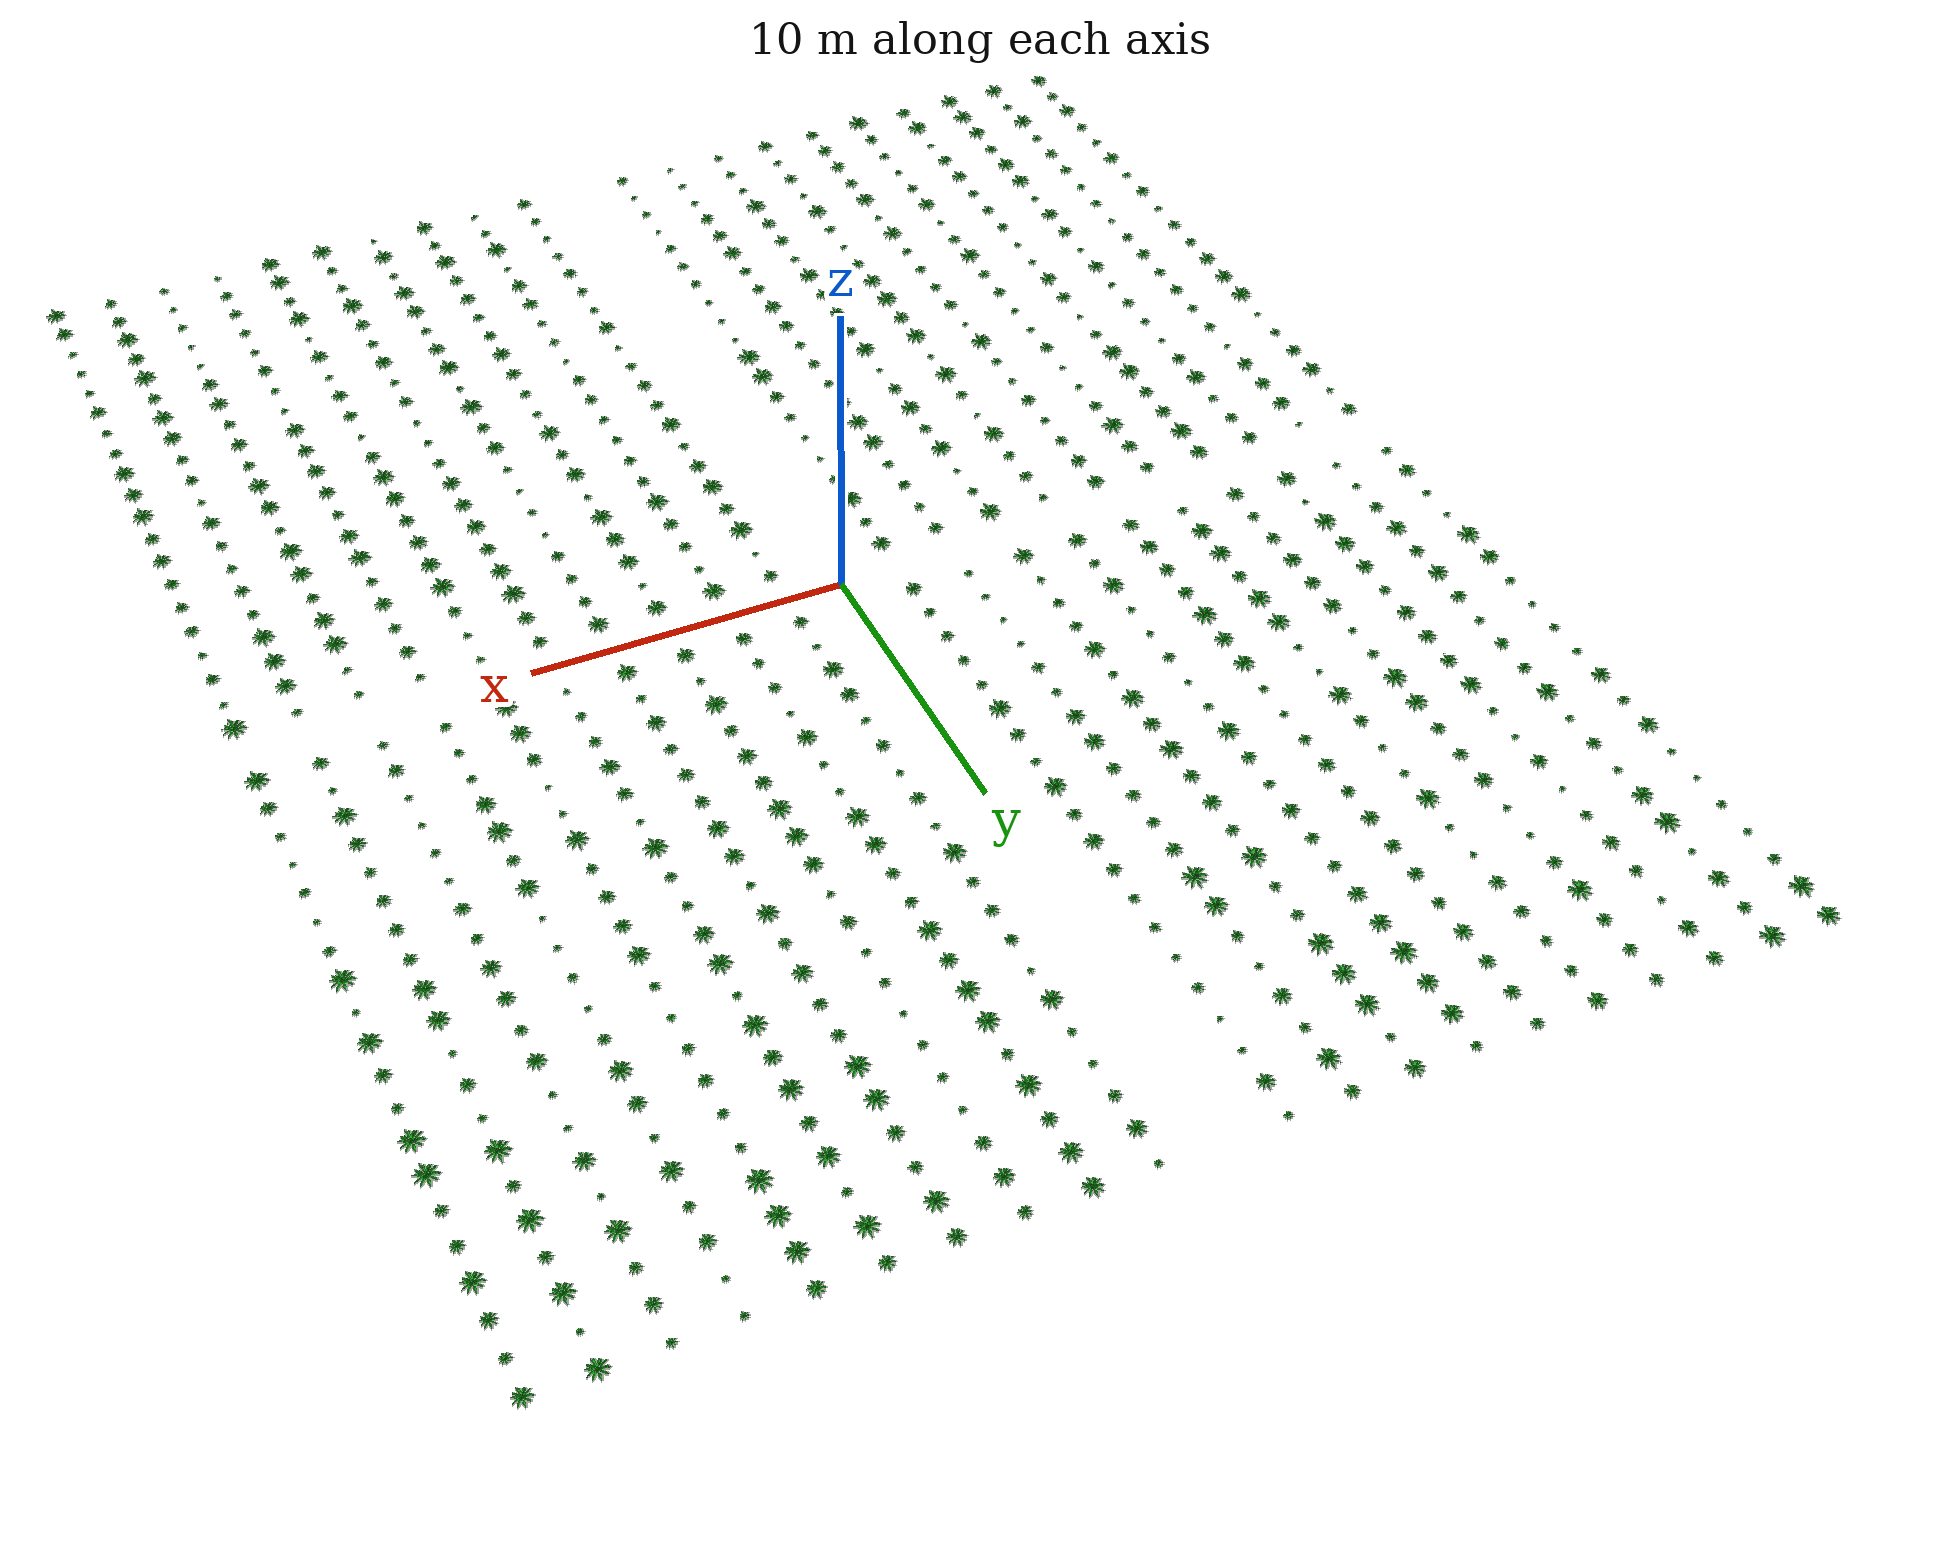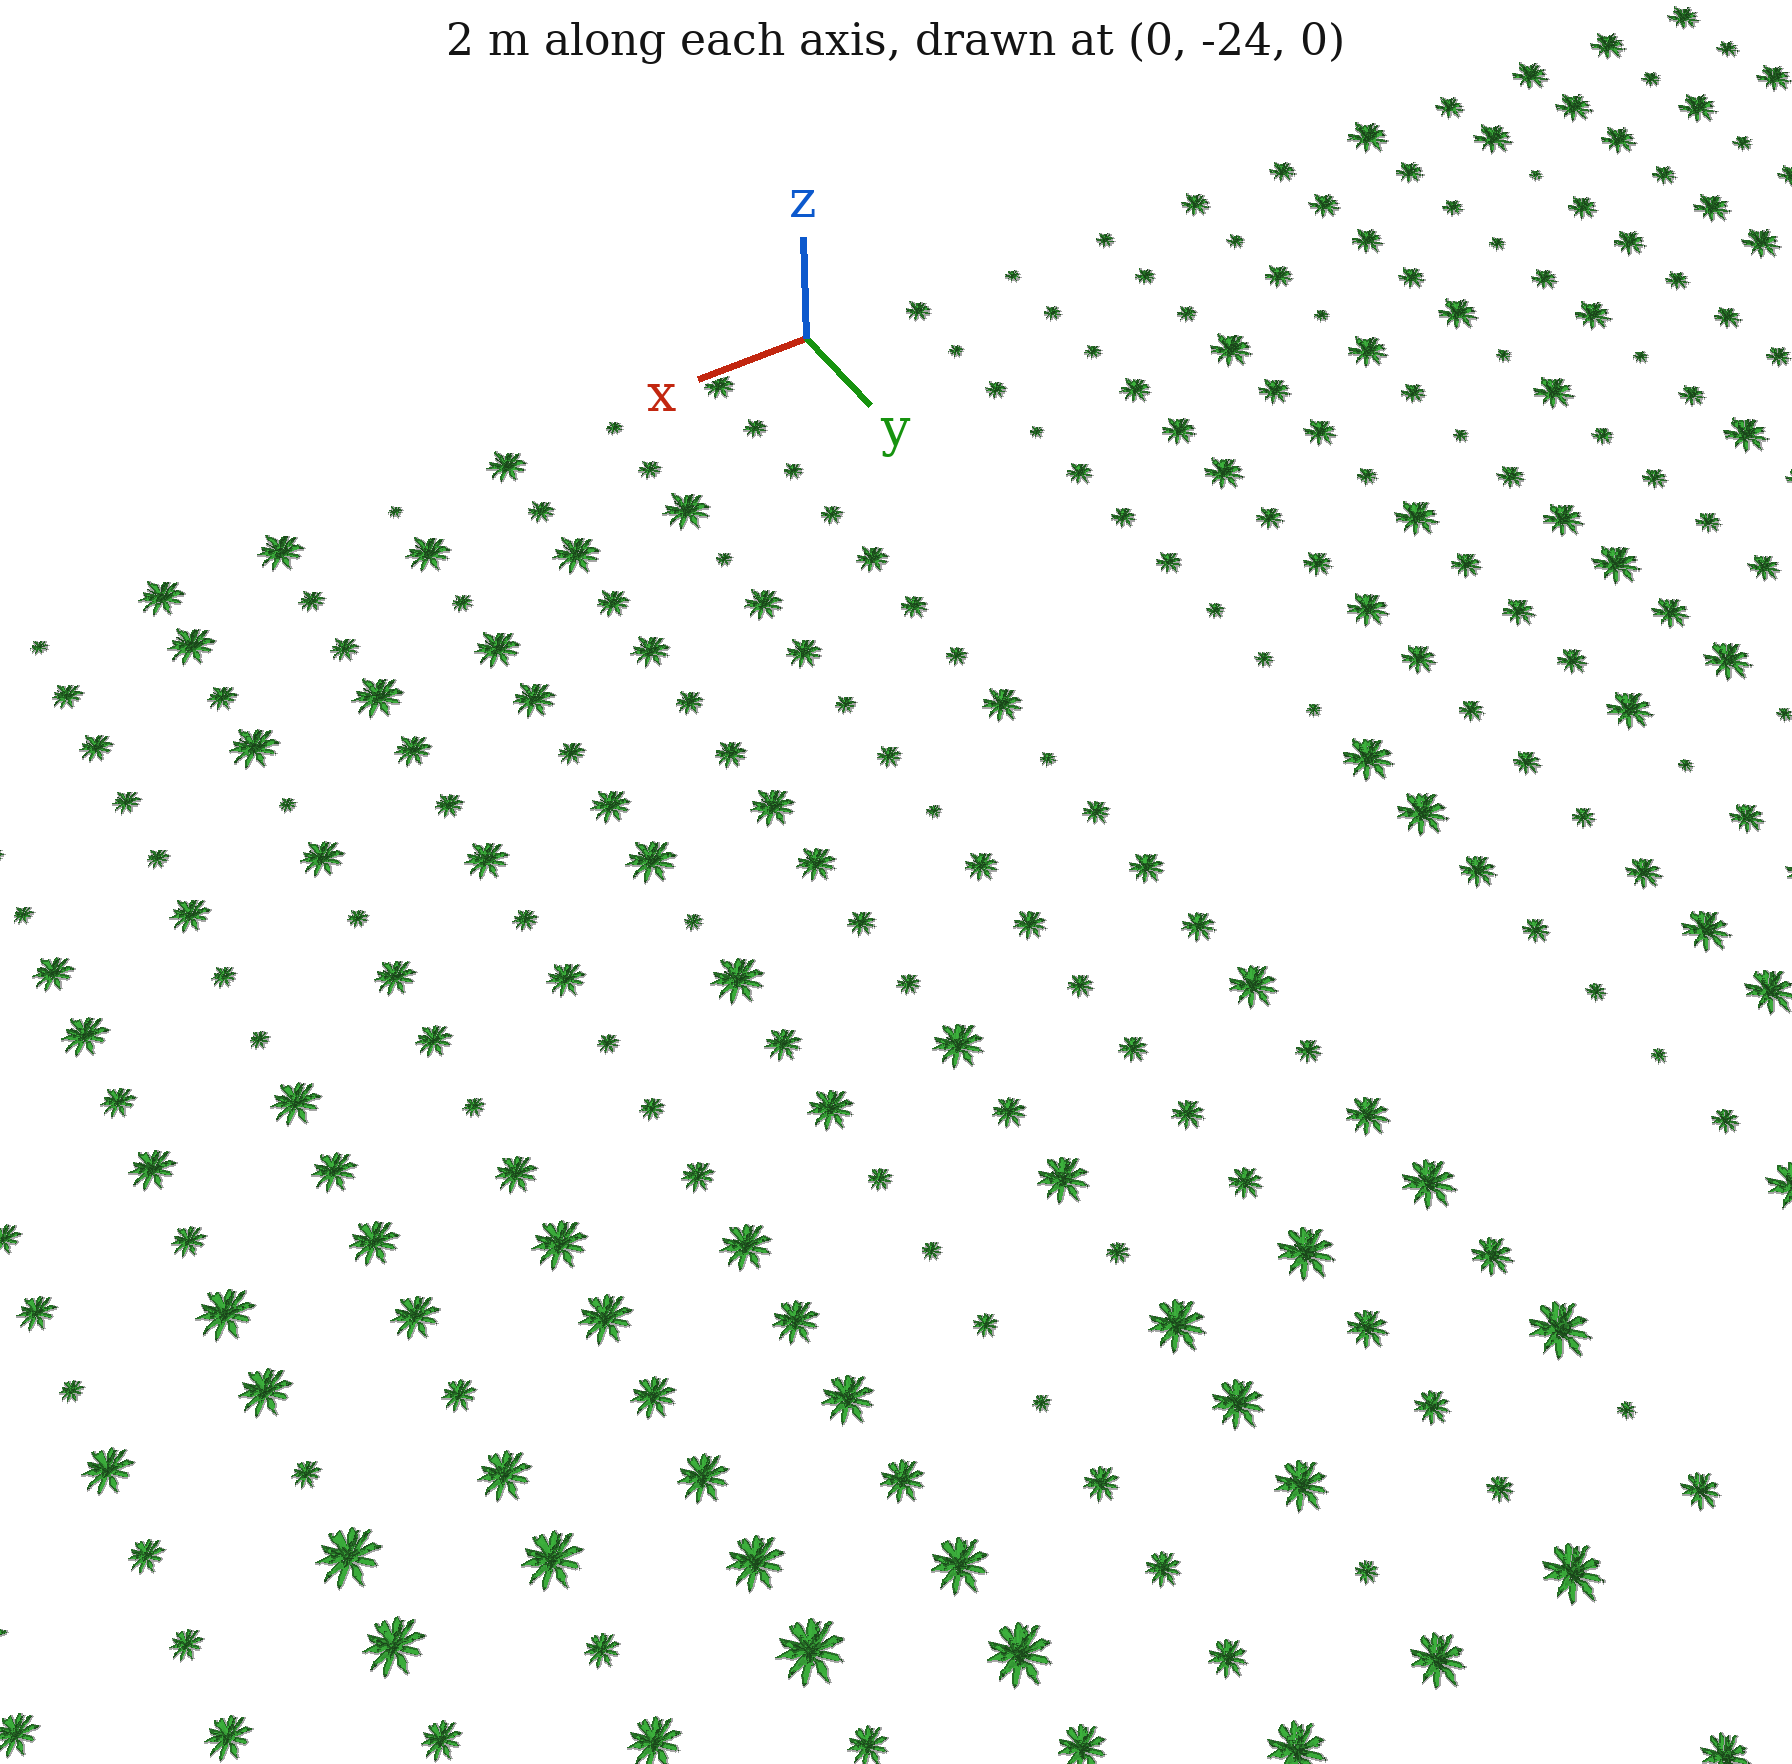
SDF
<?xml version="1.0" ?>
<sdf version="1.6">
  <model name="farm_weeds">
    <static>true</static>

    <link name="weed_top_left_0_0">
      <pose>-1.87 1.18 0 0 0 0</pose>
      <visual name="visual">
        <geometry>
          <mesh>
            <uri>model://weed/meshes/weed.dae</uri>
            <scale>0.511 0.511 0.511</scale>
          </mesh>
        </geometry>
        <material>
          <ambient>0.1 0.5 0.1 1</ambient>
          <diffuse>0.1 0.6 0.1 1</diffuse>
        </material>
      </visual>
    </link>

    <link name="weed_top_left_0_1">
      <pose>-3.74 1.18 0 0 0 0</pose>
      <visual name="visual">
        <geometry>
          <mesh>
            <uri>model://weed/meshes/weed.dae</uri>
            <scale>0.282 0.282 0.282</scale>
          </mesh>
        </geometry>
        <material>
          <ambient>0.1 0.5 0.1 1</ambient>
          <diffuse>0.1 0.6 0.1 1</diffuse>
        </material>
      </visual>
    </link>

    <link name="weed_top_left_0_2">
      <pose>-5.61 1.18 0 0 0 0</pose>
      <visual name="visual">
        <geometry>
          <mesh>
            <uri>model://weed/meshes/weed.dae</uri>
            <scale>0.594 0.594 0.594</scale>
          </mesh>
        </geometry>
        <material>
          <ambient>0.1 0.5 0.1 1</ambient>
          <diffuse>0.1 0.6 0.1 1</diffuse>
        </material>
      </visual>
    </link>

    <link name="weed_top_left_0_3">
      <pose>-7.48 1.18 0 0 0 0</pose>
      <visual name="visual">
        <geometry>
          <mesh>
            <uri>model://weed/meshes/weed.dae</uri>
            <scale>0.569 0.569 0.569</scale>
          </mesh>
        </geometry>
        <material>
          <ambient>0.1 0.5 0.1 1</ambient>
          <diffuse>0.1 0.6 0.1 1</diffuse>
        </material>
      </visual>
    </link>

    <link name="weed_top_left_0_4">
      <pose>-9.350000000000001 1.18 0 0 0 0</pose>
      <visual name="visual">
        <geometry>
          <mesh>
            <uri>model://weed/meshes/weed.dae</uri>
            <scale>0.496 0.496 0.496</scale>
          </mesh>
        </geometry>
        <material>
          <ambient>0.1 0.5 0.1 1</ambient>
          <diffuse>0.1 0.6 0.1 1</diffuse>
        </material>
      </visual>
    </link>

    <link name="weed_top_left_0_5">
      <pose>-11.22 1.18 0 0 0 0</pose>
      <visual name="visual">
        <geometry>
          <mesh>
            <uri>model://weed/meshes/weed.dae</uri>
            <scale>0.305 0.305 0.305</scale>
          </mesh>
        </geometry>
        <material>
          <ambient>0.1 0.5 0.1 1</ambient>
          <diffuse>0.1 0.6 0.1 1</diffuse>
        </material>
      </visual>
    </link>

    <link name="weed_top_left_0_6">
      <pose>-13.09 1.18 0 0 0 0</pose>
      <visual name="visual">
        <geometry>
          <mesh>
            <uri>model://weed/meshes/weed.dae</uri>
            <scale>0.534 0.534 0.534</scale>
          </mesh>
        </geometry>
        <material>
          <ambient>0.1 0.5 0.1 1</ambient>
          <diffuse>0.1 0.6 0.1 1</diffuse>
        </material>
      </visual>
    </link>

    <link name="weed_top_left_0_7">
      <pose>-14.96 1.18 0 0 0 0</pose>
      <visual name="visual">
        <geometry>
          <mesh>
            <uri>model://weed/meshes/weed.dae</uri>
            <scale>0.591 0.591 0.591</scale>
          </mesh>
        </geometry>
        <material>
          <ambient>0.1 0.5 0.1 1</ambient>
          <diffuse>0.1 0.6 0.1 1</diffuse>
        </material>
      </visual>
    </link>

    <link name="weed_top_left_0_8">
      <pose>-16.830000000000002 1.18 0 0 0 0</pose>
      <visual name="visual">
        <geometry>
          <mesh>
            <uri>model://weed/meshes/weed.dae</uri>
            <scale>0.239 0.239 0.239</scale>
          </mesh>
        </geometry>
        <material>
          <ambient>0.1 0.5 0.1 1</ambient>
          <diffuse>0.1 0.6 0.1 1</diffuse>
        </material>
      </visual>
    </link>

    <link name="weed_top_left_0_9">
      <pose>-18.700000000000003 1.18 0 0 0 0</pose>
      <visual name="visual">
        <geometry>
          <mesh>
            <uri>model://weed/meshes/weed.dae</uri>
            <scale>0.317 0.317 0.317</scale>
          </mesh>
        </geometry>
        <material>
          <ambient>0.1 0.5 0.1 1</ambient>
          <diffuse>0.1 0.6 0.1 1</diffuse>
        </material>
      </visual>
    </link>

    <link name="weed_top_left_1_0">
      <pose>-1.87 2.36 0 0 0 0</pose>
      <visual name="visual">
        <geometry>
          <mesh>
            <uri>model://weed/meshes/weed.dae</uri>
            <scale>0.367 0.367 0.367</scale>
          </mesh>
        </geometry>
        <material>
          <ambient>0.1 0.5 0.1 1</ambient>
          <diffuse>0.1 0.6 0.1 1</diffuse>
        </material>
      </visual>
    </link>

    <link name="weed_top_left_1_1">
      <pose>-3.74 2.36 0 0 0 0</pose>
      <visual name="visual">
        <geometry>
          <mesh>
            <uri>model://weed/meshes/weed.dae</uri>
            <scale>0.25 0.25 0.25</scale>
          </mesh>
        </geometry>
        <material>
          <ambient>0.1 0.5 0.1 1</ambient>
          <diffuse>0.1 0.6 0.1 1</diffuse>
        </material>
      </visual>
    </link>

    <link name="weed_top_left_1_2">
      <pose>-5.61 2.36 0 0 0 0</pose>
      <visual name="visual">
        <geometry>
          <mesh>
            <uri>model://weed/meshes/weed.dae</uri>
            <scale>0.301 0.301 0.301</scale>
          </mesh>
        </geometry>
        <material>
          <ambient>0.1 0.5 0.1 1</ambient>
          <diffuse>0.1 0.6 0.1 1</diffuse>
        </material>
      </visual>
    </link>

    <link name="weed_top_left_1_3">
      <pose>-7.48 2.36 0 0 0 0</pose>
      <visual name="visual">
        <geometry>
          <mesh>
            <uri>model://weed/meshes/weed.dae</uri>
            <scale>0.361 0.361 0.361</scale>
          </mesh>
        </geometry>
        <material>
          <ambient>0.1 0.5 0.1 1</ambient>
          <diffuse>0.1 0.6 0.1 1</diffuse>
        </material>
      </visual>
    </link>

    <link name="weed_top_left_1_4">
      <pose>-9.350000000000001 2.36 0 0 0 0</pose>
      <visual name="visual">
        <geometry>
          <mesh>
            <uri>model://weed/meshes/weed.dae</uri>
            <scale>0.559 0.559 0.559</scale>
          </mesh>
        </geometry>
        <material>
          <ambient>0.1 0.5 0.1 1</ambient>
          <diffuse>0.1 0.6 0.1 1</diffuse>
        </material>
      </visual>
    </link>

    <link name="weed_top_left_1_5">
      <pose>-11.22 2.36 0 0 0 0</pose>
      <visual name="visual">
        <geometry>
          <mesh>
            <uri>model://weed/meshes/weed.dae</uri>
            <scale>0.638 0.638 0.638</scale>
          </mesh>
        </geometry>
        <material>
          <ambient>0.1 0.5 0.1 1</ambient>
          <diffuse>0.1 0.6 0.1 1</diffuse>
        </material>
      </visual>
    </link>

    <link name="weed_top_left_1_6">
      <pose>-13.09 2.36 0 0 0 0</pose>
      <visual name="visual">
        <geometry>
          <mesh>
            <uri>model://weed/meshes/weed.dae</uri>
            <scale>0.39 0.39 0.39</scale>
          </mesh>
        </geometry>
        <material>
          <ambient>0.1 0.5 0.1 1</ambient>
          <diffuse>0.1 0.6 0.1 1</diffuse>
        </material>
      </visual>
    </link>

    <link name="weed_top_left_1_7">
      <pose>-14.96 2.36 0 0 0 0</pose>
      <visual name="visual">
        <geometry>
          <mesh>
            <uri>model://weed/meshes/weed.dae</uri>
            <scale>0.204 0.204 0.204</scale>
          </mesh>
        </geometry>
        <material>
          <ambient>0.1 0.5 0.1 1</ambient>
          <diffuse>0.1 0.6 0.1 1</diffuse>
        </material>
      </visual>
    </link>

    <link name="weed_top_left_1_8">
      <pose>-16.830000000000002 2.36 0 0 0 0</pose>
      <visual name="visual">
        <geometry>
          <mesh>
            <uri>model://weed/meshes/weed.dae</uri>
            <scale>0.285 0.285 0.285</scale>
          </mesh>
        </geometry>
        <material>
          <ambient>0.1 0.5 0.1 1</ambient>
          <diffuse>0.1 0.6 0.1 1</diffuse>
        </material>
      </visual>
    </link>

    <link name="weed_top_left_1_9">
      <pose>-18.700000000000003 2.36 0 0 0 0</pose>
      <visual name="visual">
        <geometry>
          <mesh>
            <uri>model://weed/meshes/weed.dae</uri>
            <scale>0.517 0.517 0.517</scale>
          </mesh>
        </geometry>
        <material>
          <ambient>0.1 0.5 0.1 1</ambient>
          <diffuse>0.1 0.6 0.1 1</diffuse>
        </material>
      </visual>
    </link>

    <link name="weed_top_left_2_0">
      <pose>-1.87 3.54 0 0 0 0</pose>
      <visual name="visual">
        <geometry>
          <mesh>
            <uri>model://weed/meshes/weed.dae</uri>
            <scale>0.414 0.414 0.414</scale>
          </mesh>
        </geometry>
        <material>
          <ambient>0.1 0.5 0.1 1</ambient>
          <diffuse>0.1 0.6 0.1 1</diffuse>
        </material>
      </visual>
    </link>

    <link name="weed_top_left_2_1">
      <pose>-3.74 3.54 0 0 0 0</pose>
      <visual name="visual">
        <geometry>
          <mesh>
            <uri>model://weed/meshes/weed.dae</uri>
            <scale>0.235 0.235 0.235</scale>
          </mesh>
        </geometry>
        <material>
          <ambient>0.1 0.5 0.1 1</ambient>
          <diffuse>0.1 0.6 0.1 1</diffuse>
        </material>
      </visual>
    </link>

    <link name="weed_top_left_2_2">
      <pose>-5.61 3.54 0 0 0 0</pose>
      <visual name="visual">
        <geometry>
          <mesh>
            <uri>model://weed/meshes/weed.dae</uri>
            <scale>0.37 0.37 0.37</scale>
          </mesh>
        </geometry>
        <material>
          <ambient>0.1 0.5 0.1 1</ambient>
          <diffuse>0.1 0.6 0.1 1</diffuse>
        </material>
      </visual>
    </link>

    <link name="weed_top_left_2_3">
      <pose>-7.48 3.54 0 0 0 0</pose>
      <visual name="visual">
        <geometry>
          <mesh>
            <uri>model://weed/meshes/weed.dae</uri>
            <scale>0.624 0.624 0.624</scale>
          </mesh>
        </geometry>
        <material>
          <ambient>0.1 0.5 0.1 1</ambient>
          <diffuse>0.1 0.6 0.1 1</diffuse>
        </material>
      </visual>
    </link>

    <link name="weed_top_left_2_4">
      <pose>-9.350000000000001 3.54 0 0 0 0</pose>
      <visual name="visual">
        <geometry>
          <mesh>
            <uri>model://weed/meshes/weed.dae</uri>
            <scale>0.483 0.483 0.483</scale>
          </mesh>
        </geometry>
        <material>
          <ambient>0.1 0.5 0.1 1</ambient>
          <diffuse>0.1 0.6 0.1 1</diffuse>
        </material>
      </visual>
    </link>

    <link name="weed_top_left_2_5">
      <pose>-11.22 3.54 0 0 0 0</pose>
      <visual name="visual">
        <geometry>
          <mesh>
            <uri>model://weed/meshes/weed.dae</uri>
            <scale>0.629 0.629 0.629</scale>
          </mesh>
        </geometry>
        <material>
          <ambient>0.1 0.5 0.1 1</ambient>
          <diffuse>0.1 0.6 0.1 1</diffuse>
        </material>
      </visual>
    </link>

    <link name="weed_top_left_2_6">
      <pose>-13.09 3.54 0 0 0 0</pose>
      <visual name="visual">
        <geometry>
          <mesh>
            <uri>model://weed/meshes/weed.dae</uri>
            <scale>0.454 0.454 0.454</scale>
          </mesh>
        </geometry>
        <material>
          <ambient>0.1 0.5 0.1 1</ambient>
          <diffuse>0.1 0.6 0.1 1</diffuse>
        </material>
      </visual>
    </link>

    <link name="weed_top_left_2_7">
      <pose>-14.96 3.54 0 0 0 0</pose>
      <visual name="visual">
        <geometry>
          <mesh>
            <uri>model://weed/meshes/weed.dae</uri>
            <scale>0.682 0.682 0.682</scale>
          </mesh>
        </geometry>
        <material>
          <ambient>0.1 0.5 0.1 1</ambient>
          <diffuse>0.1 0.6 0.1 1</diffuse>
        </material>
      </visual>
    </link>

    <link name="weed_top_left_2_8">
      <pose>-16.830000000000002 3.54 0 0 0 0</pose>
      <visual name="visual">
        <geometry>
          <mesh>
            <uri>model://weed/meshes/weed.dae</uri>
            <scale>0.447 0.447 0.447</scale>
          </mesh>
        </geometry>
        <material>
          <ambient>0.1 0.5 0.1 1</ambient>
          <diffuse>0.1 0.6 0.1 1</diffuse>
        </material>
      </visual>
    </link>

    <link name="weed_top_left_2_9">
      <pose>-18.700000000000003 3.54 0 0 0 0</pose>
      <visual name="visual">
        <geometry>
          <mesh>
            <uri>model://weed/meshes/weed.dae</uri>
            <scale>0.27 0.27 0.27</scale>
          </mesh>
        </geometry>
        <material>
          <ambient>0.1 0.5 0.1 1</ambient>
          <diffuse>0.1 0.6 0.1 1</diffuse>
        </material>
      </visual>
    </link>

    <link name="weed_top_left_3_0">
      <pose>-1.87 4.72 0 0 0 0</pose>
      <visual name="visual">
        <geometry>
          <mesh>
            <uri>model://weed/meshes/weed.dae</uri>
            <scale>0.352 0.352 0.352</scale>
          </mesh>
        </geometry>
        <material>
          <ambient>0.1 0.5 0.1 1</ambient>
          <diffuse>0.1 0.6 0.1 1</diffuse>
        </material>
      </visual>
    </link>

    <link name="weed_top_left_3_1">
      <pose>-3.74 4.72 0 0 0 0</pose>
      <visual name="visual">
        <geometry>
          <mesh>
            <uri>model://weed/meshes/weed.dae</uri>
            <scale>0.22 0.22 0.22</scale>
          </mesh>
        </geometry>
        <material>
          <ambient>0.1 0.5 0.1 1</ambient>
          <diffuse>0.1 0.6 0.1 1</diffuse>
        </material>
      </visual>
    </link>

    <link name="weed_top_left_3_2">
      <pose>-5.61 4.72 0 0 0 0</pose>
      <visual name="visual">
        <geometry>
          <mesh>
            <uri>model://weed/meshes/weed.dae</uri>
            <scale>0.38 0.38 0.38</scale>
          </mesh>
        </geometry>
        <material>
          <ambient>0.1 0.5 0.1 1</ambient>
          <diffuse>0.1 0.6 0.1 1</diffuse>
        </material>
      </visual>
    </link>

    <link name="weed_top_left_3_3">
      <pose>-7.48 4.72 0 0 0 0</pose>
      <visual name="visual">
        <geometry>
          <mesh>
            <uri>model://weed/meshes/weed.dae</uri>
            <scale>0.28 0.28 0.28</scale>
          </mesh>
        </geometry>
        <material>
          <ambient>0.1 0.5 0.1 1</ambient>
          <diffuse>0.1 0.6 0.1 1</diffuse>
        </material>
      </visual>
    </link>

    <link name="weed_top_left_3_4">
      <pose>-9.350000000000001 4.72 0 0 0 0</pose>
      <visual name="visual">
        <geometry>
          <mesh>
            <uri>model://weed/meshes/weed.dae</uri>
            <scale>0.496 0.496 0.496</scale>
          </mesh>
        </geometry>
        <material>
          <ambient>0.1 0.5 0.1 1</ambient>
          <diffuse>0.1 0.6 0.1 1</diffuse>
        </material>
      </visual>
    </link>

    <link name="weed_top_left_3_5">
      <pose>-11.22 4.72 0 0 0 0</pose>
      <visual name="visual">
        <geometry>
          <mesh>
            <uri>model://weed/meshes/weed.dae</uri>
            <scale>0.457 0.457 0.457</scale>
          </mesh>
        </geometry>
        <material>
          <ambient>0.1 0.5 0.1 1</ambient>
          <diffuse>0.1 0.6 0.1 1</diffuse>
        </material>
      </visual>
    </link>

    <link name="weed_top_left_3_6">
      <pose>-13.09 4.72 0 0 0 0</pose>
      <visual name="visual">
        <geometry>
          <mesh>
            <uri>model://weed/meshes/weed.dae</uri>
            <scale>0.573 0.573 0.573</scale>
          </mesh>
        </geometry>
        <material>
          <ambient>0.1 0.5 0.1 1</ambient>
          <diffuse>0.1 0.6 0.1 1</diffuse>
        </material>
      </visual>
    </link>

    <link name="weed_top_left_3_7">
      <pose>-14.96 4.72 0 0 0 0</pose>
      <visual name="visual">
        <geometry>
          <mesh>
            <uri>model://weed/meshes/weed.dae</uri>
            <scale>0.625 0.625 0.625</scale>
          </mesh>
        </geometry>
        <material>
          <ambient>0.1 0.5 0.1 1</ambient>
          <diffuse>0.1 0.6 0.1 1</diffuse>
        </material>
      </visual>
    </link>

    <link name="weed_top_left_3_8">
      <pose>-16.830000000000002 4.72 0 0 0 0</pose>
      <visual name="visual">
        <geometry>
          <mesh>
            <uri>model://weed/meshes/weed.dae</uri>
            <scale>0.603 0.603 0.603</scale>
          </mesh>
        </geometry>
        <material>
          <ambient>0.1 0.5 0.1 1</ambient>
          <diffuse>0.1 0.6 0.1 1</diffuse>
        </material>
      </visual>
    </link>

    <link name="weed_top_left_3_9">
      <pose>-18.700000000000003 4.72 0 0 0 0</pose>
      <visual name="visual">
        <geometry>
          <mesh>
            <uri>model://weed/meshes/weed.dae</uri>
            <scale>0.219 0.219 0.219</scale>
          </mesh>
        </geometry>
        <material>
          <ambient>0.1 0.5 0.1 1</ambient>
          <diffuse>0.1 0.6 0.1 1</diffuse>
        </material>
      </visual>
    </link>

    <link name="weed_top_left_4_0">
      <pose>-1.87 5.8999999999999995 0 0 0 0</pose>
      <visual name="visual">
        <geometry>
          <mesh>
            <uri>model://weed/meshes/weed.dae</uri>
            <scale>0.344 0.344 0.344</scale>
          </mesh>
        </geometry>
        <material>
          <ambient>0.1 0.5 0.1 1</ambient>
          <diffuse>0.1 0.6 0.1 1</diffuse>
        </material>
      </visual>
    </link>

    <link name="weed_top_left_4_1">
      <pose>-3.74 5.8999999999999995 0 0 0 0</pose>
      <visual name="visual">
        <geometry>
          <mesh>
            <uri>model://weed/meshes/weed.dae</uri>
            <scale>0.386 0.386 0.386</scale>
          </mesh>
        </geometry>
        <material>
          <ambient>0.1 0.5 0.1 1</ambient>
          <diffuse>0.1 0.6 0.1 1</diffuse>
        </material>
      </visual>
    </link>

    <link name="weed_top_left_4_2">
      <pose>-5.61 5.8999999999999995 0 0 0 0</pose>
      <visual name="visual">
        <geometry>
          <mesh>
            <uri>model://weed/meshes/weed.dae</uri>
            <scale>0.605 0.605 0.605</scale>
          </mesh>
        </geometry>
        <material>
          <ambient>0.1 0.5 0.1 1</ambient>
          <diffuse>0.1 0.6 0.1 1</diffuse>
        </material>
      </visual>
    </link>

    <link name="weed_top_left_4_3">
      <pose>-7.48 5.8999999999999995 0 0 0 0</pose>
      <visual name="visual">
        <geometry>
          <mesh>
            <uri>model://weed/meshes/weed.dae</uri>
            <scale>0.24 0.24 0.24</scale>
          </mesh>
        </geometry>
        <material>
          <ambient>0.1 0.5 0.1 1</ambient>
          <diffuse>0.1 0.6 0.1 1</diffuse>
        </material>
      </visual>
    </link>

    <link name="weed_top_left_4_4">
      <pose>-9.350000000000001 5.8999999999999995 0 0 0 0</pose>
      <visual name="visual">
        <geometry>
          <mesh>
            <uri>model://weed/meshes/weed.dae</uri>
            <scale>0.693 0.693 0.693</scale>
          </mesh>
        </geometry>
        <material>
          <ambient>0.1 0.5 0.1 1</ambient>
          <diffuse>0.1 0.6 0.1 1</diffuse>
        </material>
      </visual>
    </link>

    <link name="weed_top_left_4_5">
      <pose>-11.22 5.8999999999999995 0 0 0 0</pose>
      <visual name="visual">
        <geometry>
          <mesh>
            <uri>model://weed/meshes/weed.dae</uri>
            <scale>0.696 0.696 0.696</scale>
          </mesh>
        </geometry>
        <material>
          <ambient>0.1 0.5 0.1 1</ambient>
          <diffuse>0.1 0.6 0.1 1</diffuse>
        </material>
      </visual>
    </link>

    <link name="weed_top_left_4_6">
      <pose>-13.09 5.8999999999999995 0 0 0 0</pose>
      <visual name="visual">
        <geometry>
          <mesh>
            <uri>model://weed/meshes/weed.dae</uri>
            <scale>0.516 0.516 0.516</scale>
          </mesh>
        </geometry>
        <material>
          <ambient>0.1 0.5 0.1 1</ambient>
          <diffuse>0.1 0.6 0.1 1</diffuse>
        </material>
      </visual>
    </link>

    <link name="weed_top_left_4_7">
      <pose>-14.96 5.8999999999999995 0 0 0 0</pose>
      <visual name="visual">
        <geometry>
          <mesh>
            <uri>model://weed/meshes/weed.dae</uri>
            <scale>0.543 0.543 0.543</scale>
          </mesh>
        </geometry>
        <material>
          <ambient>0.1 0.5 0.1 1</ambient>
          <diffuse>0.1 0.6 0.1 1</diffuse>
        </material>
      </visual>
    </link>

    <link name="weed_top_left_4_8">
      <pose>-16.830000000000002 5.8999999999999995 0 0 0 0</pose>
      <visual name="visual">
        <geometry>
          <mesh>
            <uri>model://weed/meshes/weed.dae</uri>
            <scale>0.475 0.475 0.475</scale>
          </mesh>
        </geometry>
        <material>
          <ambient>0.1 0.5 0.1 1</ambient>
          <diffuse>0.1 0.6 0.1 1</diffuse>
        </material>
      </visual>
    </link>

    <link name="weed_top_left_4_9">
      <pose>-18.700000000000003 5.8999999999999995 0 0 0 0</pose>
      <visual name="visual">
        <geometry>
          <mesh>
            <uri>model://weed/meshes/weed.dae</uri>
            <scale>0.675 0.675 0.675</scale>
          </mesh>
        </geometry>
        <material>
          <ambient>0.1 0.5 0.1 1</ambient>
          <diffuse>0.1 0.6 0.1 1</diffuse>
        </material>
      </visual>
    </link>

    <link name="weed_top_left_5_0">
      <pose>-1.87 7.08 0 0 0 0</pose>
      <visual name="visual">
        <geometry>
          <mesh>
            <uri>model://weed/meshes/weed.dae</uri>
            <scale>0.659 0.659 0.659</scale>
          </mesh>
        </geometry>
        <material>
          <ambient>0.1 0.5 0.1 1</ambient>
          <diffuse>0.1 0.6 0.1 1</diffuse>
        </material>
      </visual>
    </link>

    <link name="weed_top_left_5_1">
      <pose>-3.74 7.08 0 0 0 0</pose>
      <visual name="visual">
        <geometry>
          <mesh>
            <uri>model://weed/meshes/weed.dae</uri>
            <scale>0.313 0.313 0.313</scale>
          </mesh>
        </geometry>
        <material>
          <ambient>0.1 0.5 0.1 1</ambient>
          <diffuse>0.1 0.6 0.1 1</diffuse>
        </material>
      </visual>
    </link>

    <link name="weed_top_left_5_2">
      <pose>-5.61 7.08 0 0 0 0</pose>
      <visual name="visual">
        <geometry>
          <mesh>
            <uri>model://weed/meshes/weed.dae</uri>
            <scale>0.31 0.31 0.31</scale>
          </mesh>
        </geometry>
        <material>
          <ambient>0.1 0.5 0.1 1</ambient>
          <diffuse>0.1 0.6 0.1 1</diffuse>
        </material>
      </visual>
    </link>

    <link name="weed_top_left_5_3">
      <pose>-7.48 7.08 0 0 0 0</pose>
      <visual name="visual">
        <geometry>
          <mesh>
            <uri>model://weed/meshes/weed.dae</uri>
            <scale>0.378 0.378 0.378</scale>
          </mesh>
        </geometry>
        <material>
          <ambient>0.1 0.5 0.1 1</ambient>
          <diffuse>0.1 0.6 0.1 1</diffuse>
        </material>
      </visual>
    </link>

    <link name="weed_top_left_5_4">
      <pose>-9.350000000000001 7.08 0 0 0 0</pose>
      <visual name="visual">
        <geometry>
          <mesh>
            <uri>model://weed/meshes/weed.dae</uri>
            <scale>0.578 0.578 0.578</scale>
          </mesh>
        </geometry>
        <material>
          <ambient>0.1 0.5 0.1 1</ambient>
          <diffuse>0.1 0.6 0.1 1</diffuse>
        </material>
      </visual>
    </link>

    <link name="weed_top_left_5_5">
      <pose>-11.22 7.08 0 0 0 0</pose>
      <visual name="visual">
        <geometry>
          <mesh>
            <uri>model://weed/meshes/weed.dae</uri>
            <scale>0.646 0.646 0.646</scale>
          </mesh>
        </geometry>
        <material>
          <ambient>0.1 0.5 0.1 1</ambient>
          <diffuse>0.1 0.6 0.1 1</diffuse>
        </material>
      </visual>
    </link>

    <link name="weed_top_left_5_6">
      <pose>-13.09 7.08 0 0 0 0</pose>
      <visual name="visual">
        <geometry>
          <mesh>
            <uri>model://weed/meshes/weed.dae</uri>
            <scale>0.554 0.554 0.554</scale>
          </mesh>
        </geometry>
        <material>
          <ambient>0.1 0.5 0.1 1</ambient>
          <diffuse>0.1 0.6 0.1 1</diffuse>
        </material>
      </visual>
    </link>

    <link name="weed_top_left_5_7">
      <pose>-14.96 7.08 0 0 0 0</pose>
      <visual name="visual">
        <geometry>
          <mesh>
            <uri>model://weed/meshes/weed.dae</uri>
            <scale>0.365 0.365 0.365</scale>
          </mesh>
        </geometry>
        <material>
          <ambient>0.1 0.5 0.1 1</ambient>
          <diffuse>0.1 0.6 0.1 1</diffuse>
        </material>
      </visual>
    </link>

    <link name="weed_top_left_5_8">
      <pose>-16.830000000000002 7.08 0 0 0 0</pose>
      <visual name="visual">
        <geometry>
          <mesh>
            <uri>model://weed/meshes/weed.dae</uri>
            <scale>0.629 0.629 0.629</scale>
          </mesh>
        </geometry>
        <material>
          <ambient>0.1 0.5 0.1 1</ambient>
          <diffuse>0.1 0.6 0.1 1</diffuse>
        </material>
      </visual>
    </link>

    <link name="weed_top_left_5_9">
      <pose>-18.700000000000003 7.08 0 0 0 0</pose>
      <visual name="visual">
        <geometry>
          <mesh>
            <uri>model://weed/meshes/weed.dae</uri>
            <scale>0.574 0.574 0.574</scale>
          </mesh>
        </geometry>
        <material>
          <ambient>0.1 0.5 0.1 1</ambient>
          <diffuse>0.1 0.6 0.1 1</diffuse>
        </material>
      </visual>
    </link>

    <link name="weed_top_left_6_0">
      <pose>-1.87 8.26 0 0 0 0</pose>
      <visual name="visual">
        <geometry>
          <mesh>
            <uri>model://weed/meshes/weed.dae</uri>
            <scale>0.477 0.477 0.477</scale>
          </mesh>
        </geometry>
        <material>
          <ambient>0.1 0.5 0.1 1</ambient>
          <diffuse>0.1 0.6 0.1 1</diffuse>
        </material>
      </visual>
    </link>

    <link name="weed_top_left_6_1">
      <pose>-3.74 8.26 0 0 0 0</pose>
      <visual name="visual">
        <geometry>
          <mesh>
            <uri>model://weed/meshes/weed.dae</uri>
            <scale>0.554 0.554 0.554</scale>
          </mesh>
        </geometry>
        <material>
          <ambient>0.1 0.5 0.1 1</ambient>
          <diffuse>0.1 0.6 0.1 1</diffuse>
        </material>
      </visual>
    </link>

    <link name="weed_top_left_6_2">
      <pose>-5.61 8.26 0 0 0 0</pose>
      <visual name="visual">
        <geometry>
          <mesh>
            <uri>model://weed/meshes/weed.dae</uri>
            <scale>0.639 0.639 0.639</scale>
          </mesh>
        </geometry>
        <material>
          <ambient>0.1 0.5 0.1 1</ambient>
          <diffuse>0.1 0.6 0.1 1</diffuse>
        </material>
      </visual>
    </link>

    <link name="weed_top_left_6_3">
      <pose>-7.48 8.26 0 0 0 0</pose>
      <visual name="visual">
        <geometry>
          <mesh>
            <uri>model://weed/meshes/weed.dae</uri>
            <scale>0.232 0.232 0.232</scale>
          </mesh>
        </geometry>
        <material>
          <ambient>0.1 0.5 0.1 1</ambient>
          <diffuse>0.1 0.6 0.1 1</diffuse>
        </material>
      </visual>
    </link>

    <link name="weed_top_left_6_4">
      <pose>-9.350000000000001 8.26 0 0 0 0</pose>
      <visual name="visual">
        <geometry>
          <mesh>
            <uri>model://weed/meshes/weed.dae</uri>
            <scale>0.613 0.613 0.613</scale>
          </mesh>
        </geometry>
        <material>
          <ambient>0.1 0.5 0.1 1</ambient>
          <diffuse>0.1 0.6 0.1 1</diffuse>
        </material>
      </visual>
    </link>

    <link name="weed_top_left_6_5">
      <pose>-11.22 8.26 0 0 0 0</pose>
      <visual name="visual">
        <geometry>
          <mesh>
            <uri>model://weed/meshes/weed.dae</uri>
            <scale>0.273 0.273 0.273</scale>
          </mesh>
        </geometry>
        <material>
          <ambient>0.1 0.5 0.1 1</ambient>
          <diffuse>0.1 0.6 0.1 1</diffuse>
        </material>
      </visual>
    </link>

    <link name="weed_top_left_6_6">
      <pose>-13.09 8.26 0 0 0 0</pose>
      <visual name="visual">
        <geometry>
          <mesh>
            <uri>model://weed/meshes/weed.dae</uri>
            <scale>0.27 0.27 0.27</scale>
          </mesh>
        </geometry>
        <material>
          <ambient>0.1 0.5 0.1 1</ambient>
          <diffuse>0.1 0.6 0.1 1</diffuse>
        </material>
      </visual>
    </link>

    <link name="weed_top_left_6_7">
      <pose>-14.96 8.26 0 0 0 0</pose>
      <visual name="visual">
        <geometry>
          <mesh>
            <uri>model://weed/meshes/weed.dae</uri>
            <scale>0.577 0.577 0.577</scale>
          </mesh>
        </geometry>
        <material>
          <ambient>0.1 0.5 0.1 1</ambient>
          <diffuse>0.1 0.6 0.1 1</diffuse>
        </material>
      </visual>
    </link>

    <link name="weed_top_left_6_8">
      <pose>-16.830000000000002 8.26 0 0 0 0</pose>
      <visual name="visual">
        <geometry>
          <mesh>
            <uri>model://weed/meshes/weed.dae</uri>
            <scale>0.479 0.479 0.479</scale>
          </mesh>
        </geometry>
        <material>
          <ambient>0.1 0.5 0.1 1</ambient>
          <diffuse>0.1 0.6 0.1 1</diffuse>
        </material>
      </visual>
    </link>

    <link name="weed_top_left_6_9">
      <pose>-18.700000000000003 8.26 0 0 0 0</pose>
      <visual name="visual">
        <geometry>
          <mesh>
            <uri>model://weed/meshes/weed.dae</uri>
            <scale>0.333 0.333 0.333</scale>
          </mesh>
        </geometry>
        <material>
          <ambient>0.1 0.5 0.1 1</ambient>
          <diffuse>0.1 0.6 0.1 1</diffuse>
        </material>
      </visual>
    </link>

    <link name="weed_top_left_7_0">
      <pose>-1.87 9.44 0 0 0 0</pose>
      <visual name="visual">
        <geometry>
          <mesh>
            <uri>model://weed/meshes/weed.dae</uri>
            <scale>0.304 0.304 0.304</scale>
          </mesh>
        </geometry>
        <material>
          <ambient>0.1 0.5 0.1 1</ambient>
          <diffuse>0.1 0.6 0.1 1</diffuse>
        </material>
      </visual>
    </link>

    <link name="weed_top_left_7_1">
      <pose>-3.74 9.44 0 0 0 0</pose>
      <visual name="visual">
        <geometry>
          <mesh>
            <uri>model://weed/meshes/weed.dae</uri>
            <scale>0.595 0.595 0.595</scale>
          </mesh>
        </geometry>
        <material>
          <ambient>0.1 0.5 0.1 1</ambient>
          <diffuse>0.1 0.6 0.1 1</diffuse>
        </material>
      </visual>
    </link>

    <link name="weed_top_left_7_2">
      <pose>-5.61 9.44 0 0 0 0</pose>
      <visual name="visual">
        <geometry>
          <mesh>
            <uri>model://weed/meshes/weed.dae</uri>
            <scale>0.505 0.505 0.505</scale>
          </mesh>
        </geometry>
        <material>
          <ambient>0.1 0.5 0.1 1</ambient>
          <diffuse>0.1 0.6 0.1 1</diffuse>
        </material>
      </visual>
    </link>

    <link name="weed_top_left_7_3">
      <pose>-7.48 9.44 0 0 0 0</pose>
      <visual name="visual">
        <geometry>
          <mesh>
            <uri>model://weed/meshes/weed.dae</uri>
            <scale>0.305 0.305 0.305</scale>
          </mesh>
        </geometry>
        <material>
          <ambient>0.1 0.5 0.1 1</ambient>
          <diffuse>0.1 0.6 0.1 1</diffuse>
        </material>
      </visual>
    </link>

    <link name="weed_top_left_7_4">
      <pose>-9.350000000000001 9.44 0 0 0 0</pose>
      <visual name="visual">
        <geometry>
          <mesh>
            <uri>model://weed/meshes/weed.dae</uri>
            <scale>0.303 0.303 0.303</scale>
          </mesh>
        </geometry>
        <material>
          <ambient>0.1 0.5 0.1 1</ambient>
          <diffuse>0.1 0.6 0.1 1</diffuse>
        </material>
      </visual>
    </link>

    <link name="weed_top_left_7_5">
      <pose>-11.22 9.44 0 0 0 0</pose>
      <visual name="visual">
        <geometry>
          <mesh>
            <uri>model://weed/meshes/weed.dae</uri>
            <scale>0.225 0.225 0.225</scale>
          </mesh>
        </geometry>
        <material>
          <ambient>0.1 0.5 0.1 1</ambient>
          <diffuse>0.1 0.6 0.1 1</diffuse>
        </material>
      </visual>
    </link>

    <link name="weed_top_left_7_6">
      <pose>-13.09 9.44 0 0 0 0</pose>
      <visual name="visual">
        <geometry>
          <mesh>
            <uri>model://weed/meshes/weed.dae</uri>
            <scale>0.35 0.35 0.35</scale>
          </mesh>
        </geometry>
        <material>
          <ambient>0.1 0.5 0.1 1</ambient>
          <diffuse>0.1 0.6 0.1 1</diffuse>
        </material>
      </visual>
    </link>

    <link name="weed_top_left_7_7">
      <pose>-14.96 9.44 0 0 0 0</pose>
      <visual name="visual">
        <geometry>
          <mesh>
            <uri>model://weed/meshes/weed.dae</uri>
            <scale>0.547 0.547 0.547</scale>
          </mesh>
        </geometry>
        <material>
          <ambient>0.1 0.5 0.1 1</ambient>
          <diffuse>0.1 0.6 0.1 1</diffuse>
        </material>
      </visual>
    </link>

    <link name="weed_top_left_7_8">
      <pose>-16.830000000000002 9.44 0 0 0 0</pose>
      <visual name="visual">
        <geometry>
          <mesh>
            <uri>model://weed/meshes/weed.dae</uri>
            <scale>0.329 0.329 0.329</scale>
          </mesh>
        </geometry>
        <material>
          <ambient>0.1 0.5 0.1 1</ambient>
          <diffuse>0.1 0.6 0.1 1</diffuse>
        </material>
      </visual>
    </link>

    <link name="weed_top_left_7_9">
      <pose>-18.700000000000003 9.44 0 0 0 0</pose>
      <visual name="visual">
        <geometry>
          <mesh>
            <uri>model://weed/meshes/weed.dae</uri>
            <scale>0.251 0.251 0.251</scale>
          </mesh>
        </geometry>
        <material>
          <ambient>0.1 0.5 0.1 1</ambient>
          <diffuse>0.1 0.6 0.1 1</diffuse>
        </material>
      </visual>
    </link>

    <link name="weed_top_left_8_0">
      <pose>-1.87 10.62 0 0 0 0</pose>
      <visual name="visual">
        <geometry>
          <mesh>
            <uri>model://weed/meshes/weed.dae</uri>
            <scale>0.642 0.642 0.642</scale>
          </mesh>
        </geometry>
        <material>
          <ambient>0.1 0.5 0.1 1</ambient>
          <diffuse>0.1 0.6 0.1 1</diffuse>
        </material>
      </visual>
    </link>

    <link name="weed_top_left_8_1">
      <pose>-3.74 10.62 0 0 0 0</pose>
      <visual name="visual">
        <geometry>
          <mesh>
            <uri>model://weed/meshes/weed.dae</uri>
            <scale>0.429 0.429 0.429</scale>
          </mesh>
        </geometry>
        <material>
          <ambient>0.1 0.5 0.1 1</ambient>
          <diffuse>0.1 0.6 0.1 1</diffuse>
        </material>
      </visual>
    </link>

    <link name="weed_top_left_8_2">
      <pose>-5.61 10.62 0 0 0 0</pose>
      <visual name="visual">
        <geometry>
          <mesh>
            <uri>model://weed/meshes/weed.dae</uri>
            <scale>0.643 0.643 0.643</scale>
          </mesh>
        </geometry>
        <material>
          <ambient>0.1 0.5 0.1 1</ambient>
          <diffuse>0.1 0.6 0.1 1</diffuse>
        </material>
      </visual>
    </link>

    <link name="weed_top_left_8_3">
      <pose>-7.48 10.62 0 0 0 0</pose>
      <visual name="visual">
        <geometry>
          <mesh>
            <uri>model://weed/meshes/weed.dae</uri>
            <scale>0.647 0.647 0.647</scale>
          </mesh>
        </geometry>
        <material>
          <ambient>0.1 0.5 0.1 1</ambient>
          <diffuse>0.1 0.6 0.1 1</diffuse>
        </material>
      </visual>
    </link>

    <link name="weed_top_left_8_4">
      <pose>-9.350000000000001 10.62 0 0 0 0</pose>
      <visual name="visual">
        <geometry>
          <mesh>
            <uri>model://weed/meshes/weed.dae</uri>
            <scale>0.268 0.268 0.268</scale>
          </mesh>
        </geometry>
        <material>
          <ambient>0.1 0.5 0.1 1</ambient>
          <diffuse>0.1 0.6 0.1 1</diffuse>
        </material>
      </visual>
    </link>

    <link name="weed_top_left_8_5">
      <pose>-11.22 10.62 0 0 0 0</pose>
      <visual name="visual">
        <geometry>
          <mesh>
            <uri>model://weed/meshes/weed.dae</uri>
            <scale>0.656 0.656 0.656</scale>
          </mesh>
        </geometry>
        <material>
          <ambient>0.1 0.5 0.1 1</ambient>
          <diffuse>0.1 0.6 0.1 1</diffuse>
        </material>
      </visual>
    </link>

    <link name="weed_top_left_8_6">
      <pose>-13.09 10.62 0 0 0 0</pose>
      <visual name="visual">
        <geometry>
          <mesh>
            <uri>model://weed/meshes/weed.dae</uri>
            <scale>0.688 0.688 0.688</scale>
          </mesh>
        </geometry>
        <material>
          <ambient>0.1 0.5 0.1 1</ambient>
          <diffuse>0.1 0.6 0.1 1</diffuse>
        </material>
      </visual>
    </link>

    <link name="weed_top_left_8_7">
      <pose>-14.96 10.62 0 0 0 0</pose>
      <visual name="visual">
        <geometry>
          <mesh>
            <uri>model://weed/meshes/weed.dae</uri>
            <scale>0.512 0.512 0.512</scale>
          </mesh>
        </geometry>
        <material>
          <ambient>0.1 0.5 0.1 1</ambient>
          <diffuse>0.1 0.6 0.1 1</diffuse>
        </material>
      </visual>
    </link>

    <link name="weed_top_left_8_8">
      <pose>-16.830000000000002 10.62 0 0 0 0</pose>
      <visual name="visual">
        <geometry>
          <mesh>
            <uri>model://weed/meshes/weed.dae</uri>
            <scale>0.448 0.448 0.448</scale>
          </mesh>
        </geometry>
        <material>
          <ambient>0.1 0.5 0.1 1</ambient>
          <diffuse>0.1 0.6 0.1 1</diffuse>
        </material>
      </visual>
    </link>

    <link name="weed_top_left_8_9">
      <pose>-18.700000000000003 10.62 0 0 0 0</pose>
      <visual name="visual">
        <geometry>
          <mesh>
            <uri>model://weed/meshes/weed.dae</uri>
            <scale>0.317 0.317 0.317</scale>
          </mesh>
        </geometry>
        <material>
          <ambient>0.1 0.5 0.1 1</ambient>
          <diffuse>0.1 0.6 0.1 1</diffuse>
        </material>
      </visual>
    </link>

    <link name="weed_top_left_9_0">
      <pose>-1.87 11.799999999999999 0 0 0 0</pose>
      <visual name="visual">
        <geometry>
          <mesh>
            <uri>model://weed/meshes/weed.dae</uri>
            <scale>0.416 0.416 0.416</scale>
          </mesh>
        </geometry>
        <material>
          <ambient>0.1 0.5 0.1 1</ambient>
          <diffuse>0.1 0.6 0.1 1</diffuse>
        </material>
      </visual>
    </link>

    <link name="weed_top_left_9_1">
      <pose>-3.74 11.799999999999999 0 0 0 0</pose>
      <visual name="visual">
        <geometry>
          <mesh>
            <uri>model://weed/meshes/weed.dae</uri>
            <scale>0.407 0.407 0.407</scale>
          </mesh>
        </geometry>
        <material>
          <ambient>0.1 0.5 0.1 1</ambient>
          <diffuse>0.1 0.6 0.1 1</diffuse>
        </material>
      </visual>
    </link>

    <link name="weed_top_left_9_2">
      <pose>-5.61 11.799999999999999 0 0 0 0</pose>
      <visual name="visual">
        <geometry>
          <mesh>
            <uri>model://weed/meshes/weed.dae</uri>
            <scale>0.476 0.476 0.476</scale>
          </mesh>
        </geometry>
        <material>
          <ambient>0.1 0.5 0.1 1</ambient>
          <diffuse>0.1 0.6 0.1 1</diffuse>
        </material>
      </visual>
    </link>

    <link name="weed_top_left_9_3">
      <pose>-7.48 11.799999999999999 0 0 0 0</pose>
      <visual name="visual">
        <geometry>
          <mesh>
            <uri>model://weed/meshes/weed.dae</uri>
            <scale>0.451 0.451 0.451</scale>
          </mesh>
        </geometry>
        <material>
          <ambient>0.1 0.5 0.1 1</ambient>
          <diffuse>0.1 0.6 0.1 1</diffuse>
        </material>
      </visual>
    </link>

    <link name="weed_top_left_9_4">
      <pose>-9.350000000000001 11.799999999999999 0 0 0 0</pose>
      <visual name="visual">
        <geometry>
          <mesh>
            <uri>model://weed/meshes/weed.dae</uri>
            <scale>0.379 0.379 0.379</scale>
          </mesh>
        </geometry>
        <material>
          <ambient>0.1 0.5 0.1 1</ambient>
          <diffuse>0.1 0.6 0.1 1</diffuse>
        </material>
      </visual>
    </link>

    <link name="weed_top_left_9_5">
      <pose>-11.22 11.799999999999999 0 0 0 0</pose>
      <visual name="visual">
        <geometry>
          <mesh>
            <uri>model://weed/meshes/weed.dae</uri>
            <scale>0.443 0.443 0.443</scale>
          </mesh>
        </geometry>
        <material>
          <ambient>0.1 0.5 0.1 1</ambient>
          <diffuse>0.1 0.6 0.1 1</diffuse>
        </material>
      </visual>
    </link>

    <link name="weed_top_left_9_6">
      <pose>-13.09 11.799999999999999 0 0 0 0</pose>
      <visual name="visual">
        <geometry>
          <mesh>
            <uri>model://weed/meshes/weed.dae</uri>
            <scale>0.633 0.633 0.633</scale>
          </mesh>
        </geometry>
        <material>
          <ambient>0.1 0.5 0.1 1</ambient>
          <diffuse>0.1 0.6 0.1 1</diffuse>
        </material>
      </visual>
    </link>

    <link name="weed_top_left_9_7">
      <pose>-14.96 11.799999999999999 0 0 0 0</pose>
      <visual name="visual">
        <geometry>
          <mesh>
            <uri>model://weed/meshes/weed.dae</uri>
            <scale>0.614 0.614 0.614</scale>
          </mesh>
        </geometry>
        <material>
          <ambient>0.1 0.5 0.1 1</ambient>
          <diffuse>0.1 0.6 0.1 1</diffuse>
        </material>
      </visual>
    </link>

    <link name="weed_top_left_9_8">
      <pose>-16.830000000000002 11.799999999999999 0 0 0 0</pose>
      <visual name="visual">
        <geometry>
          <mesh>
            <uri>model://weed/meshes/weed.dae</uri>
            <scale>0.423 0.423 0.423</scale>
          </mesh>
        </geometry>
        <material>
          <ambient>0.1 0.5 0.1 1</ambient>
          <diffuse>0.1 0.6 0.1 1</diffuse>
        </material>
      </visual>
    </link>

    <link name="weed_top_left_9_9">
      <pose>-18.700000000000003 11.799999999999999 0 0 0 0</pose>
      <visual name="visual">
        <geometry>
          <mesh>
            <uri>model://weed/meshes/weed.dae</uri>
            <scale>0.281 0.281 0.281</scale>
          </mesh>
        </geometry>
        <material>
          <ambient>0.1 0.5 0.1 1</ambient>
          <diffuse>0.1 0.6 0.1 1</diffuse>
        </material>
      </visual>
    </link>

    <link name="weed_top_left_10_0">
      <pose>-1.87 12.979999999999999 0 0 0 0</pose>
      <visual name="visual">
        <geometry>
          <mesh>
            <uri>model://weed/meshes/weed.dae</uri>
            <scale>0.551 0.551 0.551</scale>
          </mesh>
        </geometry>
        <material>
          <ambient>0.1 0.5 0.1 1</ambient>
          <diffuse>0.1 0.6 0.1 1</diffuse>
        </material>
      </visual>
    </link>

    <link name="weed_top_left_10_1">
      <pose>-3.74 12.979999999999999 0 0 0 0</pose>
      <visual name="visual">
        <geometry>
          <mesh>
            <uri>model://weed/meshes/weed.dae</uri>
            <scale>0.378 0.378 0.378</scale>
          </mesh>
        </geometry>
        <material>
          <ambient>0.1 0.5 0.1 1</ambient>
          <diffuse>0.1 0.6 0.1 1</diffuse>
        </material>
      </visual>
    </link>

    <link name="weed_top_left_10_2">
      <pose>-5.61 12.979999999999999 0 0 0 0</pose>
      <visual name="visual">
        <geometry>
          <mesh>
            <uri>model://weed/meshes/weed.dae</uri>
            <scale>0.549 0.549 0.549</scale>
          </mesh>
        </geometry>
        <material>
          <ambient>0.1 0.5 0.1 1</ambient>
          <diffuse>0.1 0.6 0.1 1</diffuse>
        </material>
      </visual>
    </link>

    <link name="weed_top_left_10_3">
      <pose>-7.48 12.979999999999999 0 0 0 0</pose>
      <visual name="visual">
        <geometry>
          <mesh>
            <uri>model://weed/meshes/weed.dae</uri>
            <scale>0.345 0.345 0.345</scale>
          </mesh>
        </geometry>
        <material>
          <ambient>0.1 0.5 0.1 1</ambient>
          <diffuse>0.1 0.6 0.1 1</diffuse>
        </material>
      </visual>
    </link>

    <link name="weed_top_left_10_4">
      <pose>-9.350000000000001 12.979999999999999 0 0 0 0</pose>
      <visual name="visual">
        <geometry>
          <mesh>
            <uri>model://weed/meshes/weed.dae</uri>
            <scale>0.49 0.49 0.49</scale>
          </mesh>
        </geometry>
        <material>
          <ambient>0.1 0.5 0.1 1</ambient>
          <diffuse>0.1 0.6 0.1 1</diffuse>
        </material>
      </visual>
    </link>

    <link name="weed_top_left_10_5">
      <pose>-11.22 12.979999999999999 0 0 0 0</pose>
      <visual name="visual">
        <geometry>
          <mesh>
            <uri>model://weed/meshes/weed.dae</uri>
            <scale>0.245 0.245 0.245</scale>
          </mesh>
        </geometry>
        <material>
          <ambient>0.1 0.5 0.1 1</ambient>
          <diffuse>0.1 0.6 0.1 1</diffuse>
        </material>
      </visual>
    </link>

    <link name="weed_top_left_10_6">
      <pose>-13.09 12.979999999999999 0 0 0 0</pose>
      <visual name="visual">
        <geometry>
          <mesh>
            <uri>model://weed/meshes/weed.dae</uri>
            <scale>0.437 0.437 0.437</scale>
          </mesh>
        </geometry>
        <material>
          <ambient>0.1 0.5 0.1 1</ambient>
          <diffuse>0.1 0.6 0.1 1</diffuse>
        </material>
      </visual>
    </link>

    <link name="weed_top_left_10_7">
      <pose>-14.96 12.979999999999999 0 0 0 0</pose>
      <visual name="visual">
        <geometry>
          <mesh>
            <uri>model://weed/meshes/weed.dae</uri>
            <scale>0.298 0.298 0.298</scale>
          </mesh>
        </geometry>
        <material>
          <ambient>0.1 0.5 0.1 1</ambient>
          <diffuse>0.1 0.6 0.1 1</diffuse>
        </material>
      </visual>
    </link>

    <link name="weed_top_left_10_8">
      <pose>-16.830000000000002 12.979999999999999 0 0 0 0</pose>
      <visual name="visual">
        <geometry>
          <mesh>
            <uri>model://weed/meshes/weed.dae</uri>
            <scale>0.642 0.642 0.642</scale>
          </mesh>
        </geometry>
        <material>
          <ambient>0.1 0.5 0.1 1</ambient>
          <diffuse>0.1 0.6 0.1 1</diffuse>
        </material>
      </visual>
    </link>

    <link name="weed_top_left_10_9">
      <pose>-18.700000000000003 12.979999999999999 0 0 0 0</pose>
      <visual name="visual">
        <geometry>
          <mesh>
            <uri>model://weed/meshes/weed.dae</uri>
            <scale>0.557 0.557 0.557</scale>
          </mesh>
        </geometry>
        <material>
          <ambient>0.1 0.5 0.1 1</ambient>
          <diffuse>0.1 0.6 0.1 1</diffuse>
        </material>
      </visual>
    </link>

    <link name="weed_top_left_11_0">
      <pose>-1.87 14.16 0 0 0 0</pose>
      <visual name="visual">
        <geometry>
          <mesh>
            <uri>model://weed/meshes/weed.dae</uri>
            <scale>0.445 0.445 0.445</scale>
          </mesh>
        </geometry>
        <material>
          <ambient>0.1 0.5 0.1 1</ambient>
          <diffuse>0.1 0.6 0.1 1</diffuse>
        </material>
      </visual>
    </link>

    <link name="weed_top_left_11_1">
      <pose>-3.74 14.16 0 0 0 0</pose>
      <visual name="visual">
        <geometry>
          <mesh>
            <uri>model://weed/meshes/weed.dae</uri>
            <scale>0.478 0.478 0.478</scale>
          </mesh>
        </geometry>
        <material>
          <ambient>0.1 0.5 0.1 1</ambient>
          <diffuse>0.1 0.6 0.1 1</diffuse>
        </material>
      </visual>
    </link>

    <link name="weed_top_left_11_2">
      <pose>-5.61 14.16 0 0 0 0</pose>
      <visual name="visual">
        <geometry>
          <mesh>
            <uri>model://weed/meshes/weed.dae</uri>
            <scale>0.394 0.394 0.394</scale>
          </mesh>
        </geometry>
        <material>
          <ambient>0.1 0.5 0.1 1</ambient>
          <diffuse>0.1 0.6 0.1 1</diffuse>
        </material>
      </visual>
    </link>

    <link name="weed_top_left_11_3">
      <pose>-7.48 14.16 0 0 0 0</pose>
      <visual name="visual">
        <geometry>
          <mesh>
            <uri>model://weed/meshes/weed.dae</uri>
            <scale>0.515 0.515 0.515</scale>
          </mesh>
        </geometry>
        <material>
          <ambient>0.1 0.5 0.1 1</ambient>
          <diffuse>0.1 0.6 0.1 1</diffuse>
        </material>
      </visual>
    </link>

    <link name="weed_top_left_11_4">
      <pose>-9.350000000000001 14.16 0 0 0 0</pose>
      <visual name="visual">
        <geometry>
          <mesh>
            <uri>model://weed/meshes/weed.dae</uri>
            <scale>0.425 0.425 0.425</scale>
          </mesh>
        </geometry>
        <material>
          <ambient>0.1 0.5 0.1 1</ambient>
          <diffuse>0.1 0.6 0.1 1</diffuse>
        </material>
      </visual>
    </link>

    <link name="weed_top_left_11_5">
      <pose>-11.22 14.16 0 0 0 0</pose>
      <visual name="visual">
        <geometry>
          <mesh>
            <uri>model://weed/meshes/weed.dae</uri>
            <scale>0.282 0.282 0.282</scale>
          </mesh>
        </geometry>
        <material>
          <ambient>0.1 0.5 0.1 1</ambient>
          <diffuse>0.1 0.6 0.1 1</diffuse>
        </material>
      </visual>
    </link>

    <link name="weed_top_left_11_6">
      <pose>-13.09 14.16 0 0 0 0</pose>
      <visual name="visual">
        <geometry>
          <mesh>
            <uri>model://weed/meshes/weed.dae</uri>
            <scale>0.432 0.432 0.432</scale>
          </mesh>
        </geometry>
        <material>
          <ambient>0.1 0.5 0.1 1</ambient>
          <diffuse>0.1 0.6 0.1 1</diffuse>
        </material>
      </visual>
    </link>

    <link name="weed_top_left_11_7">
      <pose>-14.96 14.16 0 0 0 0</pose>
      <visual name="visual">
        <geometry>
          <mesh>
            <uri>model://weed/meshes/weed.dae</uri>
            <scale>0.229 0.229 0.229</scale>
          </mesh>
        </geometry>
        <material>
          <ambient>0.1 0.5 0.1 1</ambient>
          <diffuse>0.1 0.6 0.1 1</diffuse>
        </material>
      </visual>
    </link>

    <link name="weed_top_left_11_8">
      <pose>-16.830000000000002 14.16 0 0 0 0</pose>
      <visual name="visual">
        <geometry>
          <mesh>
            <uri>model://weed/meshes/weed.dae</uri>
            <scale>0.27 0.27 0.27</scale>
          </mesh>
        </geometry>
        <material>
          <ambient>0.1 0.5 0.1 1</ambient>
          <diffuse>0.1 0.6 0.1 1</diffuse>
        </material>
      </visual>
    </link>

    <link name="weed_top_left_11_9">
      <pose>-18.700000000000003 14.16 0 0 0 0</pose>
      <visual name="visual">
        <geometry>
          <mesh>
            <uri>model://weed/meshes/weed.dae</uri>
            <scale>0.374 0.374 0.374</scale>
          </mesh>
        </geometry>
        <material>
          <ambient>0.1 0.5 0.1 1</ambient>
          <diffuse>0.1 0.6 0.1 1</diffuse>
        </material>
      </visual>
    </link>

    <link name="weed_top_left_12_0">
      <pose>-1.87 15.34 0 0 0 0</pose>
      <visual name="visual">
        <geometry>
          <mesh>
            <uri>model://weed/meshes/weed.dae</uri>
            <scale>0.324 0.324 0.324</scale>
          </mesh>
        </geometry>
        <material>
          <ambient>0.1 0.5 0.1 1</ambient>
          <diffuse>0.1 0.6 0.1 1</diffuse>
        </material>
      </visual>
    </link>

    <link name="weed_top_left_12_1">
      <pose>-3.74 15.34 0 0 0 0</pose>
      <visual name="visual">
        <geometry>
          <mesh>
            <uri>model://weed/meshes/weed.dae</uri>
            <scale>0.696 0.696 0.696</scale>
          </mesh>
        </geometry>
        <material>
          <ambient>0.1 0.5 0.1 1</ambient>
          <diffuse>0.1 0.6 0.1 1</diffuse>
        </material>
      </visual>
    </link>

    <link name="weed_top_left_12_2">
      <pose>-5.61 15.34 0 0 0 0</pose>
      <visual name="visual">
        <geometry>
          <mesh>
            <uri>model://weed/meshes/weed.dae</uri>
            <scale>0.7 0.7 0.7</scale>
          </mesh>
        </geometry>
        <material>
          <ambient>0.1 0.5 0.1 1</ambient>
          <diffuse>0.1 0.6 0.1 1</diffuse>
        </material>
      </visual>
    </link>

    <link name="weed_top_left_12_3">
      <pose>-7.48 15.34 0 0 0 0</pose>
      <visual name="visual">
        <geometry>
          <mesh>
            <uri>model://weed/meshes/weed.dae</uri>
            <scale>0.404 0.404 0.404</scale>
          </mesh>
        </geometry>
        <material>
          <ambient>0.1 0.5 0.1 1</ambient>
          <diffuse>0.1 0.6 0.1 1</diffuse>
        </material>
      </visual>
    </link>

    <link name="weed_top_left_12_4">
      <pose>-9.350000000000001 15.34 0 0 0 0</pose>
      <visual name="visual">
        <geometry>
          <mesh>
            <uri>model://weed/meshes/weed.dae</uri>
            <scale>0.532 0.532 0.532</scale>
          </mesh>
        </geometry>
        <material>
          <ambient>0.1 0.5 0.1 1</ambient>
          <diffuse>0.1 0.6 0.1 1</diffuse>
        </material>
      </visual>
    </link>

    <link name="weed_top_left_12_5">
      <pose>-11.22 15.34 0 0 0 0</pose>
      <visual name="visual">
        <geometry>
          <mesh>
            <uri>model://weed/meshes/weed.dae</uri>
            <scale>0.655 0.655 0.655</scale>
          </mesh>
        </geometry>
        <material>
          <ambient>0.1 0.5 0.1 1</ambient>
          <diffuse>0.1 0.6 0.1 1</diffuse>
        </material>
      </visual>
    </link>

    <link name="weed_top_left_12_6">
      <pose>-13.09 15.34 0 0 0 0</pose>
      <visual name="visual">
        <geometry>
          <mesh>
            <uri>model://weed/meshes/weed.dae</uri>
            <scale>0.538 0.538 0.538</scale>
          </mesh>
        </geometry>
        <material>
          <ambient>0.1 0.5 0.1 1</ambient>
          <diffuse>0.1 0.6 0.1 1</diffuse>
        </material>
      </visual>
    </link>

    <link name="weed_top_left_12_7">
      <pose>-14.96 15.34 0 0 0 0</pose>
      <visual name="visual">
        <geometry>
          <mesh>
            <uri>model://weed/meshes/weed.dae</uri>
            <scale>0.502 0.502 0.502</scale>
          </mesh>
        </geometry>
        <material>
          <ambient>0.1 0.5 0.1 1</ambient>
          <diffuse>0.1 0.6 0.1 1</diffuse>
        </material>
      </visual>
    </link>

    <link name="weed_top_left_12_8">
      <pose>-16.830000000000002 15.34 0 0 0 0</pose>
      <visual name="visual">
        <geometry>
          <mesh>
            <uri>model://weed/meshes/weed.dae</uri>
            <scale>0.431 0.431 0.431</scale>
          </mesh>
        </geometry>
        <material>
          <ambient>0.1 0.5 0.1 1</ambient>
          <diffuse>0.1 0.6 0.1 1</diffuse>
        </material>
      </visual>
    </link>

    <link name="weed_top_left_12_9">
      <pose>-18.700000000000003 15.34 0 0 0 0</pose>
      <visual name="visual">
        <geometry>
          <mesh>
            <uri>model://weed/meshes/weed.dae</uri>
            <scale>0.576 0.576 0.576</scale>
          </mesh>
        </geometry>
        <material>
          <ambient>0.1 0.5 0.1 1</ambient>
          <diffuse>0.1 0.6 0.1 1</diffuse>
        </material>
      </visual>
    </link>

    <link name="weed_top_left_13_0">
      <pose>-1.87 16.52 0 0 0 0</pose>
      <visual name="visual">
        <geometry>
          <mesh>
            <uri>model://weed/meshes/weed.dae</uri>
            <scale>0.329 0.329 0.329</scale>
          </mesh>
        </geometry>
        <material>
          <ambient>0.1 0.5 0.1 1</ambient>
          <diffuse>0.1 0.6 0.1 1</diffuse>
        </material>
      </visual>
    </link>

    <link name="weed_top_left_13_1">
      <pose>-3.74 16.52 0 0 0 0</pose>
      <visual name="visual">
        <geometry>
          <mesh>
            <uri>model://weed/meshes/weed.dae</uri>
            <scale>0.648 0.648 0.648</scale>
          </mesh>
        </geometry>
        <material>
          <ambient>0.1 0.5 0.1 1</ambient>
          <diffuse>0.1 0.6 0.1 1</diffuse>
        </material>
      </visual>
    </link>

    <link name="weed_top_left_13_2">
      <pose>-5.61 16.52 0 0 0 0</pose>
      <visual name="visual">
        <geometry>
          <mesh>
            <uri>model://weed/meshes/weed.dae</uri>
            <scale>0.335 0.335 0.335</scale>
          </mesh>
        </geometry>
        <material>
          <ambient>0.1 0.5 0.1 1</ambient>
          <diffuse>0.1 0.6 0.1 1</diffuse>
        </material>
      </visual>
    </link>

    <link name="weed_top_left_13_3">
      <pose>-7.48 16.52 0 0 0 0</pose>
      <visual name="visual">
        <geometry>
          <mesh>
            <uri>model://weed/meshes/weed.dae</uri>
            <scale>0.385 0.385 0.385</scale>
          </mesh>
        </geometry>
        <material>
          <ambient>0.1 0.5 0.1 1</ambient>
          <diffuse>0.1 0.6 0.1 1</diffuse>
        </material>
      </visual>
    </link>

    <link name="weed_top_left_13_4">
      <pose>-9.350000000000001 16.52 0 0 0 0</pose>
      <visual name="visual">
        <geometry>
          <mesh>
            <uri>model://weed/meshes/weed.dae</uri>
            <scale>0.479 0.479 0.479</scale>
          </mesh>
        </geometry>
        <material>
          <ambient>0.1 0.5 0.1 1</ambient>
          <diffuse>0.1 0.6 0.1 1</diffuse>
        </material>
      </visual>
    </link>

    <link name="weed_top_left_13_5">
      <pose>-11.22 16.52 0 0 0 0</pose>
      <visual name="visual">
        <geometry>
          <mesh>
            <uri>model://weed/meshes/weed.dae</uri>
            <scale>0.247 0.247 0.247</scale>
          </mesh>
        </geometry>
        <material>
          <ambient>0.1 0.5 0.1 1</ambient>
          <diffuse>0.1 0.6 0.1 1</diffuse>
        </material>
      </visual>
    </link>

    <link name="weed_top_left_13_6">
      <pose>-13.09 16.52 0 0 0 0</pose>
      <visual name="visual">
        <geometry>
          <mesh>
            <uri>model://weed/meshes/weed.dae</uri>
            <scale>0.271 0.271 0.271</scale>
          </mesh>
        </geometry>
        <material>
          <ambient>0.1 0.5 0.1 1</ambient>
          <diffuse>0.1 0.6 0.1 1</diffuse>
        </material>
      </visual>
    </link>

    <link name="weed_top_left_13_7">
      <pose>-14.96 16.52 0 0 0 0</pose>
      <visual name="visual">
        <geometry>
          <mesh>
            <uri>model://weed/meshes/weed.dae</uri>
            <scale>0.222 0.222 0.222</scale>
          </mesh>
        </geometry>
        <material>
          <ambient>0.1 0.5 0.1 1</ambient>
          <diffuse>0.1 0.6 0.1 1</diffuse>
        </material>
      </visual>
    </link>

    <link name="weed_top_left_13_8">
      <pose>-16.830000000000002 16.52 0 0 0 0</pose>
      <visual name="visual">
        <geometry>
          <mesh>
            <uri>model://weed/meshes/weed.dae</uri>
            <scale>0.29 0.29 0.29</scale>
          </mesh>
        </geometry>
        <material>
          <ambient>0.1 0.5 0.1 1</ambient>
          <diffuse>0.1 0.6 0.1 1</diffuse>
        </material>
      </visual>
    </link>

    <link name="weed_top_left_13_9">
      <pose>-18.700000000000003 16.52 0 0 0 0</pose>
      <visual name="visual">
        <geometry>
          <mesh>
            <uri>model://weed/meshes/weed.dae</uri>
            <scale>0.26 0.26 0.26</scale>
          </mesh>
        </geometry>
        <material>
          <ambient>0.1 0.5 0.1 1</ambient>
          <diffuse>0.1 0.6 0.1 1</diffuse>
        </material>
      </visual>
    </link>

    <link name="weed_top_left_14_0">
      <pose>-1.87 17.7 0 0 0 0</pose>
      <visual name="visual">
        <geometry>
          <mesh>
            <uri>model://weed/meshes/weed.dae</uri>
            <scale>0.251 0.251 0.251</scale>
          </mesh>
        </geometry>
        <material>
          <ambient>0.1 0.5 0.1 1</ambient>
          <diffuse>0.1 0.6 0.1 1</diffuse>
        </material>
      </visual>
    </link>

    <link name="weed_top_left_14_1">
      <pose>-3.74 17.7 0 0 0 0</pose>
      <visual name="visual">
        <geometry>
          <mesh>
            <uri>model://weed/meshes/weed.dae</uri>
            <scale>0.355 0.355 0.355</scale>
          </mesh>
        </geometry>
        <material>
          <ambient>0.1 0.5 0.1 1</ambient>
          <diffuse>0.1 0.6 0.1 1</diffuse>
        </material>
      </visual>
    </link>

    <link name="weed_top_left_14_2">
      <pose>-5.61 17.7 0 0 0 0</pose>
      <visual name="visual">
        <geometry>
          <mesh>
            <uri>model://weed/meshes/weed.dae</uri>
            <scale>0.378 0.378 0.378</scale>
          </mesh>
        </geometry>
        <material>
          <ambient>0.1 0.5 0.1 1</ambient>
          <diffuse>0.1 0.6 0.1 1</diffuse>
        </material>
      </visual>
    </link>

    <link name="weed_top_left_14_3">
      <pose>-7.48 17.7 0 0 0 0</pose>
      <visual name="visual">
        <geometry>
          <mesh>
            <uri>model://weed/meshes/weed.dae</uri>
            <scale>0.54 0.54 0.54</scale>
          </mesh>
        </geometry>
        <material>
          <ambient>0.1 0.5 0.1 1</ambient>
          <diffuse>0.1 0.6 0.1 1</diffuse>
        </material>
      </visual>
    </link>

    <link name="weed_top_left_14_4">
      <pose>-9.350000000000001 17.7 0 0 0 0</pose>
      <visual name="visual">
        <geometry>
          <mesh>
            <uri>model://weed/meshes/weed.dae</uri>
            <scale>0.484 0.484 0.484</scale>
          </mesh>
        </geometry>
        <material>
          <ambient>0.1 0.5 0.1 1</ambient>
          <diffuse>0.1 0.6 0.1 1</diffuse>
        </material>
      </visual>
    </link>

    <link name="weed_top_left_14_5">
      <pose>-11.22 17.7 0 0 0 0</pose>
      <visual name="visual">
        <geometry>
          <mesh>
            <uri>model://weed/meshes/weed.dae</uri>
            <scale>0.233 0.233 0.233</scale>
          </mesh>
        </geometry>
        <material>
          <ambient>0.1 0.5 0.1 1</ambient>
          <diffuse>0.1 0.6 0.1 1</diffuse>
        </material>
      </visual>
    </link>

    <link name="weed_top_left_14_6">
      <pose>-13.09 17.7 0 0 0 0</pose>
      <visual name="visual">
        <geometry>
          <mesh>
            <uri>model://weed/meshes/weed.dae</uri>
            <scale>0.23 0.23 0.23</scale>
          </mesh>
        </geometry>
        <material>
          <ambient>0.1 0.5 0.1 1</ambient>
          <diffuse>0.1 0.6 0.1 1</diffuse>
        </material>
      </visual>
    </link>

    <link name="weed_top_left_14_7">
      <pose>-14.96 17.7 0 0 0 0</pose>
      <visual name="visual">
        <geometry>
          <mesh>
            <uri>model://weed/meshes/weed.dae</uri>
            <scale>0.351 0.351 0.351</scale>
          </mesh>
        </geometry>
        <material>
          <ambient>0.1 0.5 0.1 1</ambient>
          <diffuse>0.1 0.6 0.1 1</diffuse>
        </material>
      </visual>
    </link>

    <link name="weed_top_left_14_8">
      <pose>-16.830000000000002 17.7 0 0 0 0</pose>
      <visual name="visual">
        <geometry>
          <mesh>
            <uri>model://weed/meshes/weed.dae</uri>
            <scale>0.622 0.622 0.622</scale>
          </mesh>
        </geometry>
        <material>
          <ambient>0.1 0.5 0.1 1</ambient>
          <diffuse>0.1 0.6 0.1 1</diffuse>
        </material>
      </visual>
    </link>

    <link name="weed_top_left_14_9">
      <pose>-18.700000000000003 17.7 0 0 0 0</pose>
      <visual name="visual">
        <geometry>
          <mesh>
            <uri>model://weed/meshes/weed.dae</uri>
            <scale>0.213 0.213 0.213</scale>
          </mesh>
        </geometry>
        <material>
          <ambient>0.1 0.5 0.1 1</ambient>
          <diffuse>0.1 0.6 0.1 1</diffuse>
        </material>
      </visual>
    </link>

    <link name="weed_top_left_15_0">
      <pose>-1.87 18.88 0 0 0 0</pose>
      <visual name="visual">
        <geometry>
          <mesh>
            <uri>model://weed/meshes/weed.dae</uri>
            <scale>0.34 0.34 0.34</scale>
          </mesh>
        </geometry>
        <material>
          <ambient>0.1 0.5 0.1 1</ambient>
          <diffuse>0.1 0.6 0.1 1</diffuse>
        </material>
      </visual>
    </link>

    <link name="weed_top_left_15_1">
      <pose>-3.74 18.88 0 0 0 0</pose>
      <visual name="visual">
        <geometry>
          <mesh>
            <uri>model://weed/meshes/weed.dae</uri>
            <scale>0.251 0.251 0.251</scale>
          </mesh>
        </geometry>
        <material>
          <ambient>0.1 0.5 0.1 1</ambient>
          <diffuse>0.1 0.6 0.1 1</diffuse>
        </material>
      </visual>
    </link>

    <link name="weed_top_left_15_2">
      <pose>-5.61 18.88 0 0 0 0</pose>
      <visual name="visual">
        <geometry>
          <mesh>
            <uri>model://weed/meshes/weed.dae</uri>
            <scale>0.688 0.688 0.688</scale>
          </mesh>
        </geometry>
        <material>
          <ambient>0.1 0.5 0.1 1</ambient>
          <diffuse>0.1 0.6 0.1 1</diffuse>
        </material>
      </visual>
    </link>

    <link name="weed_top_left_15_3">
      <pose>-7.48 18.88 0 0 0 0</pose>
      <visual name="visual">
        <geometry>
          <mesh>
            <uri>model://weed/meshes/weed.dae</uri>
            <scale>0.6 0.6 0.6</scale>
          </mesh>
        </geometry>
        <material>
          <ambient>0.1 0.5 0.1 1</ambient>
          <diffuse>0.1 0.6 0.1 1</diffuse>
        </material>
      </visual>
    </link>

    <link name="weed_top_left_15_4">
      <pose>-9.350000000000001 18.88 0 0 0 0</pose>
      <visual name="visual">
        <geometry>
          <mesh>
            <uri>model://weed/meshes/weed.dae</uri>
            <scale>0.407 0.407 0.407</scale>
          </mesh>
        </geometry>
        <material>
          <ambient>0.1 0.5 0.1 1</ambient>
          <diffuse>0.1 0.6 0.1 1</diffuse>
        </material>
      </visual>
    </link>

    <link name="weed_top_left_15_5">
      <pose>-11.22 18.88 0 0 0 0</pose>
      <visual name="visual">
        <geometry>
          <mesh>
            <uri>model://weed/meshes/weed.dae</uri>
            <scale>0.474 0.474 0.474</scale>
          </mesh>
        </geometry>
        <material>
          <ambient>0.1 0.5 0.1 1</ambient>
          <diffuse>0.1 0.6 0.1 1</diffuse>
        </material>
      </visual>
    </link>

    <link name="weed_top_left_15_6">
      <pose>-13.09 18.88 0 0 0 0</pose>
      <visual name="visual">
        <geometry>
          <mesh>
            <uri>model://weed/meshes/weed.dae</uri>
            <scale>0.438 0.438 0.438</scale>
          </mesh>
        </geometry>
        <material>
          <ambient>0.1 0.5 0.1 1</ambient>
          <diffuse>0.1 0.6 0.1 1</diffuse>
        </material>
      </visual>
    </link>

    <link name="weed_top_left_15_7">
      <pose>-14.96 18.88 0 0 0 0</pose>
      <visual name="visual">
        <geometry>
          <mesh>
            <uri>model://weed/meshes/weed.dae</uri>
            <scale>0.486 0.486 0.486</scale>
          </mesh>
        </geometry>
        <material>
          <ambient>0.1 0.5 0.1 1</ambient>
          <diffuse>0.1 0.6 0.1 1</diffuse>
        </material>
      </visual>
    </link>

    <link name="weed_top_left_15_8">
      <pose>-16.830000000000002 18.88 0 0 0 0</pose>
      <visual name="visual">
        <geometry>
          <mesh>
            <uri>model://weed/meshes/weed.dae</uri>
            <scale>0.695 0.695 0.695</scale>
          </mesh>
        </geometry>
        <material>
          <ambient>0.1 0.5 0.1 1</ambient>
          <diffuse>0.1 0.6 0.1 1</diffuse>
        </material>
      </visual>
    </link>

    <link name="weed_top_left_15_9">
      <pose>-18.700000000000003 18.88 0 0 0 0</pose>
      <visual name="visual">
        <geometry>
          <mesh>
            <uri>model://weed/meshes/weed.dae</uri>
            <scale>0.303 0.303 0.303</scale>
          </mesh>
        </geometry>
        <material>
          <ambient>0.1 0.5 0.1 1</ambient>
          <diffuse>0.1 0.6 0.1 1</diffuse>
        </material>
      </visual>
    </link>

    <link name="weed_top_left_16_0">
      <pose>-1.87 20.06 0 0 0 0</pose>
      <visual name="visual">
        <geometry>
          <mesh>
            <uri>model://weed/meshes/weed.dae</uri>
            <scale>0.206 0.206 0.206</scale>
          </mesh>
        </geometry>
        <material>
          <ambient>0.1 0.5 0.1 1</ambient>
          <diffuse>0.1 0.6 0.1 1</diffuse>
        </material>
      </visual>
    </link>

    <link name="weed_top_left_16_1">
      <pose>-3.74 20.06 0 0 0 0</pose>
      <visual name="visual">
        <geometry>
          <mesh>
            <uri>model://weed/meshes/weed.dae</uri>
            <scale>0.516 0.516 0.516</scale>
          </mesh>
        </geometry>
        <material>
          <ambient>0.1 0.5 0.1 1</ambient>
          <diffuse>0.1 0.6 0.1 1</diffuse>
        </material>
      </visual>
    </link>

    <link name="weed_top_left_16_2">
      <pose>-5.61 20.06 0 0 0 0</pose>
      <visual name="visual">
        <geometry>
          <mesh>
            <uri>model://weed/meshes/weed.dae</uri>
            <scale>0.64 0.64 0.64</scale>
          </mesh>
        </geometry>
        <material>
          <ambient>0.1 0.5 0.1 1</ambient>
          <diffuse>0.1 0.6 0.1 1</diffuse>
        </material>
      </visual>
    </link>

    <link name="weed_top_left_16_3">
      <pose>-7.48 20.06 0 0 0 0</pose>
      <visual name="visual">
        <geometry>
          <mesh>
            <uri>model://weed/meshes/weed.dae</uri>
            <scale>0.699 0.699 0.699</scale>
          </mesh>
        </geometry>
        <material>
          <ambient>0.1 0.5 0.1 1</ambient>
          <diffuse>0.1 0.6 0.1 1</diffuse>
        </material>
      </visual>
    </link>

    <link name="weed_top_left_16_4">
      <pose>-9.350000000000001 20.06 0 0 0 0</pose>
      <visual name="visual">
        <geometry>
          <mesh>
            <uri>model://weed/meshes/weed.dae</uri>
            <scale>0.533 0.533 0.533</scale>
          </mesh>
        </geometry>
        <material>
          <ambient>0.1 0.5 0.1 1</ambient>
          <diffuse>0.1 0.6 0.1 1</diffuse>
        </material>
      </visual>
    </link>

    <link name="weed_top_left_16_5">
      <pose>-11.22 20.06 0 0 0 0</pose>
      <visual name="visual">
        <geometry>
          <mesh>
            <uri>model://weed/meshes/weed.dae</uri>
            <scale>0.419 0.419 0.419</scale>
          </mesh>
        </geometry>
        <material>
          <ambient>0.1 0.5 0.1 1</ambient>
          <diffuse>0.1 0.6 0.1 1</diffuse>
        </material>
      </visual>
    </link>

    <link name="weed_top_left_16_6">
      <pose>-13.09 20.06 0 0 0 0</pose>
      <visual name="visual">
        <geometry>
          <mesh>
            <uri>model://weed/meshes/weed.dae</uri>
            <scale>0.678 0.678 0.678</scale>
          </mesh>
        </geometry>
        <material>
          <ambient>0.1 0.5 0.1 1</ambient>
          <diffuse>0.1 0.6 0.1 1</diffuse>
        </material>
      </visual>
    </link>

    <link name="weed_top_left_16_7">
      <pose>-14.96 20.06 0 0 0 0</pose>
      <visual name="visual">
        <geometry>
          <mesh>
            <uri>model://weed/meshes/weed.dae</uri>
            <scale>0.405 0.405 0.405</scale>
          </mesh>
        </geometry>
        <material>
          <ambient>0.1 0.5 0.1 1</ambient>
          <diffuse>0.1 0.6 0.1 1</diffuse>
        </material>
      </visual>
    </link>

    <link name="weed_top_left_16_8">
      <pose>-16.830000000000002 20.06 0 0 0 0</pose>
      <visual name="visual">
        <geometry>
          <mesh>
            <uri>model://weed/meshes/weed.dae</uri>
            <scale>0.221 0.221 0.221</scale>
          </mesh>
        </geometry>
        <material>
          <ambient>0.1 0.5 0.1 1</ambient>
          <diffuse>0.1 0.6 0.1 1</diffuse>
        </material>
      </visual>
    </link>

    <link name="weed_top_left_16_9">
      <pose>-18.700000000000003 20.06 0 0 0 0</pose>
      <visual name="visual">
        <geometry>
          <mesh>
            <uri>model://weed/meshes/weed.dae</uri>
            <scale>0.266 0.266 0.266</scale>
          </mesh>
        </geometry>
        <material>
          <ambient>0.1 0.5 0.1 1</ambient>
          <diffuse>0.1 0.6 0.1 1</diffuse>
        </material>
      </visual>
    </link>

    <link name="weed_top_left_17_0">
      <pose>-1.87 21.24 0 0 0 0</pose>
      <visual name="visual">
        <geometry>
          <mesh>
            <uri>model://weed/meshes/weed.dae</uri>
            <scale>0.232 0.232 0.232</scale>
          </mesh>
        </geometry>
        <material>
          <ambient>0.1 0.5 0.1 1</ambient>
          <diffuse>0.1 0.6 0.1 1</diffuse>
        </material>
      </visual>
    </link>

    <link name="weed_top_left_17_1">
      <pose>-3.74 21.24 0 0 0 0</pose>
      <visual name="visual">
        <geometry>
          <mesh>
            <uri>model://weed/meshes/weed.dae</uri>
            <scale>0.323 0.323 0.323</scale>
          </mesh>
        </geometry>
        <material>
          <ambient>0.1 0.5 0.1 1</ambient>
          <diffuse>0.1 0.6 0.1 1</diffuse>
        </material>
      </visual>
    </link>

    <link name="weed_top_left_17_2">
      <pose>-5.61 21.24 0 0 0 0</pose>
      <visual name="visual">
        <geometry>
          <mesh>
            <uri>model://weed/meshes/weed.dae</uri>
            <scale>0.636 0.636 0.636</scale>
          </mesh>
        </geometry>
        <material>
          <ambient>0.1 0.5 0.1 1</ambient>
          <diffuse>0.1 0.6 0.1 1</diffuse>
        </material>
      </visual>
    </link>

    <link name="weed_top_left_17_3">
      <pose>-7.48 21.24 0 0 0 0</pose>
      <visual name="visual">
        <geometry>
          <mesh>
            <uri>model://weed/meshes/weed.dae</uri>
            <scale>0.584 0.584 0.584</scale>
          </mesh>
        </geometry>
        <material>
          <ambient>0.1 0.5 0.1 1</ambient>
          <diffuse>0.1 0.6 0.1 1</diffuse>
        </material>
      </visual>
    </link>

    <link name="weed_top_left_17_4">
      <pose>-9.350000000000001 21.24 0 0 0 0</pose>
      <visual name="visual">
        <geometry>
          <mesh>
            <uri>model://weed/meshes/weed.dae</uri>
            <scale>0.468 0.468 0.468</scale>
          </mesh>
        </geometry>
        <material>
          <ambient>0.1 0.5 0.1 1</ambient>
          <diffuse>0.1 0.6 0.1 1</diffuse>
        </material>
      </visual>
    </link>

    <link name="weed_top_left_17_5">
      <pose>-11.22 21.24 0 0 0 0</pose>
      <visual name="visual">
        <geometry>
          <mesh>
            <uri>model://weed/meshes/weed.dae</uri>
            <scale>0.355 0.355 0.355</scale>
          </mesh>
        </geometry>
        <material>
          <ambient>0.1 0.5 0.1 1</ambient>
          <diffuse>0.1 0.6 0.1 1</diffuse>
        </material>
      </visual>
    </link>

    <link name="weed_top_left_17_6">
      <pose>-13.09 21.24 0 0 0 0</pose>
      <visual name="visual">
        <geometry>
          <mesh>
            <uri>model://weed/meshes/weed.dae</uri>
            <scale>0.446 0.446 0.446</scale>
          </mesh>
        </geometry>
        <material>
          <ambient>0.1 0.5 0.1 1</ambient>
          <diffuse>0.1 0.6 0.1 1</diffuse>
        </material>
      </visual>
    </link>

    <link name="weed_top_left_17_7">
      <pose>-14.96 21.24 0 0 0 0</pose>
      <visual name="visual">
        <geometry>
          <mesh>
            <uri>model://weed/meshes/weed.dae</uri>
            <scale>0.253 0.253 0.253</scale>
          </mesh>
        </geometry>
        <material>
          <ambient>0.1 0.5 0.1 1</ambient>
          <diffuse>0.1 0.6 0.1 1</diffuse>
        </material>
      </visual>
    </link>

    <link name="weed_top_left_17_8">
      <pose>-16.830000000000002 21.24 0 0 0 0</pose>
      <visual name="visual">
        <geometry>
          <mesh>
            <uri>model://weed/meshes/weed.dae</uri>
            <scale>0.551 0.551 0.551</scale>
          </mesh>
        </geometry>
        <material>
          <ambient>0.1 0.5 0.1 1</ambient>
          <diffuse>0.1 0.6 0.1 1</diffuse>
        </material>
      </visual>
    </link>

    <link name="weed_top_left_17_9">
      <pose>-18.700000000000003 21.24 0 0 0 0</pose>
      <visual name="visual">
        <geometry>
          <mesh>
            <uri>model://weed/meshes/weed.dae</uri>
            <scale>0.387 0.387 0.387</scale>
          </mesh>
        </geometry>
        <material>
          <ambient>0.1 0.5 0.1 1</ambient>
          <diffuse>0.1 0.6 0.1 1</diffuse>
        </material>
      </visual>
    </link>

    <link name="weed_top_left_18_0">
      <pose>-1.87 22.419999999999998 0 0 0 0</pose>
      <visual name="visual">
        <geometry>
          <mesh>
            <uri>model://weed/meshes/weed.dae</uri>
            <scale>0.5 0.5 0.5</scale>
          </mesh>
        </geometry>
        <material>
          <ambient>0.1 0.5 0.1 1</ambient>
          <diffuse>0.1 0.6 0.1 1</diffuse>
        </material>
      </visual>
    </link>

    <link name="weed_top_left_18_1">
      <pose>-3.74 22.419999999999998 0 0 0 0</pose>
      <visual name="visual">
        <geometry>
          <mesh>
            <uri>model://weed/meshes/weed.dae</uri>
            <scale>0.633 0.633 0.633</scale>
          </mesh>
        </geometry>
        <material>
          <ambient>0.1 0.5 0.1 1</ambient>
          <diffuse>0.1 0.6 0.1 1</diffuse>
        </material>
      </visual>
    </link>

    <link name="weed_top_left_18_2">
      <pose>-5.61 22.419999999999998 0 0 0 0</pose>
      <visual name="visual">
        <geometry>
          <mesh>
            <uri>model://weed/meshes/weed.dae</uri>
            <scale>0.267 0.267 0.267</scale>
          </mesh>
        </geometry>
        <material>
          <ambient>0.1 0.5 0.1 1</ambient>
          <diffuse>0.1 0.6 0.1 1</diffuse>
        </material>
      </visual>
    </link>

    <link name="weed_top_left_18_3">
      <pose>-7.48 22.419999999999998 0 0 0 0</pose>
      <visual name="visual">
        <geometry>
          <mesh>
            <uri>model://weed/meshes/weed.dae</uri>
            <scale>0.589 0.589 0.589</scale>
          </mesh>
        </geometry>
        <material>
          <ambient>0.1 0.5 0.1 1</ambient>
          <diffuse>0.1 0.6 0.1 1</diffuse>
        </material>
      </visual>
    </link>

    <link name="weed_top_left_18_4">
      <pose>-9.350000000000001 22.419999999999998 0 0 0 0</pose>
      <visual name="visual">
        <geometry>
          <mesh>
            <uri>model://weed/meshes/weed.dae</uri>
            <scale>0.47 0.47 0.47</scale>
          </mesh>
        </geometry>
        <material>
          <ambient>0.1 0.5 0.1 1</ambient>
          <diffuse>0.1 0.6 0.1 1</diffuse>
        </material>
      </visual>
    </link>

    <link name="weed_top_left_18_5">
      <pose>-11.22 22.419999999999998 0 0 0 0</pose>
      <visual name="visual">
        <geometry>
          <mesh>
            <uri>model://weed/meshes/weed.dae</uri>
            <scale>0.376 0.376 0.376</scale>
          </mesh>
        </geometry>
        <material>
          <ambient>0.1 0.5 0.1 1</ambient>
          <diffuse>0.1 0.6 0.1 1</diffuse>
        </material>
      </visual>
    </link>

    <link name="weed_top_left_18_6">
      <pose>-13.09 22.419999999999998 0 0 0 0</pose>
      <visual name="visual">
        <geometry>
          <mesh>
            <uri>model://weed/meshes/weed.dae</uri>
            <scale>0.405 0.405 0.405</scale>
          </mesh>
        </geometry>
        <material>
          <ambient>0.1 0.5 0.1 1</ambient>
          <diffuse>0.1 0.6 0.1 1</diffuse>
        </material>
      </visual>
    </link>

    <link name="weed_top_left_18_7">
      <pose>-14.96 22.419999999999998 0 0 0 0</pose>
      <visual name="visual">
        <geometry>
          <mesh>
            <uri>model://weed/meshes/weed.dae</uri>
            <scale>0.526 0.526 0.526</scale>
          </mesh>
        </geometry>
        <material>
          <ambient>0.1 0.5 0.1 1</ambient>
          <diffuse>0.1 0.6 0.1 1</diffuse>
        </material>
      </visual>
    </link>

    <link name="weed_top_left_18_8">
      <pose>-16.830000000000002 22.419999999999998 0 0 0 0</pose>
      <visual name="visual">
        <geometry>
          <mesh>
            <uri>model://weed/meshes/weed.dae</uri>
            <scale>0.416 0.416 0.416</scale>
          </mesh>
        </geometry>
        <material>
          <ambient>0.1 0.5 0.1 1</ambient>
          <diffuse>0.1 0.6 0.1 1</diffuse>
        </material>
      </visual>
    </link>

    <link name="weed_top_left_18_9">
      <pose>-18.700000000000003 22.419999999999998 0 0 0 0</pose>
      <visual name="visual">
        <geometry>
          <mesh>
            <uri>model://weed/meshes/weed.dae</uri>
            <scale>0.696 0.696 0.696</scale>
          </mesh>
        </geometry>
        <material>
          <ambient>0.1 0.5 0.1 1</ambient>
          <diffuse>0.1 0.6 0.1 1</diffuse>
        </material>
      </visual>
    </link>

    <link name="weed_top_left_19_0">
      <pose>-1.87 23.599999999999998 0 0 0 0</pose>
      <visual name="visual">
        <geometry>
          <mesh>
            <uri>model://weed/meshes/weed.dae</uri>
            <scale>0.26 0.26 0.26</scale>
          </mesh>
        </geometry>
        <material>
          <ambient>0.1 0.5 0.1 1</ambient>
          <diffuse>0.1 0.6 0.1 1</diffuse>
        </material>
      </visual>
    </link>

    <link name="weed_top_left_19_1">
      <pose>-3.74 23.599999999999998 0 0 0 0</pose>
      <visual name="visual">
        <geometry>
          <mesh>
            <uri>model://weed/meshes/weed.dae</uri>
            <scale>0.42 0.42 0.42</scale>
          </mesh>
        </geometry>
        <material>
          <ambient>0.1 0.5 0.1 1</ambient>
          <diffuse>0.1 0.6 0.1 1</diffuse>
        </material>
      </visual>
    </link>

    <link name="weed_top_left_19_2">
      <pose>-5.61 23.599999999999998 0 0 0 0</pose>
      <visual name="visual">
        <geometry>
          <mesh>
            <uri>model://weed/meshes/weed.dae</uri>
            <scale>0.535 0.535 0.535</scale>
          </mesh>
        </geometry>
        <material>
          <ambient>0.1 0.5 0.1 1</ambient>
          <diffuse>0.1 0.6 0.1 1</diffuse>
        </material>
      </visual>
    </link>

    <link name="weed_top_left_19_3">
      <pose>-7.48 23.599999999999998 0 0 0 0</pose>
      <visual name="visual">
        <geometry>
          <mesh>
            <uri>model://weed/meshes/weed.dae</uri>
            <scale>0.326 0.326 0.326</scale>
          </mesh>
        </geometry>
        <material>
          <ambient>0.1 0.5 0.1 1</ambient>
          <diffuse>0.1 0.6 0.1 1</diffuse>
        </material>
      </visual>
    </link>

    <link name="weed_top_left_19_4">
      <pose>-9.350000000000001 23.599999999999998 0 0 0 0</pose>
      <visual name="visual">
        <geometry>
          <mesh>
            <uri>model://weed/meshes/weed.dae</uri>
            <scale>0.375 0.375 0.375</scale>
          </mesh>
        </geometry>
        <material>
          <ambient>0.1 0.5 0.1 1</ambient>
          <diffuse>0.1 0.6 0.1 1</diffuse>
        </material>
      </visual>
    </link>

    <link name="weed_top_left_19_5">
      <pose>-11.22 23.599999999999998 0 0 0 0</pose>
      <visual name="visual">
        <geometry>
          <mesh>
            <uri>model://weed/meshes/weed.dae</uri>
            <scale>0.537 0.537 0.537</scale>
          </mesh>
        </geometry>
        <material>
          <ambient>0.1 0.5 0.1 1</ambient>
          <diffuse>0.1 0.6 0.1 1</diffuse>
        </material>
      </visual>
    </link>

    <link name="weed_top_left_19_6">
      <pose>-13.09 23.599999999999998 0 0 0 0</pose>
      <visual name="visual">
        <geometry>
          <mesh>
            <uri>model://weed/meshes/weed.dae</uri>
            <scale>0.394 0.394 0.394</scale>
          </mesh>
        </geometry>
        <material>
          <ambient>0.1 0.5 0.1 1</ambient>
          <diffuse>0.1 0.6 0.1 1</diffuse>
        </material>
      </visual>
    </link>

    <link name="weed_top_left_19_7">
      <pose>-14.96 23.599999999999998 0 0 0 0</pose>
      <visual name="visual">
        <geometry>
          <mesh>
            <uri>model://weed/meshes/weed.dae</uri>
            <scale>0.456 0.456 0.456</scale>
          </mesh>
        </geometry>
        <material>
          <ambient>0.1 0.5 0.1 1</ambient>
          <diffuse>0.1 0.6 0.1 1</diffuse>
        </material>
      </visual>
    </link>

    <link name="weed_top_left_19_8">
      <pose>-16.830000000000002 23.599999999999998 0 0 0 0</pose>
      <visual name="visual">
        <geometry>
          <mesh>
            <uri>model://weed/meshes/weed.dae</uri>
            <scale>0.679 0.679 0.679</scale>
          </mesh>
        </geometry>
        <material>
          <ambient>0.1 0.5 0.1 1</ambient>
          <diffuse>0.1 0.6 0.1 1</diffuse>
        </material>
      </visual>
    </link>

    <link name="weed_top_left_19_9">
      <pose>-18.700000000000003 23.599999999999998 0 0 0 0</pose>
      <visual name="visual">
        <geometry>
          <mesh>
            <uri>model://weed/meshes/weed.dae</uri>
            <scale>0.62 0.62 0.62</scale>
          </mesh>
        </geometry>
        <material>
          <ambient>0.1 0.5 0.1 1</ambient>
          <diffuse>0.1 0.6 0.1 1</diffuse>
        </material>
      </visual>
    </link>

    <link name="weed_top_right_0_0">
      <pose>1.87 1.18 0 0 0 0</pose>
      <visual name="visual">
        <geometry>
          <mesh>
            <uri>model://weed/meshes/weed.dae</uri>
            <scale>0.432 0.432 0.432</scale>
          </mesh>
        </geometry>
        <material>
          <ambient>0.1 0.5 0.1 1</ambient>
          <diffuse>0.1 0.6 0.1 1</diffuse>
        </material>
      </visual>
    </link>

    <link name="weed_top_right_0_1">
      <pose>3.74 1.18 0 0 0 0</pose>
      <visual name="visual">
        <geometry>
          <mesh>
            <uri>model://weed/meshes/weed.dae</uri>
            <scale>0.485 0.485 0.485</scale>
          </mesh>
        </geometry>
        <material>
          <ambient>0.1 0.5 0.1 1</ambient>
          <diffuse>0.1 0.6 0.1 1</diffuse>
        </material>
      </visual>
    </link>

    <link name="weed_top_right_0_2">
      <pose>5.61 1.18 0 0 0 0</pose>
      <visual name="visual">
        <geometry>
          <mesh>
            <uri>model://weed/meshes/weed.dae</uri>
            <scale>0.54 0.54 0.54</scale>
          </mesh>
        </geometry>
        <material>
          <ambient>0.1 0.5 0.1 1</ambient>
          <diffuse>0.1 0.6 0.1 1</diffuse>
        </material>
      </visual>
    </link>

    <link name="weed_top_right_0_3">
      <pose>7.48 1.18 0 0 0 0</pose>
      <visual name="visual">
        <geometry>
          <mesh>
            <uri>model://weed/meshes/weed.dae</uri>
            <scale>0.6 0.6 0.6</scale>
          </mesh>
        </geometry>
        <material>
          <ambient>0.1 0.5 0.1 1</ambient>
          <diffuse>0.1 0.6 0.1 1</diffuse>
        </material>
      </visual>
    </link>

    <link name="weed_top_right_0_4">
      <pose>9.350000000000001 1.18 0 0 0 0</pose>
      <visual name="visual">
        <geometry>
          <mesh>
            <uri>model://weed/meshes/weed.dae</uri>
            <scale>0.226 0.226 0.226</scale>
          </mesh>
        </geometry>
        <material>
          <ambient>0.1 0.5 0.1 1</ambient>
          <diffuse>0.1 0.6 0.1 1</diffuse>
        </material>
      </visual>
    </link>

    <link name="weed_top_right_0_5">
      <pose>11.22 1.18 0 0 0 0</pose>
      <visual name="visual">
        <geometry>
          <mesh>
            <uri>model://weed/meshes/weed.dae</uri>
            <scale>0.604 0.604 0.604</scale>
          </mesh>
        </geometry>
        <material>
          <ambient>0.1 0.5 0.1 1</ambient>
          <diffuse>0.1 0.6 0.1 1</diffuse>
        </material>
      </visual>
    </link>

    <link name="weed_top_right_0_6">
      <pose>13.09 1.18 0 0 0 0</pose>
      <visual name="visual">
        <geometry>
          <mesh>
            <uri>model://weed/meshes/weed.dae</uri>
            <scale>0.349 0.349 0.349</scale>
          </mesh>
        </geometry>
        <material>
          <ambient>0.1 0.5 0.1 1</ambient>
          <diffuse>0.1 0.6 0.1 1</diffuse>
        </material>
      </visual>
    </link>

    <link name="weed_top_right_0_7">
      <pose>14.96 1.18 0 0 0 0</pose>
      <visual name="visual">
        <geometry>
          <mesh>
            <uri>model://weed/meshes/weed.dae</uri>
            <scale>0.302 0.302 0.302</scale>
          </mesh>
        </geometry>
        <material>
          <ambient>0.1 0.5 0.1 1</ambient>
          <diffuse>0.1 0.6 0.1 1</diffuse>
        </material>
      </visual>
    </link>

    <link name="weed_top_right_0_8">
      <pose>16.830000000000002 1.18 0 0 0 0</pose>
      <visual name="visual">
        <geometry>
          <mesh>
            <uri>model://weed/meshes/weed.dae</uri>
            <scale>0.45 0.45 0.45</scale>
          </mesh>
        </geometry>
        <material>
          <ambient>0.1 0.5 0.1 1</ambient>
          <diffuse>0.1 0.6 0.1 1</diffuse>
        </material>
      </visual>
    </link>

    <link name="weed_top_right_0_9">
      <pose>18.700000000000003 1.18 0 0 0 0</pose>
      <visual name="visual">
        <geometry>
          <mesh>
            <uri>model://weed/meshes/weed.dae</uri>
            <scale>0.664 0.664 0.664</scale>
          </mesh>
        </geometry>
        <material>
          <ambient>0.1 0.5 0.1 1</ambient>
          <diffuse>0.1 0.6 0.1 1</diffuse>
        </material>
      </visual>
    </link>

    <link name="weed_top_right_1_0">
      <pose>1.87 2.36 0 0 0 0</pose>
      <visual name="visual">
        <geometry>
          <mesh>
            <uri>model://weed/meshes/weed.dae</uri>
            <scale>0.261 0.261 0.261</scale>
          </mesh>
        </geometry>
        <material>
          <ambient>0.1 0.5 0.1 1</ambient>
          <diffuse>0.1 0.6 0.1 1</diffuse>
        </material>
      </visual>
    </link>

    <link name="weed_top_right_1_1">
      <pose>3.74 2.36 0 0 0 0</pose>
      <visual name="visual">
        <geometry>
          <mesh>
            <uri>model://weed/meshes/weed.dae</uri>
            <scale>0.361 0.361 0.361</scale>
          </mesh>
        </geometry>
        <material>
          <ambient>0.1 0.5 0.1 1</ambient>
          <diffuse>0.1 0.6 0.1 1</diffuse>
        </material>
      </visual>
    </link>

    <link name="weed_top_right_1_2">
      <pose>5.61 2.36 0 0 0 0</pose>
      <visual name="visual">
        <geometry>
          <mesh>
            <uri>model://weed/meshes/weed.dae</uri>
            <scale>0.29 0.29 0.29</scale>
          </mesh>
        </geometry>
        <material>
          <ambient>0.1 0.5 0.1 1</ambient>
          <diffuse>0.1 0.6 0.1 1</diffuse>
        </material>
      </visual>
    </link>

    <link name="weed_top_right_1_3">
      <pose>7.48 2.36 0 0 0 0</pose>
      <visual name="visual">
        <geometry>
          <mesh>
            <uri>model://weed/meshes/weed.dae</uri>
            <scale>0.305 0.305 0.305</scale>
          </mesh>
        </geometry>
        <material>
          <ambient>0.1 0.5 0.1 1</ambient>
          <diffuse>0.1 0.6 0.1 1</diffuse>
        </material>
      </visual>
    </link>

    <link name="weed_top_right_1_4">
      <pose>9.350000000000001 2.36 0 0 0 0</pose>
      <visual name="visual">
        <geometry>
          <mesh>
            <uri>model://weed/meshes/weed.dae</uri>
            <scale>0.327 0.327 0.327</scale>
          </mesh>
        </geometry>
        <material>
          <ambient>0.1 0.5 0.1 1</ambient>
          <diffuse>0.1 0.6 0.1 1</diffuse>
        </material>
      </visual>
    </link>

    <link name="weed_top_right_1_5">
      <pose>11.22 2.36 0 0 0 0</pose>
      <visual name="visual">
        <geometry>
          <mesh>
            <uri>model://weed/meshes/weed.dae</uri>
            <scale>0.595 0.595 0.595</scale>
          </mesh>
        </geometry>
        <material>
          <ambient>0.1 0.5 0.1 1</ambient>
          <diffuse>0.1 0.6 0.1 1</diffuse>
        </material>
      </visual>
    </link>

    <link name="weed_top_right_1_6">
      <pose>13.09 2.36 0 0 0 0</pose>
      <visual name="visual">
        <geometry>
          <mesh>
            <uri>model://weed/meshes/weed.dae</uri>
            <scale>0.297 0.297 0.297</scale>
          </mesh>
        </geometry>
        <material>
          <ambient>0.1 0.5 0.1 1</ambient>
          <diffuse>0.1 0.6 0.1 1</diffuse>
        </material>
      </visual>
    </link>

    <link name="weed_top_right_1_7">
      <pose>14.96 2.36 0 0 0 0</pose>
      <visual name="visual">
        <geometry>
          <mesh>
            <uri>model://weed/meshes/weed.dae</uri>
            <scale>0.464 0.464 0.464</scale>
          </mesh>
        </geometry>
        <material>
          <ambient>0.1 0.5 0.1 1</ambient>
          <diffuse>0.1 0.6 0.1 1</diffuse>
        </material>
      </visual>
    </link>

    <link name="weed_top_right_1_8">
      <pose>16.830000000000002 2.36 0 0 0 0</pose>
      <visual name="visual">
        <geometry>
          <mesh>
            <uri>model://weed/meshes/weed.dae</uri>
            <scale>0.242 0.242 0.242</scale>
          </mesh>
        </geometry>
        <material>
          <ambient>0.1 0.5 0.1 1</ambient>
          <diffuse>0.1 0.6 0.1 1</diffuse>
        </material>
      </visual>
    </link>

    <link name="weed_top_right_1_9">
      <pose>18.700000000000003 2.36 0 0 0 0</pose>
      <visual name="visual">
        <geometry>
          <mesh>
            <uri>model://weed/meshes/weed.dae</uri>
            <scale>0.483 0.483 0.483</scale>
          </mesh>
        </geometry>
        <material>
          <ambient>0.1 0.5 0.1 1</ambient>
          <diffuse>0.1 0.6 0.1 1</diffuse>
        </material>
      </visual>
    </link>

    <link name="weed_top_right_2_0">
      <pose>1.87 3.54 0 0 0 0</pose>
      <visual name="visual">
        <geometry>
          <mesh>
            <uri>model://weed/meshes/weed.dae</uri>
            <scale>0.622 0.622 0.622</scale>
          </mesh>
        </geometry>
        <material>
          <ambient>0.1 0.5 0.1 1</ambient>
          <diffuse>0.1 0.6 0.1 1</diffuse>
        </material>
      </visual>
    </link>

    <link name="weed_top_right_2_1">
      <pose>3.74 3.54 0 0 0 0</pose>
      <visual name="visual">
        <geometry>
          <mesh>
            <uri>model://weed/meshes/weed.dae</uri>
            <scale>0.399 0.399 0.399</scale>
          </mesh>
        </geometry>
        <material>
          <ambient>0.1 0.5 0.1 1</ambient>
          <diffuse>0.1 0.6 0.1 1</diffuse>
        </material>
      </visual>
    </link>

    <link name="weed_top_right_2_2">
      <pose>5.61 3.54 0 0 0 0</pose>
      <visual name="visual">
        <geometry>
          <mesh>
            <uri>model://weed/meshes/weed.dae</uri>
            <scale>0.665 0.665 0.665</scale>
          </mesh>
        </geometry>
        <material>
          <ambient>0.1 0.5 0.1 1</ambient>
          <diffuse>0.1 0.6 0.1 1</diffuse>
        </material>
      </visual>
    </link>

    <link name="weed_top_right_2_3">
      <pose>7.48 3.54 0 0 0 0</pose>
      <visual name="visual">
        <geometry>
          <mesh>
            <uri>model://weed/meshes/weed.dae</uri>
            <scale>0.55 0.55 0.55</scale>
          </mesh>
        </geometry>
        <material>
          <ambient>0.1 0.5 0.1 1</ambient>
          <diffuse>0.1 0.6 0.1 1</diffuse>
        </material>
      </visual>
    </link>

    <link name="weed_top_right_2_4">
      <pose>9.350000000000001 3.54 0 0 0 0</pose>
      <visual name="visual">
        <geometry>
          <mesh>
            <uri>model://weed/meshes/weed.dae</uri>
            <scale>0.395 0.395 0.395</scale>
          </mesh>
        </geometry>
        <material>
          <ambient>0.1 0.5 0.1 1</ambient>
          <diffuse>0.1 0.6 0.1 1</diffuse>
        </material>
      </visual>
    </link>

    <link name="weed_top_right_2_5">
      <pose>11.22 3.54 0 0 0 0</pose>
      <visual name="visual">
        <geometry>
          <mesh>
            <uri>model://weed/meshes/weed.dae</uri>
            <scale>0.455 0.455 0.455</scale>
          </mesh>
        </geometry>
        <material>
          <ambient>0.1 0.5 0.1 1</ambient>
          <diffuse>0.1 0.6 0.1 1</diffuse>
        </material>
      </visual>
    </link>

    <link name="weed_top_right_2_6">
      <pose>13.09 3.54 0 0 0 0</pose>
      <visual name="visual">
        <geometry>
          <mesh>
            <uri>model://weed/meshes/weed.dae</uri>
            <scale>0.295 0.295 0.295</scale>
          </mesh>
        </geometry>
        <material>
          <ambient>0.1 0.5 0.1 1</ambient>
          <diffuse>0.1 0.6 0.1 1</diffuse>
        </material>
      </visual>
    </link>

    <link name="weed_top_right_2_7">
      <pose>14.96 3.54 0 0 0 0</pose>
      <visual name="visual">
        <geometry>
          <mesh>
            <uri>model://weed/meshes/weed.dae</uri>
            <scale>0.237 0.237 0.237</scale>
          </mesh>
        </geometry>
        <material>
          <ambient>0.1 0.5 0.1 1</ambient>
          <diffuse>0.1 0.6 0.1 1</diffuse>
        </material>
      </visual>
    </link>

    <link name="weed_top_right_2_8">
      <pose>16.830000000000002 3.54 0 0 0 0</pose>
      <visual name="visual">
        <geometry>
          <mesh>
            <uri>model://weed/meshes/weed.dae</uri>
            <scale>0.631 0.631 0.631</scale>
          </mesh>
        </geometry>
        <material>
          <ambient>0.1 0.5 0.1 1</ambient>
          <diffuse>0.1 0.6 0.1 1</diffuse>
        </material>
      </visual>
    </link>

    <link name="weed_top_right_2_9">
      <pose>18.700000000000003 3.54 0 0 0 0</pose>
      <visual name="visual">
        <geometry>
          <mesh>
            <uri>model://weed/meshes/weed.dae</uri>
            <scale>0.309 0.309 0.309</scale>
          </mesh>
        </geometry>
        <material>
          <ambient>0.1 0.5 0.1 1</ambient>
          <diffuse>0.1 0.6 0.1 1</diffuse>
        </material>
      </visual>
    </link>

    <link name="weed_top_right_3_0">
      <pose>1.87 4.72 0 0 0 0</pose>
      <visual name="visual">
        <geometry>
          <mesh>
            <uri>model://weed/meshes/weed.dae</uri>
            <scale>0.548 0.548 0.548</scale>
          </mesh>
        </geometry>
        <material>
          <ambient>0.1 0.5 0.1 1</ambient>
          <diffuse>0.1 0.6 0.1 1</diffuse>
        </material>
      </visual>
    </link>

    <link name="weed_top_right_3_1">
      <pose>3.74 4.72 0 0 0 0</pose>
      <visual name="visual">
        <geometry>
          <mesh>
            <uri>model://weed/meshes/weed.dae</uri>
            <scale>0.238 0.238 0.238</scale>
          </mesh>
        </geometry>
        <material>
          <ambient>0.1 0.5 0.1 1</ambient>
          <diffuse>0.1 0.6 0.1 1</diffuse>
        </material>
      </visual>
    </link>

    <link name="weed_top_right_3_2">
      <pose>5.61 4.72 0 0 0 0</pose>
      <visual name="visual">
        <geometry>
          <mesh>
            <uri>model://weed/meshes/weed.dae</uri>
            <scale>0.432 0.432 0.432</scale>
          </mesh>
        </geometry>
        <material>
          <ambient>0.1 0.5 0.1 1</ambient>
          <diffuse>0.1 0.6 0.1 1</diffuse>
        </material>
      </visual>
    </link>

    <link name="weed_top_right_3_3">
      <pose>7.48 4.72 0 0 0 0</pose>
      <visual name="visual">
        <geometry>
          <mesh>
            <uri>model://weed/meshes/weed.dae</uri>
            <scale>0.393 0.393 0.393</scale>
          </mesh>
        </geometry>
        <material>
          <ambient>0.1 0.5 0.1 1</ambient>
          <diffuse>0.1 0.6 0.1 1</diffuse>
        </material>
      </visual>
    </link>

    <link name="weed_top_right_3_4">
      <pose>9.350000000000001 4.72 0 0 0 0</pose>
      <visual name="visual">
        <geometry>
          <mesh>
            <uri>model://weed/meshes/weed.dae</uri>
            <scale>0.554 0.554 0.554</scale>
          </mesh>
        </geometry>
        <material>
          <ambient>0.1 0.5 0.1 1</ambient>
          <diffuse>0.1 0.6 0.1 1</diffuse>
        </material>
      </visual>
    </link>

    <link name="weed_top_right_3_5">
      <pose>11.22 4.72 0 0 0 0</pose>
      <visual name="visual">
        <geometry>
          <mesh>
            <uri>model://weed/meshes/weed.dae</uri>
            <scale>0.213 0.213 0.213</scale>
          </mesh>
        </geometry>
        <material>
          <ambient>0.1 0.5 0.1 1</ambient>
          <diffuse>0.1 0.6 0.1 1</diffuse>
        </material>
      </visual>
    </link>

    <link name="weed_top_right_3_6">
      <pose>13.09 4.72 0 0 0 0</pose>
      <visual name="visual">
        <geometry>
          <mesh>
            <uri>model://weed/meshes/weed.dae</uri>
            <scale>0.581 0.581 0.581</scale>
          </mesh>
        </geometry>
        <material>
          <ambient>0.1 0.5 0.1 1</ambient>
          <diffuse>0.1 0.6 0.1 1</diffuse>
        </material>
      </visual>
    </link>

    <link name="weed_top_right_3_7">
      <pose>14.96 4.72 0 0 0 0</pose>
      <visual name="visual">
        <geometry>
          <mesh>
            <uri>model://weed/meshes/weed.dae</uri>
            <scale>0.211 0.211 0.211</scale>
          </mesh>
        </geometry>
        <material>
          <ambient>0.1 0.5 0.1 1</ambient>
          <diffuse>0.1 0.6 0.1 1</diffuse>
        </material>
      </visual>
    </link>

    <link name="weed_top_right_3_8">
      <pose>16.830000000000002 4.72 0 0 0 0</pose>
      <visual name="visual">
        <geometry>
          <mesh>
            <uri>model://weed/meshes/weed.dae</uri>
            <scale>0.481 0.481 0.481</scale>
          </mesh>
        </geometry>
        <material>
          <ambient>0.1 0.5 0.1 1</ambient>
          <diffuse>0.1 0.6 0.1 1</diffuse>
        </material>
      </visual>
    </link>

    <link name="weed_top_right_3_9">
      <pose>18.700000000000003 4.72 0 0 0 0</pose>
      <visual name="visual">
        <geometry>
          <mesh>
            <uri>model://weed/meshes/weed.dae</uri>
            <scale>0.216 0.216 0.216</scale>
          </mesh>
        </geometry>
        <material>
          <ambient>0.1 0.5 0.1 1</ambient>
          <diffuse>0.1 0.6 0.1 1</diffuse>
        </material>
      </visual>
    </link>

    <link name="weed_top_right_4_0">
      <pose>1.87 5.8999999999999995 0 0 0 0</pose>
      <visual name="visual">
        <geometry>
          <mesh>
            <uri>model://weed/meshes/weed.dae</uri>
            <scale>0.292 0.292 0.292</scale>
          </mesh>
        </geometry>
        <material>
          <ambient>0.1 0.5 0.1 1</ambient>
          <diffuse>0.1 0.6 0.1 1</diffuse>
        </material>
      </visual>
    </link>

    <link name="weed_top_right_4_1">
      <pose>3.74 5.8999999999999995 0 0 0 0</pose>
      <visual name="visual">
        <geometry>
          <mesh>
            <uri>model://weed/meshes/weed.dae</uri>
            <scale>0.598 0.598 0.598</scale>
          </mesh>
        </geometry>
        <material>
          <ambient>0.1 0.5 0.1 1</ambient>
          <diffuse>0.1 0.6 0.1 1</diffuse>
        </material>
      </visual>
    </link>

    <link name="weed_top_right_4_2">
      <pose>5.61 5.8999999999999995 0 0 0 0</pose>
      <visual name="visual">
        <geometry>
          <mesh>
            <uri>model://weed/meshes/weed.dae</uri>
            <scale>0.54 0.54 0.54</scale>
          </mesh>
        </geometry>
        <material>
          <ambient>0.1 0.5 0.1 1</ambient>
          <diffuse>0.1 0.6 0.1 1</diffuse>
        </material>
      </visual>
    </link>

    <link name="weed_top_right_4_3">
      <pose>7.48 5.8999999999999995 0 0 0 0</pose>
      <visual name="visual">
        <geometry>
          <mesh>
            <uri>model://weed/meshes/weed.dae</uri>
            <scale>0.459 0.459 0.459</scale>
          </mesh>
        </geometry>
        <material>
          <ambient>0.1 0.5 0.1 1</ambient>
          <diffuse>0.1 0.6 0.1 1</diffuse>
        </material>
      </visual>
    </link>

    <link name="weed_top_right_4_4">
      <pose>9.350000000000001 5.8999999999999995 0 0 0 0</pose>
      <visual name="visual">
        <geometry>
          <mesh>
            <uri>model://weed/meshes/weed.dae</uri>
            <scale>0.453 0.453 0.453</scale>
          </mesh>
        </geometry>
        <material>
          <ambient>0.1 0.5 0.1 1</ambient>
          <diffuse>0.1 0.6 0.1 1</diffuse>
        </material>
      </visual>
    </link>

    <link name="weed_top_right_4_5">
      <pose>11.22 5.8999999999999995 0 0 0 0</pose>
      <visual name="visual">
        <geometry>
          <mesh>
            <uri>model://weed/meshes/weed.dae</uri>
            <scale>0.247 0.247 0.247</scale>
          </mesh>
        </geometry>
        <material>
          <ambient>0.1 0.5 0.1 1</ambient>
          <diffuse>0.1 0.6 0.1 1</diffuse>
        </material>
      </visual>
    </link>

    <link name="weed_top_right_4_6">
      <pose>13.09 5.8999999999999995 0 0 0 0</pose>
      <visual name="visual">
        <geometry>
          <mesh>
            <uri>model://weed/meshes/weed.dae</uri>
            <scale>0.684 0.684 0.684</scale>
          </mesh>
        </geometry>
        <material>
          <ambient>0.1 0.5 0.1 1</ambient>
          <diffuse>0.1 0.6 0.1 1</diffuse>
        </material>
      </visual>
    </link>

    <link name="weed_top_right_4_7">
      <pose>14.96 5.8999999999999995 0 0 0 0</pose>
      <visual name="visual">
        <geometry>
          <mesh>
            <uri>model://weed/meshes/weed.dae</uri>
            <scale>0.29 0.29 0.29</scale>
          </mesh>
        </geometry>
        <material>
          <ambient>0.1 0.5 0.1 1</ambient>
          <diffuse>0.1 0.6 0.1 1</diffuse>
        </material>
      </visual>
    </link>

    <link name="weed_top_right_4_8">
      <pose>16.830000000000002 5.8999999999999995 0 0 0 0</pose>
      <visual name="visual">
        <geometry>
          <mesh>
            <uri>model://weed/meshes/weed.dae</uri>
            <scale>0.348 0.348 0.348</scale>
          </mesh>
        </geometry>
        <material>
          <ambient>0.1 0.5 0.1 1</ambient>
          <diffuse>0.1 0.6 0.1 1</diffuse>
        </material>
      </visual>
    </link>

    <link name="weed_top_right_4_9">
      <pose>18.700000000000003 5.8999999999999995 0 0 0 0</pose>
      <visual name="visual">
        <geometry>
          <mesh>
            <uri>model://weed/meshes/weed.dae</uri>
            <scale>0.325 0.325 0.325</scale>
          </mesh>
        </geometry>
        <material>
          <ambient>0.1 0.5 0.1 1</ambient>
          <diffuse>0.1 0.6 0.1 1</diffuse>
        </material>
      </visual>
    </link>

    <link name="weed_top_right_5_0">
      <pose>1.87 7.08 0 0 0 0</pose>
      <visual name="visual">
        <geometry>
          <mesh>
            <uri>model://weed/meshes/weed.dae</uri>
            <scale>0.436 0.436 0.436</scale>
          </mesh>
        </geometry>
        <material>
          <ambient>0.1 0.5 0.1 1</ambient>
          <diffuse>0.1 0.6 0.1 1</diffuse>
        </material>
      </visual>
    </link>

    <link name="weed_top_right_5_1">
      <pose>3.74 7.08 0 0 0 0</pose>
      <visual name="visual">
        <geometry>
          <mesh>
            <uri>model://weed/meshes/weed.dae</uri>
            <scale>0.271 0.271 0.271</scale>
          </mesh>
        </geometry>
        <material>
          <ambient>0.1 0.5 0.1 1</ambient>
          <diffuse>0.1 0.6 0.1 1</diffuse>
        </material>
      </visual>
    </link>

    <link name="weed_top_right_5_2">
      <pose>5.61 7.08 0 0 0 0</pose>
      <visual name="visual">
        <geometry>
          <mesh>
            <uri>model://weed/meshes/weed.dae</uri>
            <scale>0.498 0.498 0.498</scale>
          </mesh>
        </geometry>
        <material>
          <ambient>0.1 0.5 0.1 1</ambient>
          <diffuse>0.1 0.6 0.1 1</diffuse>
        </material>
      </visual>
    </link>

    <link name="weed_top_right_5_3">
      <pose>7.48 7.08 0 0 0 0</pose>
      <visual name="visual">
        <geometry>
          <mesh>
            <uri>model://weed/meshes/weed.dae</uri>
            <scale>0.438 0.438 0.438</scale>
          </mesh>
        </geometry>
        <material>
          <ambient>0.1 0.5 0.1 1</ambient>
          <diffuse>0.1 0.6 0.1 1</diffuse>
        </material>
      </visual>
    </link>

    <link name="weed_top_right_5_4">
      <pose>9.350000000000001 7.08 0 0 0 0</pose>
      <visual name="visual">
        <geometry>
          <mesh>
            <uri>model://weed/meshes/weed.dae</uri>
            <scale>0.243 0.243 0.243</scale>
          </mesh>
        </geometry>
        <material>
          <ambient>0.1 0.5 0.1 1</ambient>
          <diffuse>0.1 0.6 0.1 1</diffuse>
        </material>
      </visual>
    </link>

    <link name="weed_top_right_5_5">
      <pose>11.22 7.08 0 0 0 0</pose>
      <visual name="visual">
        <geometry>
          <mesh>
            <uri>model://weed/meshes/weed.dae</uri>
            <scale>0.638 0.638 0.638</scale>
          </mesh>
        </geometry>
        <material>
          <ambient>0.1 0.5 0.1 1</ambient>
          <diffuse>0.1 0.6 0.1 1</diffuse>
        </material>
      </visual>
    </link>

    <link name="weed_top_right_5_6">
      <pose>13.09 7.08 0 0 0 0</pose>
      <visual name="visual">
        <geometry>
          <mesh>
            <uri>model://weed/meshes/weed.dae</uri>
            <scale>0.391 0.391 0.391</scale>
          </mesh>
        </geometry>
        <material>
          <ambient>0.1 0.5 0.1 1</ambient>
          <diffuse>0.1 0.6 0.1 1</diffuse>
        </material>
      </visual>
    </link>

    <link name="weed_top_right_5_7">
      <pose>14.96 7.08 0 0 0 0</pose>
      <visual name="visual">
        <geometry>
          <mesh>
            <uri>model://weed/meshes/weed.dae</uri>
            <scale>0.23 0.23 0.23</scale>
          </mesh>
        </geometry>
        <material>
          <ambient>0.1 0.5 0.1 1</ambient>
          <diffuse>0.1 0.6 0.1 1</diffuse>
        </material>
      </visual>
    </link>

    <link name="weed_top_right_5_8">
      <pose>16.830000000000002 7.08 0 0 0 0</pose>
      <visual name="visual">
        <geometry>
          <mesh>
            <uri>model://weed/meshes/weed.dae</uri>
            <scale>0.417 0.417 0.417</scale>
          </mesh>
        </geometry>
        <material>
          <ambient>0.1 0.5 0.1 1</ambient>
          <diffuse>0.1 0.6 0.1 1</diffuse>
        </material>
      </visual>
    </link>

    <link name="weed_top_right_5_9">
      <pose>18.700000000000003 7.08 0 0 0 0</pose>
      <visual name="visual">
        <geometry>
          <mesh>
            <uri>model://weed/meshes/weed.dae</uri>
            <scale>0.213 0.213 0.213</scale>
          </mesh>
        </geometry>
        <material>
          <ambient>0.1 0.5 0.1 1</ambient>
          <diffuse>0.1 0.6 0.1 1</diffuse>
        </material>
      </visual>
    </link>

    <link name="weed_top_right_6_0">
      <pose>1.87 8.26 0 0 0 0</pose>
      <visual name="visual">
        <geometry>
          <mesh>
            <uri>model://weed/meshes/weed.dae</uri>
            <scale>0.254 0.254 0.254</scale>
          </mesh>
        </geometry>
        <material>
          <ambient>0.1 0.5 0.1 1</ambient>
          <diffuse>0.1 0.6 0.1 1</diffuse>
        </material>
      </visual>
    </link>

    <link name="weed_top_right_6_1">
      <pose>3.74 8.26 0 0 0 0</pose>
      <visual name="visual">
        <geometry>
          <mesh>
            <uri>model://weed/meshes/weed.dae</uri>
            <scale>0.246 0.246 0.246</scale>
          </mesh>
        </geometry>
        <material>
          <ambient>0.1 0.5 0.1 1</ambient>
          <diffuse>0.1 0.6 0.1 1</diffuse>
        </material>
      </visual>
    </link>

    <link name="weed_top_right_6_2">
      <pose>5.61 8.26 0 0 0 0</pose>
      <visual name="visual">
        <geometry>
          <mesh>
            <uri>model://weed/meshes/weed.dae</uri>
            <scale>0.672 0.672 0.672</scale>
          </mesh>
        </geometry>
        <material>
          <ambient>0.1 0.5 0.1 1</ambient>
          <diffuse>0.1 0.6 0.1 1</diffuse>
        </material>
      </visual>
    </link>

    <link name="weed_top_right_6_3">
      <pose>7.48 8.26 0 0 0 0</pose>
      <visual name="visual">
        <geometry>
          <mesh>
            <uri>model://weed/meshes/weed.dae</uri>
            <scale>0.593 0.593 0.593</scale>
          </mesh>
        </geometry>
        <material>
          <ambient>0.1 0.5 0.1 1</ambient>
          <diffuse>0.1 0.6 0.1 1</diffuse>
        </material>
      </visual>
    </link>

    <link name="weed_top_right_6_4">
      <pose>9.350000000000001 8.26 0 0 0 0</pose>
      <visual name="visual">
        <geometry>
          <mesh>
            <uri>model://weed/meshes/weed.dae</uri>
            <scale>0.682 0.682 0.682</scale>
          </mesh>
        </geometry>
        <material>
          <ambient>0.1 0.5 0.1 1</ambient>
          <diffuse>0.1 0.6 0.1 1</diffuse>
        </material>
      </visual>
    </link>

    <link name="weed_top_right_6_5">
      <pose>11.22 8.26 0 0 0 0</pose>
      <visual name="visual">
        <geometry>
          <mesh>
            <uri>model://weed/meshes/weed.dae</uri>
            <scale>0.353 0.353 0.353</scale>
          </mesh>
        </geometry>
        <material>
          <ambient>0.1 0.5 0.1 1</ambient>
          <diffuse>0.1 0.6 0.1 1</diffuse>
        </material>
      </visual>
    </link>

    <link name="weed_top_right_6_6">
      <pose>13.09 8.26 0 0 0 0</pose>
      <visual name="visual">
        <geometry>
          <mesh>
            <uri>model://weed/meshes/weed.dae</uri>
            <scale>0.612 0.612 0.612</scale>
          </mesh>
        </geometry>
        <material>
          <ambient>0.1 0.5 0.1 1</ambient>
          <diffuse>0.1 0.6 0.1 1</diffuse>
        </material>
      </visual>
    </link>

    <link name="weed_top_right_6_7">
      <pose>14.96 8.26 0 0 0 0</pose>
      <visual name="visual">
        <geometry>
          <mesh>
            <uri>model://weed/meshes/weed.dae</uri>
            <scale>0.44 0.44 0.44</scale>
          </mesh>
        </geometry>
        <material>
          <ambient>0.1 0.5 0.1 1</ambient>
          <diffuse>0.1 0.6 0.1 1</diffuse>
        </material>
      </visual>
    </link>

    <link name="weed_top_right_6_8">
      <pose>16.830000000000002 8.26 0 0 0 0</pose>
      <visual name="visual">
        <geometry>
          <mesh>
            <uri>model://weed/meshes/weed.dae</uri>
            <scale>0.427 0.427 0.427</scale>
          </mesh>
        </geometry>
        <material>
          <ambient>0.1 0.5 0.1 1</ambient>
          <diffuse>0.1 0.6 0.1 1</diffuse>
        </material>
      </visual>
    </link>

    <link name="weed_top_right_6_9">
      <pose>18.700000000000003 8.26 0 0 0 0</pose>
      <visual name="visual">
        <geometry>
          <mesh>
            <uri>model://weed/meshes/weed.dae</uri>
            <scale>0.354 0.354 0.354</scale>
          </mesh>
        </geometry>
        <material>
          <ambient>0.1 0.5 0.1 1</ambient>
          <diffuse>0.1 0.6 0.1 1</diffuse>
        </material>
      </visual>
    </link>

    <link name="weed_top_right_7_0">
      <pose>1.87 9.44 0 0 0 0</pose>
      <visual name="visual">
        <geometry>
          <mesh>
            <uri>model://weed/meshes/weed.dae</uri>
            <scale>0.477 0.477 0.477</scale>
          </mesh>
        </geometry>
        <material>
          <ambient>0.1 0.5 0.1 1</ambient>
          <diffuse>0.1 0.6 0.1 1</diffuse>
        </material>
      </visual>
    </link>

    <link name="weed_top_right_7_1">
      <pose>3.74 9.44 0 0 0 0</pose>
      <visual name="visual">
        <geometry>
          <mesh>
            <uri>model://weed/meshes/weed.dae</uri>
            <scale>0.646 0.646 0.646</scale>
          </mesh>
        </geometry>
        <material>
          <ambient>0.1 0.5 0.1 1</ambient>
          <diffuse>0.1 0.6 0.1 1</diffuse>
        </material>
      </visual>
    </link>

    <link name="weed_top_right_7_2">
      <pose>5.61 9.44 0 0 0 0</pose>
      <visual name="visual">
        <geometry>
          <mesh>
            <uri>model://weed/meshes/weed.dae</uri>
            <scale>0.622 0.622 0.622</scale>
          </mesh>
        </geometry>
        <material>
          <ambient>0.1 0.5 0.1 1</ambient>
          <diffuse>0.1 0.6 0.1 1</diffuse>
        </material>
      </visual>
    </link>

    <link name="weed_top_right_7_3">
      <pose>7.48 9.44 0 0 0 0</pose>
      <visual name="visual">
        <geometry>
          <mesh>
            <uri>model://weed/meshes/weed.dae</uri>
            <scale>0.546 0.546 0.546</scale>
          </mesh>
        </geometry>
        <material>
          <ambient>0.1 0.5 0.1 1</ambient>
          <diffuse>0.1 0.6 0.1 1</diffuse>
        </material>
      </visual>
    </link>

    <link name="weed_top_right_7_4">
      <pose>9.350000000000001 9.44 0 0 0 0</pose>
      <visual name="visual">
        <geometry>
          <mesh>
            <uri>model://weed/meshes/weed.dae</uri>
            <scale>0.353 0.353 0.353</scale>
          </mesh>
        </geometry>
        <material>
          <ambient>0.1 0.5 0.1 1</ambient>
          <diffuse>0.1 0.6 0.1 1</diffuse>
        </material>
      </visual>
    </link>

    <link name="weed_top_right_7_5">
      <pose>11.22 9.44 0 0 0 0</pose>
      <visual name="visual">
        <geometry>
          <mesh>
            <uri>model://weed/meshes/weed.dae</uri>
            <scale>0.437 0.437 0.437</scale>
          </mesh>
        </geometry>
        <material>
          <ambient>0.1 0.5 0.1 1</ambient>
          <diffuse>0.1 0.6 0.1 1</diffuse>
        </material>
      </visual>
    </link>

    <link name="weed_top_right_7_6">
      <pose>13.09 9.44 0 0 0 0</pose>
      <visual name="visual">
        <geometry>
          <mesh>
            <uri>model://weed/meshes/weed.dae</uri>
            <scale>0.202 0.202 0.202</scale>
          </mesh>
        </geometry>
        <material>
          <ambient>0.1 0.5 0.1 1</ambient>
          <diffuse>0.1 0.6 0.1 1</diffuse>
        </material>
      </visual>
    </link>

    <link name="weed_top_right_7_7">
      <pose>14.96 9.44 0 0 0 0</pose>
      <visual name="visual">
        <geometry>
          <mesh>
            <uri>model://weed/meshes/weed.dae</uri>
            <scale>0.369 0.369 0.369</scale>
          </mesh>
        </geometry>
        <material>
          <ambient>0.1 0.5 0.1 1</ambient>
          <diffuse>0.1 0.6 0.1 1</diffuse>
        </material>
      </visual>
    </link>

    <link name="weed_top_right_7_8">
      <pose>16.830000000000002 9.44 0 0 0 0</pose>
      <visual name="visual">
        <geometry>
          <mesh>
            <uri>model://weed/meshes/weed.dae</uri>
            <scale>0.407 0.407 0.407</scale>
          </mesh>
        </geometry>
        <material>
          <ambient>0.1 0.5 0.1 1</ambient>
          <diffuse>0.1 0.6 0.1 1</diffuse>
        </material>
      </visual>
    </link>

    <link name="weed_top_right_7_9">
      <pose>18.700000000000003 9.44 0 0 0 0</pose>
      <visual name="visual">
        <geometry>
          <mesh>
            <uri>model://weed/meshes/weed.dae</uri>
            <scale>0.691 0.691 0.691</scale>
          </mesh>
        </geometry>
        <material>
          <ambient>0.1 0.5 0.1 1</ambient>
          <diffuse>0.1 0.6 0.1 1</diffuse>
        </material>
      </visual>
    </link>

    <link name="weed_top_right_8_0">
      <pose>1.87 10.62 0 0 0 0</pose>
      <visual name="visual">
        <geometry>
          <mesh>
            <uri>model://weed/meshes/weed.dae</uri>
            <scale>0.271 0.271 0.271</scale>
          </mesh>
        </geometry>
        <material>
          <ambient>0.1 0.5 0.1 1</ambient>
          <diffuse>0.1 0.6 0.1 1</diffuse>
        </material>
      </visual>
    </link>

    <link name="weed_top_right_8_1">
      <pose>3.74 10.62 0 0 0 0</pose>
      <visual name="visual">
        <geometry>
          <mesh>
            <uri>model://weed/meshes/weed.dae</uri>
            <scale>0.599 0.599 0.599</scale>
          </mesh>
        </geometry>
        <material>
          <ambient>0.1 0.5 0.1 1</ambient>
          <diffuse>0.1 0.6 0.1 1</diffuse>
        </material>
      </visual>
    </link>

    <link name="weed_top_right_8_2">
      <pose>5.61 10.62 0 0 0 0</pose>
      <visual name="visual">
        <geometry>
          <mesh>
            <uri>model://weed/meshes/weed.dae</uri>
            <scale>0.553 0.553 0.553</scale>
          </mesh>
        </geometry>
        <material>
          <ambient>0.1 0.5 0.1 1</ambient>
          <diffuse>0.1 0.6 0.1 1</diffuse>
        </material>
      </visual>
    </link>

    <link name="weed_top_right_8_3">
      <pose>7.48 10.62 0 0 0 0</pose>
      <visual name="visual">
        <geometry>
          <mesh>
            <uri>model://weed/meshes/weed.dae</uri>
            <scale>0.289 0.289 0.289</scale>
          </mesh>
        </geometry>
        <material>
          <ambient>0.1 0.5 0.1 1</ambient>
          <diffuse>0.1 0.6 0.1 1</diffuse>
        </material>
      </visual>
    </link>

    <link name="weed_top_right_8_4">
      <pose>9.350000000000001 10.62 0 0 0 0</pose>
      <visual name="visual">
        <geometry>
          <mesh>
            <uri>model://weed/meshes/weed.dae</uri>
            <scale>0.323 0.323 0.323</scale>
          </mesh>
        </geometry>
        <material>
          <ambient>0.1 0.5 0.1 1</ambient>
          <diffuse>0.1 0.6 0.1 1</diffuse>
        </material>
      </visual>
    </link>

    <link name="weed_top_right_8_5">
      <pose>11.22 10.62 0 0 0 0</pose>
      <visual name="visual">
        <geometry>
          <mesh>
            <uri>model://weed/meshes/weed.dae</uri>
            <scale>0.468 0.468 0.468</scale>
          </mesh>
        </geometry>
        <material>
          <ambient>0.1 0.5 0.1 1</ambient>
          <diffuse>0.1 0.6 0.1 1</diffuse>
        </material>
      </visual>
    </link>

    <link name="weed_top_right_8_6">
      <pose>13.09 10.62 0 0 0 0</pose>
      <visual name="visual">
        <geometry>
          <mesh>
            <uri>model://weed/meshes/weed.dae</uri>
            <scale>0.233 0.233 0.233</scale>
          </mesh>
        </geometry>
        <material>
          <ambient>0.1 0.5 0.1 1</ambient>
          <diffuse>0.1 0.6 0.1 1</diffuse>
        </material>
      </visual>
    </link>

    <link name="weed_top_right_8_7">
      <pose>14.96 10.62 0 0 0 0</pose>
      <visual name="visual">
        <geometry>
          <mesh>
            <uri>model://weed/meshes/weed.dae</uri>
            <scale>0.537 0.537 0.537</scale>
          </mesh>
        </geometry>
        <material>
          <ambient>0.1 0.5 0.1 1</ambient>
          <diffuse>0.1 0.6 0.1 1</diffuse>
        </material>
      </visual>
    </link>

    <link name="weed_top_right_8_8">
      <pose>16.830000000000002 10.62 0 0 0 0</pose>
      <visual name="visual">
        <geometry>
          <mesh>
            <uri>model://weed/meshes/weed.dae</uri>
            <scale>0.618 0.618 0.618</scale>
          </mesh>
        </geometry>
        <material>
          <ambient>0.1 0.5 0.1 1</ambient>
          <diffuse>0.1 0.6 0.1 1</diffuse>
        </material>
      </visual>
    </link>

    <link name="weed_top_right_8_9">
      <pose>18.700000000000003 10.62 0 0 0 0</pose>
      <visual name="visual">
        <geometry>
          <mesh>
            <uri>model://weed/meshes/weed.dae</uri>
            <scale>0.226 0.226 0.226</scale>
          </mesh>
        </geometry>
        <material>
          <ambient>0.1 0.5 0.1 1</ambient>
          <diffuse>0.1 0.6 0.1 1</diffuse>
        </material>
      </visual>
    </link>

    <link name="weed_top_right_9_0">
      <pose>1.87 11.799999999999999 0 0 0 0</pose>
      <visual name="visual">
        <geometry>
          <mesh>
            <uri>model://weed/meshes/weed.dae</uri>
            <scale>0.648 0.648 0.648</scale>
          </mesh>
        </geometry>
        <material>
          <ambient>0.1 0.5 0.1 1</ambient>
          <diffuse>0.1 0.6 0.1 1</diffuse>
        </material>
      </visual>
    </link>

    <link name="weed_top_right_9_1">
      <pose>3.74 11.799999999999999 0 0 0 0</pose>
      <visual name="visual">
        <geometry>
          <mesh>
            <uri>model://weed/meshes/weed.dae</uri>
            <scale>0.395 0.395 0.395</scale>
          </mesh>
        </geometry>
        <material>
          <ambient>0.1 0.5 0.1 1</ambient>
          <diffuse>0.1 0.6 0.1 1</diffuse>
        </material>
      </visual>
    </link>

    <link name="weed_top_right_9_2">
      <pose>5.61 11.799999999999999 0 0 0 0</pose>
      <visual name="visual">
        <geometry>
          <mesh>
            <uri>model://weed/meshes/weed.dae</uri>
            <scale>0.252 0.252 0.252</scale>
          </mesh>
        </geometry>
        <material>
          <ambient>0.1 0.5 0.1 1</ambient>
          <diffuse>0.1 0.6 0.1 1</diffuse>
        </material>
      </visual>
    </link>

    <link name="weed_top_right_9_3">
      <pose>7.48 11.799999999999999 0 0 0 0</pose>
      <visual name="visual">
        <geometry>
          <mesh>
            <uri>model://weed/meshes/weed.dae</uri>
            <scale>0.613 0.613 0.613</scale>
          </mesh>
        </geometry>
        <material>
          <ambient>0.1 0.5 0.1 1</ambient>
          <diffuse>0.1 0.6 0.1 1</diffuse>
        </material>
      </visual>
    </link>

    <link name="weed_top_right_9_4">
      <pose>9.350000000000001 11.799999999999999 0 0 0 0</pose>
      <visual name="visual">
        <geometry>
          <mesh>
            <uri>model://weed/meshes/weed.dae</uri>
            <scale>0.55 0.55 0.55</scale>
          </mesh>
        </geometry>
        <material>
          <ambient>0.1 0.5 0.1 1</ambient>
          <diffuse>0.1 0.6 0.1 1</diffuse>
        </material>
      </visual>
    </link>

    <link name="weed_top_right_9_5">
      <pose>11.22 11.799999999999999 0 0 0 0</pose>
      <visual name="visual">
        <geometry>
          <mesh>
            <uri>model://weed/meshes/weed.dae</uri>
            <scale>0.596 0.596 0.596</scale>
          </mesh>
        </geometry>
        <material>
          <ambient>0.1 0.5 0.1 1</ambient>
          <diffuse>0.1 0.6 0.1 1</diffuse>
        </material>
      </visual>
    </link>

    <link name="weed_top_right_9_6">
      <pose>13.09 11.799999999999999 0 0 0 0</pose>
      <visual name="visual">
        <geometry>
          <mesh>
            <uri>model://weed/meshes/weed.dae</uri>
            <scale>0.306 0.306 0.306</scale>
          </mesh>
        </geometry>
        <material>
          <ambient>0.1 0.5 0.1 1</ambient>
          <diffuse>0.1 0.6 0.1 1</diffuse>
        </material>
      </visual>
    </link>

    <link name="weed_top_right_9_7">
      <pose>14.96 11.799999999999999 0 0 0 0</pose>
      <visual name="visual">
        <geometry>
          <mesh>
            <uri>model://weed/meshes/weed.dae</uri>
            <scale>0.498 0.498 0.498</scale>
          </mesh>
        </geometry>
        <material>
          <ambient>0.1 0.5 0.1 1</ambient>
          <diffuse>0.1 0.6 0.1 1</diffuse>
        </material>
      </visual>
    </link>

    <link name="weed_top_right_9_8">
      <pose>16.830000000000002 11.799999999999999 0 0 0 0</pose>
      <visual name="visual">
        <geometry>
          <mesh>
            <uri>model://weed/meshes/weed.dae</uri>
            <scale>0.602 0.602 0.602</scale>
          </mesh>
        </geometry>
        <material>
          <ambient>0.1 0.5 0.1 1</ambient>
          <diffuse>0.1 0.6 0.1 1</diffuse>
        </material>
      </visual>
    </link>

    <link name="weed_top_right_9_9">
      <pose>18.700000000000003 11.799999999999999 0 0 0 0</pose>
      <visual name="visual">
        <geometry>
          <mesh>
            <uri>model://weed/meshes/weed.dae</uri>
            <scale>0.628 0.628 0.628</scale>
          </mesh>
        </geometry>
        <material>
          <ambient>0.1 0.5 0.1 1</ambient>
          <diffuse>0.1 0.6 0.1 1</diffuse>
        </material>
      </visual>
    </link>

    <link name="weed_top_right_10_0">
      <pose>1.87 12.979999999999999 0 0 0 0</pose>
      <visual name="visual">
        <geometry>
          <mesh>
            <uri>model://weed/meshes/weed.dae</uri>
            <scale>0.367 0.367 0.367</scale>
          </mesh>
        </geometry>
        <material>
          <ambient>0.1 0.5 0.1 1</ambient>
          <diffuse>0.1 0.6 0.1 1</diffuse>
        </material>
      </visual>
    </link>

    <link name="weed_top_right_10_1">
      <pose>3.74 12.979999999999999 0 0 0 0</pose>
      <visual name="visual">
        <geometry>
          <mesh>
            <uri>model://weed/meshes/weed.dae</uri>
            <scale>0.387 0.387 0.387</scale>
          </mesh>
        </geometry>
        <material>
          <ambient>0.1 0.5 0.1 1</ambient>
          <diffuse>0.1 0.6 0.1 1</diffuse>
        </material>
      </visual>
    </link>

    <link name="weed_top_right_10_2">
      <pose>5.61 12.979999999999999 0 0 0 0</pose>
      <visual name="visual">
        <geometry>
          <mesh>
            <uri>model://weed/meshes/weed.dae</uri>
            <scale>0.453 0.453 0.453</scale>
          </mesh>
        </geometry>
        <material>
          <ambient>0.1 0.5 0.1 1</ambient>
          <diffuse>0.1 0.6 0.1 1</diffuse>
        </material>
      </visual>
    </link>

    <link name="weed_top_right_10_3">
      <pose>7.48 12.979999999999999 0 0 0 0</pose>
      <visual name="visual">
        <geometry>
          <mesh>
            <uri>model://weed/meshes/weed.dae</uri>
            <scale>0.385 0.385 0.385</scale>
          </mesh>
        </geometry>
        <material>
          <ambient>0.1 0.5 0.1 1</ambient>
          <diffuse>0.1 0.6 0.1 1</diffuse>
        </material>
      </visual>
    </link>

    <link name="weed_top_right_10_4">
      <pose>9.350000000000001 12.979999999999999 0 0 0 0</pose>
      <visual name="visual">
        <geometry>
          <mesh>
            <uri>model://weed/meshes/weed.dae</uri>
            <scale>0.651 0.651 0.651</scale>
          </mesh>
        </geometry>
        <material>
          <ambient>0.1 0.5 0.1 1</ambient>
          <diffuse>0.1 0.6 0.1 1</diffuse>
        </material>
      </visual>
    </link>

    <link name="weed_top_right_10_5">
      <pose>11.22 12.979999999999999 0 0 0 0</pose>
      <visual name="visual">
        <geometry>
          <mesh>
            <uri>model://weed/meshes/weed.dae</uri>
            <scale>0.313 0.313 0.313</scale>
          </mesh>
        </geometry>
        <material>
          <ambient>0.1 0.5 0.1 1</ambient>
          <diffuse>0.1 0.6 0.1 1</diffuse>
        </material>
      </visual>
    </link>

    <link name="weed_top_right_10_6">
      <pose>13.09 12.979999999999999 0 0 0 0</pose>
      <visual name="visual">
        <geometry>
          <mesh>
            <uri>model://weed/meshes/weed.dae</uri>
            <scale>0.223 0.223 0.223</scale>
          </mesh>
        </geometry>
        <material>
          <ambient>0.1 0.5 0.1 1</ambient>
          <diffuse>0.1 0.6 0.1 1</diffuse>
        </material>
      </visual>
    </link>

    <link name="weed_top_right_10_7">
      <pose>14.96 12.979999999999999 0 0 0 0</pose>
      <visual name="visual">
        <geometry>
          <mesh>
            <uri>model://weed/meshes/weed.dae</uri>
            <scale>0.356 0.356 0.356</scale>
          </mesh>
        </geometry>
        <material>
          <ambient>0.1 0.5 0.1 1</ambient>
          <diffuse>0.1 0.6 0.1 1</diffuse>
        </material>
      </visual>
    </link>

    <link name="weed_top_right_10_8">
      <pose>16.830000000000002 12.979999999999999 0 0 0 0</pose>
      <visual name="visual">
        <geometry>
          <mesh>
            <uri>model://weed/meshes/weed.dae</uri>
            <scale>0.217 0.217 0.217</scale>
          </mesh>
        </geometry>
        <material>
          <ambient>0.1 0.5 0.1 1</ambient>
          <diffuse>0.1 0.6 0.1 1</diffuse>
        </material>
      </visual>
    </link>

    <link name="weed_top_right_10_9">
      <pose>18.700000000000003 12.979999999999999 0 0 0 0</pose>
      <visual name="visual">
        <geometry>
          <mesh>
            <uri>model://weed/meshes/weed.dae</uri>
            <scale>0.437 0.437 0.437</scale>
          </mesh>
        </geometry>
        <material>
          <ambient>0.1 0.5 0.1 1</ambient>
          <diffuse>0.1 0.6 0.1 1</diffuse>
        </material>
      </visual>
    </link>

    <link name="weed_top_right_11_0">
      <pose>1.87 14.16 0 0 0 0</pose>
      <visual name="visual">
        <geometry>
          <mesh>
            <uri>model://weed/meshes/weed.dae</uri>
            <scale>0.415 0.415 0.415</scale>
          </mesh>
        </geometry>
        <material>
          <ambient>0.1 0.5 0.1 1</ambient>
          <diffuse>0.1 0.6 0.1 1</diffuse>
        </material>
      </visual>
    </link>

    <link name="weed_top_right_11_1">
      <pose>3.74 14.16 0 0 0 0</pose>
      <visual name="visual">
        <geometry>
          <mesh>
            <uri>model://weed/meshes/weed.dae</uri>
            <scale>0.632 0.632 0.632</scale>
          </mesh>
        </geometry>
        <material>
          <ambient>0.1 0.5 0.1 1</ambient>
          <diffuse>0.1 0.6 0.1 1</diffuse>
        </material>
      </visual>
    </link>

    <link name="weed_top_right_11_2">
      <pose>5.61 14.16 0 0 0 0</pose>
      <visual name="visual">
        <geometry>
          <mesh>
            <uri>model://weed/meshes/weed.dae</uri>
            <scale>0.279 0.279 0.279</scale>
          </mesh>
        </geometry>
        <material>
          <ambient>0.1 0.5 0.1 1</ambient>
          <diffuse>0.1 0.6 0.1 1</diffuse>
        </material>
      </visual>
    </link>

    <link name="weed_top_right_11_3">
      <pose>7.48 14.16 0 0 0 0</pose>
      <visual name="visual">
        <geometry>
          <mesh>
            <uri>model://weed/meshes/weed.dae</uri>
            <scale>0.552 0.552 0.552</scale>
          </mesh>
        </geometry>
        <material>
          <ambient>0.1 0.5 0.1 1</ambient>
          <diffuse>0.1 0.6 0.1 1</diffuse>
        </material>
      </visual>
    </link>

    <link name="weed_top_right_11_4">
      <pose>9.350000000000001 14.16 0 0 0 0</pose>
      <visual name="visual">
        <geometry>
          <mesh>
            <uri>model://weed/meshes/weed.dae</uri>
            <scale>0.273 0.273 0.273</scale>
          </mesh>
        </geometry>
        <material>
          <ambient>0.1 0.5 0.1 1</ambient>
          <diffuse>0.1 0.6 0.1 1</diffuse>
        </material>
      </visual>
    </link>

    <link name="weed_top_right_11_5">
      <pose>11.22 14.16 0 0 0 0</pose>
      <visual name="visual">
        <geometry>
          <mesh>
            <uri>model://weed/meshes/weed.dae</uri>
            <scale>0.267 0.267 0.267</scale>
          </mesh>
        </geometry>
        <material>
          <ambient>0.1 0.5 0.1 1</ambient>
          <diffuse>0.1 0.6 0.1 1</diffuse>
        </material>
      </visual>
    </link>

    <link name="weed_top_right_11_6">
      <pose>13.09 14.16 0 0 0 0</pose>
      <visual name="visual">
        <geometry>
          <mesh>
            <uri>model://weed/meshes/weed.dae</uri>
            <scale>0.369 0.369 0.369</scale>
          </mesh>
        </geometry>
        <material>
          <ambient>0.1 0.5 0.1 1</ambient>
          <diffuse>0.1 0.6 0.1 1</diffuse>
        </material>
      </visual>
    </link>

    <link name="weed_top_right_11_7">
      <pose>14.96 14.16 0 0 0 0</pose>
      <visual name="visual">
        <geometry>
          <mesh>
            <uri>model://weed/meshes/weed.dae</uri>
            <scale>0.534 0.534 0.534</scale>
          </mesh>
        </geometry>
        <material>
          <ambient>0.1 0.5 0.1 1</ambient>
          <diffuse>0.1 0.6 0.1 1</diffuse>
        </material>
      </visual>
    </link>

    <link name="weed_top_right_11_8">
      <pose>16.830000000000002 14.16 0 0 0 0</pose>
      <visual name="visual">
        <geometry>
          <mesh>
            <uri>model://weed/meshes/weed.dae</uri>
            <scale>0.422 0.422 0.422</scale>
          </mesh>
        </geometry>
        <material>
          <ambient>0.1 0.5 0.1 1</ambient>
          <diffuse>0.1 0.6 0.1 1</diffuse>
        </material>
      </visual>
    </link>

    <link name="weed_top_right_11_9">
      <pose>18.700000000000003 14.16 0 0 0 0</pose>
      <visual name="visual">
        <geometry>
          <mesh>
            <uri>model://weed/meshes/weed.dae</uri>
            <scale>0.314 0.314 0.314</scale>
          </mesh>
        </geometry>
        <material>
          <ambient>0.1 0.5 0.1 1</ambient>
          <diffuse>0.1 0.6 0.1 1</diffuse>
        </material>
      </visual>
    </link>

    <link name="weed_top_right_12_0">
      <pose>1.87 15.34 0 0 0 0</pose>
      <visual name="visual">
        <geometry>
          <mesh>
            <uri>model://weed/meshes/weed.dae</uri>
            <scale>0.392 0.392 0.392</scale>
          </mesh>
        </geometry>
        <material>
          <ambient>0.1 0.5 0.1 1</ambient>
          <diffuse>0.1 0.6 0.1 1</diffuse>
        </material>
      </visual>
    </link>

    <link name="weed_top_right_12_1">
      <pose>3.74 15.34 0 0 0 0</pose>
      <visual name="visual">
        <geometry>
          <mesh>
            <uri>model://weed/meshes/weed.dae</uri>
            <scale>0.502 0.502 0.502</scale>
          </mesh>
        </geometry>
        <material>
          <ambient>0.1 0.5 0.1 1</ambient>
          <diffuse>0.1 0.6 0.1 1</diffuse>
        </material>
      </visual>
    </link>

    <link name="weed_top_right_12_2">
      <pose>5.61 15.34 0 0 0 0</pose>
      <visual name="visual">
        <geometry>
          <mesh>
            <uri>model://weed/meshes/weed.dae</uri>
            <scale>0.317 0.317 0.317</scale>
          </mesh>
        </geometry>
        <material>
          <ambient>0.1 0.5 0.1 1</ambient>
          <diffuse>0.1 0.6 0.1 1</diffuse>
        </material>
      </visual>
    </link>

    <link name="weed_top_right_12_3">
      <pose>7.48 15.34 0 0 0 0</pose>
      <visual name="visual">
        <geometry>
          <mesh>
            <uri>model://weed/meshes/weed.dae</uri>
            <scale>0.394 0.394 0.394</scale>
          </mesh>
        </geometry>
        <material>
          <ambient>0.1 0.5 0.1 1</ambient>
          <diffuse>0.1 0.6 0.1 1</diffuse>
        </material>
      </visual>
    </link>

    <link name="weed_top_right_12_4">
      <pose>9.350000000000001 15.34 0 0 0 0</pose>
      <visual name="visual">
        <geometry>
          <mesh>
            <uri>model://weed/meshes/weed.dae</uri>
            <scale>0.663 0.663 0.663</scale>
          </mesh>
        </geometry>
        <material>
          <ambient>0.1 0.5 0.1 1</ambient>
          <diffuse>0.1 0.6 0.1 1</diffuse>
        </material>
      </visual>
    </link>

    <link name="weed_top_right_12_5">
      <pose>11.22 15.34 0 0 0 0</pose>
      <visual name="visual">
        <geometry>
          <mesh>
            <uri>model://weed/meshes/weed.dae</uri>
            <scale>0.364 0.364 0.364</scale>
          </mesh>
        </geometry>
        <material>
          <ambient>0.1 0.5 0.1 1</ambient>
          <diffuse>0.1 0.6 0.1 1</diffuse>
        </material>
      </visual>
    </link>

    <link name="weed_top_right_12_6">
      <pose>13.09 15.34 0 0 0 0</pose>
      <visual name="visual">
        <geometry>
          <mesh>
            <uri>model://weed/meshes/weed.dae</uri>
            <scale>0.609 0.609 0.609</scale>
          </mesh>
        </geometry>
        <material>
          <ambient>0.1 0.5 0.1 1</ambient>
          <diffuse>0.1 0.6 0.1 1</diffuse>
        </material>
      </visual>
    </link>

    <link name="weed_top_right_12_7">
      <pose>14.96 15.34 0 0 0 0</pose>
      <visual name="visual">
        <geometry>
          <mesh>
            <uri>model://weed/meshes/weed.dae</uri>
            <scale>0.244 0.244 0.244</scale>
          </mesh>
        </geometry>
        <material>
          <ambient>0.1 0.5 0.1 1</ambient>
          <diffuse>0.1 0.6 0.1 1</diffuse>
        </material>
      </visual>
    </link>

    <link name="weed_top_right_12_8">
      <pose>16.830000000000002 15.34 0 0 0 0</pose>
      <visual name="visual">
        <geometry>
          <mesh>
            <uri>model://weed/meshes/weed.dae</uri>
            <scale>0.241 0.241 0.241</scale>
          </mesh>
        </geometry>
        <material>
          <ambient>0.1 0.5 0.1 1</ambient>
          <diffuse>0.1 0.6 0.1 1</diffuse>
        </material>
      </visual>
    </link>

    <link name="weed_top_right_12_9">
      <pose>18.700000000000003 15.34 0 0 0 0</pose>
      <visual name="visual">
        <geometry>
          <mesh>
            <uri>model://weed/meshes/weed.dae</uri>
            <scale>0.679 0.679 0.679</scale>
          </mesh>
        </geometry>
        <material>
          <ambient>0.1 0.5 0.1 1</ambient>
          <diffuse>0.1 0.6 0.1 1</diffuse>
        </material>
      </visual>
    </link>

    <link name="weed_top_right_13_0">
      <pose>1.87 16.52 0 0 0 0</pose>
      <visual name="visual">
        <geometry>
          <mesh>
            <uri>model://weed/meshes/weed.dae</uri>
            <scale>0.205 0.205 0.205</scale>
          </mesh>
        </geometry>
        <material>
          <ambient>0.1 0.5 0.1 1</ambient>
          <diffuse>0.1 0.6 0.1 1</diffuse>
        </material>
      </visual>
    </link>

    <link name="weed_top_right_13_1">
      <pose>3.74 16.52 0 0 0 0</pose>
      <visual name="visual">
        <geometry>
          <mesh>
            <uri>model://weed/meshes/weed.dae</uri>
            <scale>0.657 0.657 0.657</scale>
          </mesh>
        </geometry>
        <material>
          <ambient>0.1 0.5 0.1 1</ambient>
          <diffuse>0.1 0.6 0.1 1</diffuse>
        </material>
      </visual>
    </link>

    <link name="weed_top_right_13_2">
      <pose>5.61 16.52 0 0 0 0</pose>
      <visual name="visual">
        <geometry>
          <mesh>
            <uri>model://weed/meshes/weed.dae</uri>
            <scale>0.222 0.222 0.222</scale>
          </mesh>
        </geometry>
        <material>
          <ambient>0.1 0.5 0.1 1</ambient>
          <diffuse>0.1 0.6 0.1 1</diffuse>
        </material>
      </visual>
    </link>

    <link name="weed_top_right_13_3">
      <pose>7.48 16.52 0 0 0 0</pose>
      <visual name="visual">
        <geometry>
          <mesh>
            <uri>model://weed/meshes/weed.dae</uri>
            <scale>0.407 0.407 0.407</scale>
          </mesh>
        </geometry>
        <material>
          <ambient>0.1 0.5 0.1 1</ambient>
          <diffuse>0.1 0.6 0.1 1</diffuse>
        </material>
      </visual>
    </link>

    <link name="weed_top_right_13_4">
      <pose>9.350000000000001 16.52 0 0 0 0</pose>
      <visual name="visual">
        <geometry>
          <mesh>
            <uri>model://weed/meshes/weed.dae</uri>
            <scale>0.498 0.498 0.498</scale>
          </mesh>
        </geometry>
        <material>
          <ambient>0.1 0.5 0.1 1</ambient>
          <diffuse>0.1 0.6 0.1 1</diffuse>
        </material>
      </visual>
    </link>

    <link name="weed_top_right_13_5">
      <pose>11.22 16.52 0 0 0 0</pose>
      <visual name="visual">
        <geometry>
          <mesh>
            <uri>model://weed/meshes/weed.dae</uri>
            <scale>0.422 0.422 0.422</scale>
          </mesh>
        </geometry>
        <material>
          <ambient>0.1 0.5 0.1 1</ambient>
          <diffuse>0.1 0.6 0.1 1</diffuse>
        </material>
      </visual>
    </link>

    <link name="weed_top_right_13_6">
      <pose>13.09 16.52 0 0 0 0</pose>
      <visual name="visual">
        <geometry>
          <mesh>
            <uri>model://weed/meshes/weed.dae</uri>
            <scale>0.49 0.49 0.49</scale>
          </mesh>
        </geometry>
        <material>
          <ambient>0.1 0.5 0.1 1</ambient>
          <diffuse>0.1 0.6 0.1 1</diffuse>
        </material>
      </visual>
    </link>

    <link name="weed_top_right_13_7">
      <pose>14.96 16.52 0 0 0 0</pose>
      <visual name="visual">
        <geometry>
          <mesh>
            <uri>model://weed/meshes/weed.dae</uri>
            <scale>0.229 0.229 0.229</scale>
          </mesh>
        </geometry>
        <material>
          <ambient>0.1 0.5 0.1 1</ambient>
          <diffuse>0.1 0.6 0.1 1</diffuse>
        </material>
      </visual>
    </link>

    <link name="weed_top_right_13_8">
      <pose>16.830000000000002 16.52 0 0 0 0</pose>
      <visual name="visual">
        <geometry>
          <mesh>
            <uri>model://weed/meshes/weed.dae</uri>
            <scale>0.668 0.668 0.668</scale>
          </mesh>
        </geometry>
        <material>
          <ambient>0.1 0.5 0.1 1</ambient>
          <diffuse>0.1 0.6 0.1 1</diffuse>
        </material>
      </visual>
    </link>

    <link name="weed_top_right_13_9">
      <pose>18.700000000000003 16.52 0 0 0 0</pose>
      <visual name="visual">
        <geometry>
          <mesh>
            <uri>model://weed/meshes/weed.dae</uri>
            <scale>0.683 0.683 0.683</scale>
          </mesh>
        </geometry>
        <material>
          <ambient>0.1 0.5 0.1 1</ambient>
          <diffuse>0.1 0.6 0.1 1</diffuse>
        </material>
      </visual>
    </link>

    <link name="weed_top_right_14_0">
      <pose>1.87 17.7 0 0 0 0</pose>
      <visual name="visual">
        <geometry>
          <mesh>
            <uri>model://weed/meshes/weed.dae</uri>
            <scale>0.615 0.615 0.615</scale>
          </mesh>
        </geometry>
        <material>
          <ambient>0.1 0.5 0.1 1</ambient>
          <diffuse>0.1 0.6 0.1 1</diffuse>
        </material>
      </visual>
    </link>

    <link name="weed_top_right_14_1">
      <pose>3.74 17.7 0 0 0 0</pose>
      <visual name="visual">
        <geometry>
          <mesh>
            <uri>model://weed/meshes/weed.dae</uri>
            <scale>0.639 0.639 0.639</scale>
          </mesh>
        </geometry>
        <material>
          <ambient>0.1 0.5 0.1 1</ambient>
          <diffuse>0.1 0.6 0.1 1</diffuse>
        </material>
      </visual>
    </link>

    <link name="weed_top_right_14_2">
      <pose>5.61 17.7 0 0 0 0</pose>
      <visual name="visual">
        <geometry>
          <mesh>
            <uri>model://weed/meshes/weed.dae</uri>
            <scale>0.305 0.305 0.305</scale>
          </mesh>
        </geometry>
        <material>
          <ambient>0.1 0.5 0.1 1</ambient>
          <diffuse>0.1 0.6 0.1 1</diffuse>
        </material>
      </visual>
    </link>

    <link name="weed_top_right_14_3">
      <pose>7.48 17.7 0 0 0 0</pose>
      <visual name="visual">
        <geometry>
          <mesh>
            <uri>model://weed/meshes/weed.dae</uri>
            <scale>0.68 0.68 0.68</scale>
          </mesh>
        </geometry>
        <material>
          <ambient>0.1 0.5 0.1 1</ambient>
          <diffuse>0.1 0.6 0.1 1</diffuse>
        </material>
      </visual>
    </link>

    <link name="weed_top_right_14_4">
      <pose>9.350000000000001 17.7 0 0 0 0</pose>
      <visual name="visual">
        <geometry>
          <mesh>
            <uri>model://weed/meshes/weed.dae</uri>
            <scale>0.644 0.644 0.644</scale>
          </mesh>
        </geometry>
        <material>
          <ambient>0.1 0.5 0.1 1</ambient>
          <diffuse>0.1 0.6 0.1 1</diffuse>
        </material>
      </visual>
    </link>

    <link name="weed_top_right_14_5">
      <pose>11.22 17.7 0 0 0 0</pose>
      <visual name="visual">
        <geometry>
          <mesh>
            <uri>model://weed/meshes/weed.dae</uri>
            <scale>0.336 0.336 0.336</scale>
          </mesh>
        </geometry>
        <material>
          <ambient>0.1 0.5 0.1 1</ambient>
          <diffuse>0.1 0.6 0.1 1</diffuse>
        </material>
      </visual>
    </link>

    <link name="weed_top_right_14_6">
      <pose>13.09 17.7 0 0 0 0</pose>
      <visual name="visual">
        <geometry>
          <mesh>
            <uri>model://weed/meshes/weed.dae</uri>
            <scale>0.263 0.263 0.263</scale>
          </mesh>
        </geometry>
        <material>
          <ambient>0.1 0.5 0.1 1</ambient>
          <diffuse>0.1 0.6 0.1 1</diffuse>
        </material>
      </visual>
    </link>

    <link name="weed_top_right_14_7">
      <pose>14.96 17.7 0 0 0 0</pose>
      <visual name="visual">
        <geometry>
          <mesh>
            <uri>model://weed/meshes/weed.dae</uri>
            <scale>0.545 0.545 0.545</scale>
          </mesh>
        </geometry>
        <material>
          <ambient>0.1 0.5 0.1 1</ambient>
          <diffuse>0.1 0.6 0.1 1</diffuse>
        </material>
      </visual>
    </link>

    <link name="weed_top_right_14_8">
      <pose>16.830000000000002 17.7 0 0 0 0</pose>
      <visual name="visual">
        <geometry>
          <mesh>
            <uri>model://weed/meshes/weed.dae</uri>
            <scale>0.35 0.35 0.35</scale>
          </mesh>
        </geometry>
        <material>
          <ambient>0.1 0.5 0.1 1</ambient>
          <diffuse>0.1 0.6 0.1 1</diffuse>
        </material>
      </visual>
    </link>

    <link name="weed_top_right_14_9">
      <pose>18.700000000000003 17.7 0 0 0 0</pose>
      <visual name="visual">
        <geometry>
          <mesh>
            <uri>model://weed/meshes/weed.dae</uri>
            <scale>0.373 0.373 0.373</scale>
          </mesh>
        </geometry>
        <material>
          <ambient>0.1 0.5 0.1 1</ambient>
          <diffuse>0.1 0.6 0.1 1</diffuse>
        </material>
      </visual>
    </link>

    <link name="weed_top_right_15_0">
      <pose>1.87 18.88 0 0 0 0</pose>
      <visual name="visual">
        <geometry>
          <mesh>
            <uri>model://weed/meshes/weed.dae</uri>
            <scale>0.285 0.285 0.285</scale>
          </mesh>
        </geometry>
        <material>
          <ambient>0.1 0.5 0.1 1</ambient>
          <diffuse>0.1 0.6 0.1 1</diffuse>
        </material>
      </visual>
    </link>

    <link name="weed_top_right_15_1">
      <pose>3.74 18.88 0 0 0 0</pose>
      <visual name="visual">
        <geometry>
          <mesh>
            <uri>model://weed/meshes/weed.dae</uri>
            <scale>0.352 0.352 0.352</scale>
          </mesh>
        </geometry>
        <material>
          <ambient>0.1 0.5 0.1 1</ambient>
          <diffuse>0.1 0.6 0.1 1</diffuse>
        </material>
      </visual>
    </link>

    <link name="weed_top_right_15_2">
      <pose>5.61 18.88 0 0 0 0</pose>
      <visual name="visual">
        <geometry>
          <mesh>
            <uri>model://weed/meshes/weed.dae</uri>
            <scale>0.307 0.307 0.307</scale>
          </mesh>
        </geometry>
        <material>
          <ambient>0.1 0.5 0.1 1</ambient>
          <diffuse>0.1 0.6 0.1 1</diffuse>
        </material>
      </visual>
    </link>

    <link name="weed_top_right_15_3">
      <pose>7.48 18.88 0 0 0 0</pose>
      <visual name="visual">
        <geometry>
          <mesh>
            <uri>model://weed/meshes/weed.dae</uri>
            <scale>0.631 0.631 0.631</scale>
          </mesh>
        </geometry>
        <material>
          <ambient>0.1 0.5 0.1 1</ambient>
          <diffuse>0.1 0.6 0.1 1</diffuse>
        </material>
      </visual>
    </link>

    <link name="weed_top_right_15_4">
      <pose>9.350000000000001 18.88 0 0 0 0</pose>
      <visual name="visual">
        <geometry>
          <mesh>
            <uri>model://weed/meshes/weed.dae</uri>
            <scale>0.453 0.453 0.453</scale>
          </mesh>
        </geometry>
        <material>
          <ambient>0.1 0.5 0.1 1</ambient>
          <diffuse>0.1 0.6 0.1 1</diffuse>
        </material>
      </visual>
    </link>

    <link name="weed_top_right_15_5">
      <pose>11.22 18.88 0 0 0 0</pose>
      <visual name="visual">
        <geometry>
          <mesh>
            <uri>model://weed/meshes/weed.dae</uri>
            <scale>0.299 0.299 0.299</scale>
          </mesh>
        </geometry>
        <material>
          <ambient>0.1 0.5 0.1 1</ambient>
          <diffuse>0.1 0.6 0.1 1</diffuse>
        </material>
      </visual>
    </link>

    <link name="weed_top_right_15_6">
      <pose>13.09 18.88 0 0 0 0</pose>
      <visual name="visual">
        <geometry>
          <mesh>
            <uri>model://weed/meshes/weed.dae</uri>
            <scale>0.588 0.588 0.588</scale>
          </mesh>
        </geometry>
        <material>
          <ambient>0.1 0.5 0.1 1</ambient>
          <diffuse>0.1 0.6 0.1 1</diffuse>
        </material>
      </visual>
    </link>

    <link name="weed_top_right_15_7">
      <pose>14.96 18.88 0 0 0 0</pose>
      <visual name="visual">
        <geometry>
          <mesh>
            <uri>model://weed/meshes/weed.dae</uri>
            <scale>0.219 0.219 0.219</scale>
          </mesh>
        </geometry>
        <material>
          <ambient>0.1 0.5 0.1 1</ambient>
          <diffuse>0.1 0.6 0.1 1</diffuse>
        </material>
      </visual>
    </link>

    <link name="weed_top_right_15_8">
      <pose>16.830000000000002 18.88 0 0 0 0</pose>
      <visual name="visual">
        <geometry>
          <mesh>
            <uri>model://weed/meshes/weed.dae</uri>
            <scale>0.661 0.661 0.661</scale>
          </mesh>
        </geometry>
        <material>
          <ambient>0.1 0.5 0.1 1</ambient>
          <diffuse>0.1 0.6 0.1 1</diffuse>
        </material>
      </visual>
    </link>

    <link name="weed_top_right_15_9">
      <pose>18.700000000000003 18.88 0 0 0 0</pose>
      <visual name="visual">
        <geometry>
          <mesh>
            <uri>model://weed/meshes/weed.dae</uri>
            <scale>0.397 0.397 0.397</scale>
          </mesh>
        </geometry>
        <material>
          <ambient>0.1 0.5 0.1 1</ambient>
          <diffuse>0.1 0.6 0.1 1</diffuse>
        </material>
      </visual>
    </link>

    <link name="weed_top_right_16_0">
      <pose>1.87 20.06 0 0 0 0</pose>
      <visual name="visual">
        <geometry>
          <mesh>
            <uri>model://weed/meshes/weed.dae</uri>
            <scale>0.255 0.255 0.255</scale>
          </mesh>
        </geometry>
        <material>
          <ambient>0.1 0.5 0.1 1</ambient>
          <diffuse>0.1 0.6 0.1 1</diffuse>
        </material>
      </visual>
    </link>

    <link name="weed_top_right_16_1">
      <pose>3.74 20.06 0 0 0 0</pose>
      <visual name="visual">
        <geometry>
          <mesh>
            <uri>model://weed/meshes/weed.dae</uri>
            <scale>0.651 0.651 0.651</scale>
          </mesh>
        </geometry>
        <material>
          <ambient>0.1 0.5 0.1 1</ambient>
          <diffuse>0.1 0.6 0.1 1</diffuse>
        </material>
      </visual>
    </link>

    <link name="weed_top_right_16_2">
      <pose>5.61 20.06 0 0 0 0</pose>
      <visual name="visual">
        <geometry>
          <mesh>
            <uri>model://weed/meshes/weed.dae</uri>
            <scale>0.235 0.235 0.235</scale>
          </mesh>
        </geometry>
        <material>
          <ambient>0.1 0.5 0.1 1</ambient>
          <diffuse>0.1 0.6 0.1 1</diffuse>
        </material>
      </visual>
    </link>

    <link name="weed_top_right_16_3">
      <pose>7.48 20.06 0 0 0 0</pose>
      <visual name="visual">
        <geometry>
          <mesh>
            <uri>model://weed/meshes/weed.dae</uri>
            <scale>0.466 0.466 0.466</scale>
          </mesh>
        </geometry>
        <material>
          <ambient>0.1 0.5 0.1 1</ambient>
          <diffuse>0.1 0.6 0.1 1</diffuse>
        </material>
      </visual>
    </link>

    <link name="weed_top_right_16_4">
      <pose>9.350000000000001 20.06 0 0 0 0</pose>
      <visual name="visual">
        <geometry>
          <mesh>
            <uri>model://weed/meshes/weed.dae</uri>
            <scale>0.604 0.604 0.604</scale>
          </mesh>
        </geometry>
        <material>
          <ambient>0.1 0.5 0.1 1</ambient>
          <diffuse>0.1 0.6 0.1 1</diffuse>
        </material>
      </visual>
    </link>

    <link name="weed_top_right_16_5">
      <pose>11.22 20.06 0 0 0 0</pose>
      <visual name="visual">
        <geometry>
          <mesh>
            <uri>model://weed/meshes/weed.dae</uri>
            <scale>0.69 0.69 0.69</scale>
          </mesh>
        </geometry>
        <material>
          <ambient>0.1 0.5 0.1 1</ambient>
          <diffuse>0.1 0.6 0.1 1</diffuse>
        </material>
      </visual>
    </link>

    <link name="weed_top_right_16_6">
      <pose>13.09 20.06 0 0 0 0</pose>
      <visual name="visual">
        <geometry>
          <mesh>
            <uri>model://weed/meshes/weed.dae</uri>
            <scale>0.334 0.334 0.334</scale>
          </mesh>
        </geometry>
        <material>
          <ambient>0.1 0.5 0.1 1</ambient>
          <diffuse>0.1 0.6 0.1 1</diffuse>
        </material>
      </visual>
    </link>

    <link name="weed_top_right_16_7">
      <pose>14.96 20.06 0 0 0 0</pose>
      <visual name="visual">
        <geometry>
          <mesh>
            <uri>model://weed/meshes/weed.dae</uri>
            <scale>0.632 0.632 0.632</scale>
          </mesh>
        </geometry>
        <material>
          <ambient>0.1 0.5 0.1 1</ambient>
          <diffuse>0.1 0.6 0.1 1</diffuse>
        </material>
      </visual>
    </link>

    <link name="weed_top_right_16_8">
      <pose>16.830000000000002 20.06 0 0 0 0</pose>
      <visual name="visual">
        <geometry>
          <mesh>
            <uri>model://weed/meshes/weed.dae</uri>
            <scale>0.378 0.378 0.378</scale>
          </mesh>
        </geometry>
        <material>
          <ambient>0.1 0.5 0.1 1</ambient>
          <diffuse>0.1 0.6 0.1 1</diffuse>
        </material>
      </visual>
    </link>

    <link name="weed_top_right_16_9">
      <pose>18.700000000000003 20.06 0 0 0 0</pose>
      <visual name="visual">
        <geometry>
          <mesh>
            <uri>model://weed/meshes/weed.dae</uri>
            <scale>0.618 0.618 0.618</scale>
          </mesh>
        </geometry>
        <material>
          <ambient>0.1 0.5 0.1 1</ambient>
          <diffuse>0.1 0.6 0.1 1</diffuse>
        </material>
      </visual>
    </link>

    <link name="weed_top_right_17_0">
      <pose>1.87 21.24 0 0 0 0</pose>
      <visual name="visual">
        <geometry>
          <mesh>
            <uri>model://weed/meshes/weed.dae</uri>
            <scale>0.382 0.382 0.382</scale>
          </mesh>
        </geometry>
        <material>
          <ambient>0.1 0.5 0.1 1</ambient>
          <diffuse>0.1 0.6 0.1 1</diffuse>
        </material>
      </visual>
    </link>

    <link name="weed_top_right_17_1">
      <pose>3.74 21.24 0 0 0 0</pose>
      <visual name="visual">
        <geometry>
          <mesh>
            <uri>model://weed/meshes/weed.dae</uri>
            <scale>0.449 0.449 0.449</scale>
          </mesh>
        </geometry>
        <material>
          <ambient>0.1 0.5 0.1 1</ambient>
          <diffuse>0.1 0.6 0.1 1</diffuse>
        </material>
      </visual>
    </link>

    <link name="weed_top_right_17_2">
      <pose>5.61 21.24 0 0 0 0</pose>
      <visual name="visual">
        <geometry>
          <mesh>
            <uri>model://weed/meshes/weed.dae</uri>
            <scale>0.428 0.428 0.428</scale>
          </mesh>
        </geometry>
        <material>
          <ambient>0.1 0.5 0.1 1</ambient>
          <diffuse>0.1 0.6 0.1 1</diffuse>
        </material>
      </visual>
    </link>

    <link name="weed_top_right_17_3">
      <pose>7.48 21.24 0 0 0 0</pose>
      <visual name="visual">
        <geometry>
          <mesh>
            <uri>model://weed/meshes/weed.dae</uri>
            <scale>0.373 0.373 0.373</scale>
          </mesh>
        </geometry>
        <material>
          <ambient>0.1 0.5 0.1 1</ambient>
          <diffuse>0.1 0.6 0.1 1</diffuse>
        </material>
      </visual>
    </link>

    <link name="weed_top_right_17_4">
      <pose>9.350000000000001 21.24 0 0 0 0</pose>
      <visual name="visual">
        <geometry>
          <mesh>
            <uri>model://weed/meshes/weed.dae</uri>
            <scale>0.286 0.286 0.286</scale>
          </mesh>
        </geometry>
        <material>
          <ambient>0.1 0.5 0.1 1</ambient>
          <diffuse>0.1 0.6 0.1 1</diffuse>
        </material>
      </visual>
    </link>

    <link name="weed_top_right_17_5">
      <pose>11.22 21.24 0 0 0 0</pose>
      <visual name="visual">
        <geometry>
          <mesh>
            <uri>model://weed/meshes/weed.dae</uri>
            <scale>0.636 0.636 0.636</scale>
          </mesh>
        </geometry>
        <material>
          <ambient>0.1 0.5 0.1 1</ambient>
          <diffuse>0.1 0.6 0.1 1</diffuse>
        </material>
      </visual>
    </link>

    <link name="weed_top_right_17_6">
      <pose>13.09 21.24 0 0 0 0</pose>
      <visual name="visual">
        <geometry>
          <mesh>
            <uri>model://weed/meshes/weed.dae</uri>
            <scale>0.449 0.449 0.449</scale>
          </mesh>
        </geometry>
        <material>
          <ambient>0.1 0.5 0.1 1</ambient>
          <diffuse>0.1 0.6 0.1 1</diffuse>
        </material>
      </visual>
    </link>

    <link name="weed_top_right_17_7">
      <pose>14.96 21.24 0 0 0 0</pose>
      <visual name="visual">
        <geometry>
          <mesh>
            <uri>model://weed/meshes/weed.dae</uri>
            <scale>0.35 0.35 0.35</scale>
          </mesh>
        </geometry>
        <material>
          <ambient>0.1 0.5 0.1 1</ambient>
          <diffuse>0.1 0.6 0.1 1</diffuse>
        </material>
      </visual>
    </link>

    <link name="weed_top_right_17_8">
      <pose>16.830000000000002 21.24 0 0 0 0</pose>
      <visual name="visual">
        <geometry>
          <mesh>
            <uri>model://weed/meshes/weed.dae</uri>
            <scale>0.62 0.62 0.62</scale>
          </mesh>
        </geometry>
        <material>
          <ambient>0.1 0.5 0.1 1</ambient>
          <diffuse>0.1 0.6 0.1 1</diffuse>
        </material>
      </visual>
    </link>

    <link name="weed_top_right_17_9">
      <pose>18.700000000000003 21.24 0 0 0 0</pose>
      <visual name="visual">
        <geometry>
          <mesh>
            <uri>model://weed/meshes/weed.dae</uri>
            <scale>0.447 0.447 0.447</scale>
          </mesh>
        </geometry>
        <material>
          <ambient>0.1 0.5 0.1 1</ambient>
          <diffuse>0.1 0.6 0.1 1</diffuse>
        </material>
      </visual>
    </link>

    <link name="weed_top_right_18_0">
      <pose>1.87 22.419999999999998 0 0 0 0</pose>
      <visual name="visual">
        <geometry>
          <mesh>
            <uri>model://weed/meshes/weed.dae</uri>
            <scale>0.54 0.54 0.54</scale>
          </mesh>
        </geometry>
        <material>
          <ambient>0.1 0.5 0.1 1</ambient>
          <diffuse>0.1 0.6 0.1 1</diffuse>
        </material>
      </visual>
    </link>

    <link name="weed_top_right_18_1">
      <pose>3.74 22.419999999999998 0 0 0 0</pose>
      <visual name="visual">
        <geometry>
          <mesh>
            <uri>model://weed/meshes/weed.dae</uri>
            <scale>0.593 0.593 0.593</scale>
          </mesh>
        </geometry>
        <material>
          <ambient>0.1 0.5 0.1 1</ambient>
          <diffuse>0.1 0.6 0.1 1</diffuse>
        </material>
      </visual>
    </link>

    <link name="weed_top_right_18_2">
      <pose>5.61 22.419999999999998 0 0 0 0</pose>
      <visual name="visual">
        <geometry>
          <mesh>
            <uri>model://weed/meshes/weed.dae</uri>
            <scale>0.541 0.541 0.541</scale>
          </mesh>
        </geometry>
        <material>
          <ambient>0.1 0.5 0.1 1</ambient>
          <diffuse>0.1 0.6 0.1 1</diffuse>
        </material>
      </visual>
    </link>

    <link name="weed_top_right_18_3">
      <pose>7.48 22.419999999999998 0 0 0 0</pose>
      <visual name="visual">
        <geometry>
          <mesh>
            <uri>model://weed/meshes/weed.dae</uri>
            <scale>0.622 0.622 0.622</scale>
          </mesh>
        </geometry>
        <material>
          <ambient>0.1 0.5 0.1 1</ambient>
          <diffuse>0.1 0.6 0.1 1</diffuse>
        </material>
      </visual>
    </link>

    <link name="weed_top_right_18_4">
      <pose>9.350000000000001 22.419999999999998 0 0 0 0</pose>
      <visual name="visual">
        <geometry>
          <mesh>
            <uri>model://weed/meshes/weed.dae</uri>
            <scale>0.638 0.638 0.638</scale>
          </mesh>
        </geometry>
        <material>
          <ambient>0.1 0.5 0.1 1</ambient>
          <diffuse>0.1 0.6 0.1 1</diffuse>
        </material>
      </visual>
    </link>

    <link name="weed_top_right_18_5">
      <pose>11.22 22.419999999999998 0 0 0 0</pose>
      <visual name="visual">
        <geometry>
          <mesh>
            <uri>model://weed/meshes/weed.dae</uri>
            <scale>0.613 0.613 0.613</scale>
          </mesh>
        </geometry>
        <material>
          <ambient>0.1 0.5 0.1 1</ambient>
          <diffuse>0.1 0.6 0.1 1</diffuse>
        </material>
      </visual>
    </link>

    <link name="weed_top_right_18_6">
      <pose>13.09 22.419999999999998 0 0 0 0</pose>
      <visual name="visual">
        <geometry>
          <mesh>
            <uri>model://weed/meshes/weed.dae</uri>
            <scale>0.211 0.211 0.211</scale>
          </mesh>
        </geometry>
        <material>
          <ambient>0.1 0.5 0.1 1</ambient>
          <diffuse>0.1 0.6 0.1 1</diffuse>
        </material>
      </visual>
    </link>

    <link name="weed_top_right_18_7">
      <pose>14.96 22.419999999999998 0 0 0 0</pose>
      <visual name="visual">
        <geometry>
          <mesh>
            <uri>model://weed/meshes/weed.dae</uri>
            <scale>0.438 0.438 0.438</scale>
          </mesh>
        </geometry>
        <material>
          <ambient>0.1 0.5 0.1 1</ambient>
          <diffuse>0.1 0.6 0.1 1</diffuse>
        </material>
      </visual>
    </link>

    <link name="weed_top_right_18_8">
      <pose>16.830000000000002 22.419999999999998 0 0 0 0</pose>
      <visual name="visual">
        <geometry>
          <mesh>
            <uri>model://weed/meshes/weed.dae</uri>
            <scale>0.217 0.217 0.217</scale>
          </mesh>
        </geometry>
        <material>
          <ambient>0.1 0.5 0.1 1</ambient>
          <diffuse>0.1 0.6 0.1 1</diffuse>
        </material>
      </visual>
    </link>

    <link name="weed_top_right_18_9">
      <pose>18.700000000000003 22.419999999999998 0 0 0 0</pose>
      <visual name="visual">
        <geometry>
          <mesh>
            <uri>model://weed/meshes/weed.dae</uri>
            <scale>0.346 0.346 0.346</scale>
          </mesh>
        </geometry>
        <material>
          <ambient>0.1 0.5 0.1 1</ambient>
          <diffuse>0.1 0.6 0.1 1</diffuse>
        </material>
      </visual>
    </link>

    <link name="weed_top_right_19_0">
      <pose>1.87 23.599999999999998 0 0 0 0</pose>
      <visual name="visual">
        <geometry>
          <mesh>
            <uri>model://weed/meshes/weed.dae</uri>
            <scale>0.242 0.242 0.242</scale>
          </mesh>
        </geometry>
        <material>
          <ambient>0.1 0.5 0.1 1</ambient>
          <diffuse>0.1 0.6 0.1 1</diffuse>
        </material>
      </visual>
    </link>

    <link name="weed_top_right_19_1">
      <pose>3.74 23.599999999999998 0 0 0 0</pose>
      <visual name="visual">
        <geometry>
          <mesh>
            <uri>model://weed/meshes/weed.dae</uri>
            <scale>0.57 0.57 0.57</scale>
          </mesh>
        </geometry>
        <material>
          <ambient>0.1 0.5 0.1 1</ambient>
          <diffuse>0.1 0.6 0.1 1</diffuse>
        </material>
      </visual>
    </link>

    <link name="weed_top_right_19_2">
      <pose>5.61 23.599999999999998 0 0 0 0</pose>
      <visual name="visual">
        <geometry>
          <mesh>
            <uri>model://weed/meshes/weed.dae</uri>
            <scale>0.384 0.384 0.384</scale>
          </mesh>
        </geometry>
        <material>
          <ambient>0.1 0.5 0.1 1</ambient>
          <diffuse>0.1 0.6 0.1 1</diffuse>
        </material>
      </visual>
    </link>

    <link name="weed_top_right_19_3">
      <pose>7.48 23.599999999999998 0 0 0 0</pose>
      <visual name="visual">
        <geometry>
          <mesh>
            <uri>model://weed/meshes/weed.dae</uri>
            <scale>0.493 0.493 0.493</scale>
          </mesh>
        </geometry>
        <material>
          <ambient>0.1 0.5 0.1 1</ambient>
          <diffuse>0.1 0.6 0.1 1</diffuse>
        </material>
      </visual>
    </link>

    <link name="weed_top_right_19_4">
      <pose>9.350000000000001 23.599999999999998 0 0 0 0</pose>
      <visual name="visual">
        <geometry>
          <mesh>
            <uri>model://weed/meshes/weed.dae</uri>
            <scale>0.45 0.45 0.45</scale>
          </mesh>
        </geometry>
        <material>
          <ambient>0.1 0.5 0.1 1</ambient>
          <diffuse>0.1 0.6 0.1 1</diffuse>
        </material>
      </visual>
    </link>

    <link name="weed_top_right_19_5">
      <pose>11.22 23.599999999999998 0 0 0 0</pose>
      <visual name="visual">
        <geometry>
          <mesh>
            <uri>model://weed/meshes/weed.dae</uri>
            <scale>0.485 0.485 0.485</scale>
          </mesh>
        </geometry>
        <material>
          <ambient>0.1 0.5 0.1 1</ambient>
          <diffuse>0.1 0.6 0.1 1</diffuse>
        </material>
      </visual>
    </link>

    <link name="weed_top_right_19_6">
      <pose>13.09 23.599999999999998 0 0 0 0</pose>
      <visual name="visual">
        <geometry>
          <mesh>
            <uri>model://weed/meshes/weed.dae</uri>
            <scale>0.252 0.252 0.252</scale>
          </mesh>
        </geometry>
        <material>
          <ambient>0.1 0.5 0.1 1</ambient>
          <diffuse>0.1 0.6 0.1 1</diffuse>
        </material>
      </visual>
    </link>

    <link name="weed_top_right_19_7">
      <pose>14.96 23.599999999999998 0 0 0 0</pose>
      <visual name="visual">
        <geometry>
          <mesh>
            <uri>model://weed/meshes/weed.dae</uri>
            <scale>0.296 0.296 0.296</scale>
          </mesh>
        </geometry>
        <material>
          <ambient>0.1 0.5 0.1 1</ambient>
          <diffuse>0.1 0.6 0.1 1</diffuse>
        </material>
      </visual>
    </link>

    <link name="weed_top_right_19_8">
      <pose>16.830000000000002 23.599999999999998 0 0 0 0</pose>
      <visual name="visual">
        <geometry>
          <mesh>
            <uri>model://weed/meshes/weed.dae</uri>
            <scale>0.612 0.612 0.612</scale>
          </mesh>
        </geometry>
        <material>
          <ambient>0.1 0.5 0.1 1</ambient>
          <diffuse>0.1 0.6 0.1 1</diffuse>
        </material>
      </visual>
    </link>

    <link name="weed_top_right_19_9">
      <pose>18.700000000000003 23.599999999999998 0 0 0 0</pose>
      <visual name="visual">
        <geometry>
          <mesh>
            <uri>model://weed/meshes/weed.dae</uri>
            <scale>0.542 0.542 0.542</scale>
          </mesh>
        </geometry>
        <material>
          <ambient>0.1 0.5 0.1 1</ambient>
          <diffuse>0.1 0.6 0.1 1</diffuse>
        </material>
      </visual>
    </link>

    <link name="weed_bottom_left_0_0">
      <pose>-1.87 -1.18 0 0 0 0</pose>
      <visual name="visual">
        <geometry>
          <mesh>
            <uri>model://weed/meshes/weed.dae</uri>
            <scale>0.566 0.566 0.566</scale>
          </mesh>
        </geometry>
        <material>
          <ambient>0.1 0.5 0.1 1</ambient>
          <diffuse>0.1 0.6 0.1 1</diffuse>
        </material>
      </visual>
    </link>

    <link name="weed_bottom_left_0_1">
      <pose>-3.74 -1.18 0 0 0 0</pose>
      <visual name="visual">
        <geometry>
          <mesh>
            <uri>model://weed/meshes/weed.dae</uri>
            <scale>0.455 0.455 0.455</scale>
          </mesh>
        </geometry>
        <material>
          <ambient>0.1 0.5 0.1 1</ambient>
          <diffuse>0.1 0.6 0.1 1</diffuse>
        </material>
      </visual>
    </link>

    <link name="weed_bottom_left_0_2">
      <pose>-5.61 -1.18 0 0 0 0</pose>
      <visual name="visual">
        <geometry>
          <mesh>
            <uri>model://weed/meshes/weed.dae</uri>
            <scale>0.666 0.666 0.666</scale>
          </mesh>
        </geometry>
        <material>
          <ambient>0.1 0.5 0.1 1</ambient>
          <diffuse>0.1 0.6 0.1 1</diffuse>
        </material>
      </visual>
    </link>

    <link name="weed_bottom_left_0_3">
      <pose>-7.48 -1.18 0 0 0 0</pose>
      <visual name="visual">
        <geometry>
          <mesh>
            <uri>model://weed/meshes/weed.dae</uri>
            <scale>0.312 0.312 0.312</scale>
          </mesh>
        </geometry>
        <material>
          <ambient>0.1 0.5 0.1 1</ambient>
          <diffuse>0.1 0.6 0.1 1</diffuse>
        </material>
      </visual>
    </link>

    <link name="weed_bottom_left_0_4">
      <pose>-9.350000000000001 -1.18 0 0 0 0</pose>
      <visual name="visual">
        <geometry>
          <mesh>
            <uri>model://weed/meshes/weed.dae</uri>
            <scale>0.547 0.547 0.547</scale>
          </mesh>
        </geometry>
        <material>
          <ambient>0.1 0.5 0.1 1</ambient>
          <diffuse>0.1 0.6 0.1 1</diffuse>
        </material>
      </visual>
    </link>

    <link name="weed_bottom_left_0_5">
      <pose>-11.22 -1.18 0 0 0 0</pose>
      <visual name="visual">
        <geometry>
          <mesh>
            <uri>model://weed/meshes/weed.dae</uri>
            <scale>0.432 0.432 0.432</scale>
          </mesh>
        </geometry>
        <material>
          <ambient>0.1 0.5 0.1 1</ambient>
          <diffuse>0.1 0.6 0.1 1</diffuse>
        </material>
      </visual>
    </link>

    <link name="weed_bottom_left_0_6">
      <pose>-13.09 -1.18 0 0 0 0</pose>
      <visual name="visual">
        <geometry>
          <mesh>
            <uri>model://weed/meshes/weed.dae</uri>
            <scale>0.554 0.554 0.554</scale>
          </mesh>
        </geometry>
        <material>
          <ambient>0.1 0.5 0.1 1</ambient>
          <diffuse>0.1 0.6 0.1 1</diffuse>
        </material>
      </visual>
    </link>

    <link name="weed_bottom_left_0_7">
      <pose>-14.96 -1.18 0 0 0 0</pose>
      <visual name="visual">
        <geometry>
          <mesh>
            <uri>model://weed/meshes/weed.dae</uri>
            <scale>0.498 0.498 0.498</scale>
          </mesh>
        </geometry>
        <material>
          <ambient>0.1 0.5 0.1 1</ambient>
          <diffuse>0.1 0.6 0.1 1</diffuse>
        </material>
      </visual>
    </link>

    <link name="weed_bottom_left_0_8">
      <pose>-16.830000000000002 -1.18 0 0 0 0</pose>
      <visual name="visual">
        <geometry>
          <mesh>
            <uri>model://weed/meshes/weed.dae</uri>
            <scale>0.208 0.208 0.208</scale>
          </mesh>
        </geometry>
        <material>
          <ambient>0.1 0.5 0.1 1</ambient>
          <diffuse>0.1 0.6 0.1 1</diffuse>
        </material>
      </visual>
    </link>

    <link name="weed_bottom_left_0_9">
      <pose>-18.700000000000003 -1.18 0 0 0 0</pose>
      <visual name="visual">
        <geometry>
          <mesh>
            <uri>model://weed/meshes/weed.dae</uri>
            <scale>0.481 0.481 0.481</scale>
          </mesh>
        </geometry>
        <material>
          <ambient>0.1 0.5 0.1 1</ambient>
          <diffuse>0.1 0.6 0.1 1</diffuse>
        </material>
      </visual>
    </link>

    <link name="weed_bottom_left_1_0">
      <pose>-1.87 -2.36 0 0 0 0</pose>
      <visual name="visual">
        <geometry>
          <mesh>
            <uri>model://weed/meshes/weed.dae</uri>
            <scale>0.391 0.391 0.391</scale>
          </mesh>
        </geometry>
        <material>
          <ambient>0.1 0.5 0.1 1</ambient>
          <diffuse>0.1 0.6 0.1 1</diffuse>
        </material>
      </visual>
    </link>

    <link name="weed_bottom_left_1_1">
      <pose>-3.74 -2.36 0 0 0 0</pose>
      <visual name="visual">
        <geometry>
          <mesh>
            <uri>model://weed/meshes/weed.dae</uri>
            <scale>0.327 0.327 0.327</scale>
          </mesh>
        </geometry>
        <material>
          <ambient>0.1 0.5 0.1 1</ambient>
          <diffuse>0.1 0.6 0.1 1</diffuse>
        </material>
      </visual>
    </link>

    <link name="weed_bottom_left_1_2">
      <pose>-5.61 -2.36 0 0 0 0</pose>
      <visual name="visual">
        <geometry>
          <mesh>
            <uri>model://weed/meshes/weed.dae</uri>
            <scale>0.349 0.349 0.349</scale>
          </mesh>
        </geometry>
        <material>
          <ambient>0.1 0.5 0.1 1</ambient>
          <diffuse>0.1 0.6 0.1 1</diffuse>
        </material>
      </visual>
    </link>

    <link name="weed_bottom_left_1_3">
      <pose>-7.48 -2.36 0 0 0 0</pose>
      <visual name="visual">
        <geometry>
          <mesh>
            <uri>model://weed/meshes/weed.dae</uri>
            <scale>0.426 0.426 0.426</scale>
          </mesh>
        </geometry>
        <material>
          <ambient>0.1 0.5 0.1 1</ambient>
          <diffuse>0.1 0.6 0.1 1</diffuse>
        </material>
      </visual>
    </link>

    <link name="weed_bottom_left_1_4">
      <pose>-9.350000000000001 -2.36 0 0 0 0</pose>
      <visual name="visual">
        <geometry>
          <mesh>
            <uri>model://weed/meshes/weed.dae</uri>
            <scale>0.521 0.521 0.521</scale>
          </mesh>
        </geometry>
        <material>
          <ambient>0.1 0.5 0.1 1</ambient>
          <diffuse>0.1 0.6 0.1 1</diffuse>
        </material>
      </visual>
    </link>

    <link name="weed_bottom_left_1_5">
      <pose>-11.22 -2.36 0 0 0 0</pose>
      <visual name="visual">
        <geometry>
          <mesh>
            <uri>model://weed/meshes/weed.dae</uri>
            <scale>0.497 0.497 0.497</scale>
          </mesh>
        </geometry>
        <material>
          <ambient>0.1 0.5 0.1 1</ambient>
          <diffuse>0.1 0.6 0.1 1</diffuse>
        </material>
      </visual>
    </link>

    <link name="weed_bottom_left_1_6">
      <pose>-13.09 -2.36 0 0 0 0</pose>
      <visual name="visual">
        <geometry>
          <mesh>
            <uri>model://weed/meshes/weed.dae</uri>
            <scale>0.691 0.691 0.691</scale>
          </mesh>
        </geometry>
        <material>
          <ambient>0.1 0.5 0.1 1</ambient>
          <diffuse>0.1 0.6 0.1 1</diffuse>
        </material>
      </visual>
    </link>

    <link name="weed_bottom_left_1_7">
      <pose>-14.96 -2.36 0 0 0 0</pose>
      <visual name="visual">
        <geometry>
          <mesh>
            <uri>model://weed/meshes/weed.dae</uri>
            <scale>0.433 0.433 0.433</scale>
          </mesh>
        </geometry>
        <material>
          <ambient>0.1 0.5 0.1 1</ambient>
          <diffuse>0.1 0.6 0.1 1</diffuse>
        </material>
      </visual>
    </link>

    <link name="weed_bottom_left_1_8">
      <pose>-16.830000000000002 -2.36 0 0 0 0</pose>
      <visual name="visual">
        <geometry>
          <mesh>
            <uri>model://weed/meshes/weed.dae</uri>
            <scale>0.576 0.576 0.576</scale>
          </mesh>
        </geometry>
        <material>
          <ambient>0.1 0.5 0.1 1</ambient>
          <diffuse>0.1 0.6 0.1 1</diffuse>
        </material>
      </visual>
    </link>

    <link name="weed_bottom_left_1_9">
      <pose>-18.700000000000003 -2.36 0 0 0 0</pose>
      <visual name="visual">
        <geometry>
          <mesh>
            <uri>model://weed/meshes/weed.dae</uri>
            <scale>0.263 0.263 0.263</scale>
          </mesh>
        </geometry>
        <material>
          <ambient>0.1 0.5 0.1 1</ambient>
          <diffuse>0.1 0.6 0.1 1</diffuse>
        </material>
      </visual>
    </link>

    <link name="weed_bottom_left_2_0">
      <pose>-1.87 -3.54 0 0 0 0</pose>
      <visual name="visual">
        <geometry>
          <mesh>
            <uri>model://weed/meshes/weed.dae</uri>
            <scale>0.687 0.687 0.687</scale>
          </mesh>
        </geometry>
        <material>
          <ambient>0.1 0.5 0.1 1</ambient>
          <diffuse>0.1 0.6 0.1 1</diffuse>
        </material>
      </visual>
    </link>

    <link name="weed_bottom_left_2_1">
      <pose>-3.74 -3.54 0 0 0 0</pose>
      <visual name="visual">
        <geometry>
          <mesh>
            <uri>model://weed/meshes/weed.dae</uri>
            <scale>0.414 0.414 0.414</scale>
          </mesh>
        </geometry>
        <material>
          <ambient>0.1 0.5 0.1 1</ambient>
          <diffuse>0.1 0.6 0.1 1</diffuse>
        </material>
      </visual>
    </link>

    <link name="weed_bottom_left_2_2">
      <pose>-5.61 -3.54 0 0 0 0</pose>
      <visual name="visual">
        <geometry>
          <mesh>
            <uri>model://weed/meshes/weed.dae</uri>
            <scale>0.214 0.214 0.214</scale>
          </mesh>
        </geometry>
        <material>
          <ambient>0.1 0.5 0.1 1</ambient>
          <diffuse>0.1 0.6 0.1 1</diffuse>
        </material>
      </visual>
    </link>

    <link name="weed_bottom_left_2_3">
      <pose>-7.48 -3.54 0 0 0 0</pose>
      <visual name="visual">
        <geometry>
          <mesh>
            <uri>model://weed/meshes/weed.dae</uri>
            <scale>0.376 0.376 0.376</scale>
          </mesh>
        </geometry>
        <material>
          <ambient>0.1 0.5 0.1 1</ambient>
          <diffuse>0.1 0.6 0.1 1</diffuse>
        </material>
      </visual>
    </link>

    <link name="weed_bottom_left_2_4">
      <pose>-9.350000000000001 -3.54 0 0 0 0</pose>
      <visual name="visual">
        <geometry>
          <mesh>
            <uri>model://weed/meshes/weed.dae</uri>
            <scale>0.402 0.402 0.402</scale>
          </mesh>
        </geometry>
        <material>
          <ambient>0.1 0.5 0.1 1</ambient>
          <diffuse>0.1 0.6 0.1 1</diffuse>
        </material>
      </visual>
    </link>

    <link name="weed_bottom_left_2_5">
      <pose>-11.22 -3.54 0 0 0 0</pose>
      <visual name="visual">
        <geometry>
          <mesh>
            <uri>model://weed/meshes/weed.dae</uri>
            <scale>0.678 0.678 0.678</scale>
          </mesh>
        </geometry>
        <material>
          <ambient>0.1 0.5 0.1 1</ambient>
          <diffuse>0.1 0.6 0.1 1</diffuse>
        </material>
      </visual>
    </link>

    <link name="weed_bottom_left_2_6">
      <pose>-13.09 -3.54 0 0 0 0</pose>
      <visual name="visual">
        <geometry>
          <mesh>
            <uri>model://weed/meshes/weed.dae</uri>
            <scale>0.505 0.505 0.505</scale>
          </mesh>
        </geometry>
        <material>
          <ambient>0.1 0.5 0.1 1</ambient>
          <diffuse>0.1 0.6 0.1 1</diffuse>
        </material>
      </visual>
    </link>

    <link name="weed_bottom_left_2_7">
      <pose>-14.96 -3.54 0 0 0 0</pose>
      <visual name="visual">
        <geometry>
          <mesh>
            <uri>model://weed/meshes/weed.dae</uri>
            <scale>0.333 0.333 0.333</scale>
          </mesh>
        </geometry>
        <material>
          <ambient>0.1 0.5 0.1 1</ambient>
          <diffuse>0.1 0.6 0.1 1</diffuse>
        </material>
      </visual>
    </link>

    <link name="weed_bottom_left_2_8">
      <pose>-16.830000000000002 -3.54 0 0 0 0</pose>
      <visual name="visual">
        <geometry>
          <mesh>
            <uri>model://weed/meshes/weed.dae</uri>
            <scale>0.523 0.523 0.523</scale>
          </mesh>
        </geometry>
        <material>
          <ambient>0.1 0.5 0.1 1</ambient>
          <diffuse>0.1 0.6 0.1 1</diffuse>
        </material>
      </visual>
    </link>

    <link name="weed_bottom_left_2_9">
      <pose>-18.700000000000003 -3.54 0 0 0 0</pose>
      <visual name="visual">
        <geometry>
          <mesh>
            <uri>model://weed/meshes/weed.dae</uri>
            <scale>0.601 0.601 0.601</scale>
          </mesh>
        </geometry>
        <material>
          <ambient>0.1 0.5 0.1 1</ambient>
          <diffuse>0.1 0.6 0.1 1</diffuse>
        </material>
      </visual>
    </link>

    <link name="weed_bottom_left_3_0">
      <pose>-1.87 -4.72 0 0 0 0</pose>
      <visual name="visual">
        <geometry>
          <mesh>
            <uri>model://weed/meshes/weed.dae</uri>
            <scale>0.329 0.329 0.329</scale>
          </mesh>
        </geometry>
        <material>
          <ambient>0.1 0.5 0.1 1</ambient>
          <diffuse>0.1 0.6 0.1 1</diffuse>
        </material>
      </visual>
    </link>

    <link name="weed_bottom_left_3_1">
      <pose>-3.74 -4.72 0 0 0 0</pose>
      <visual name="visual">
        <geometry>
          <mesh>
            <uri>model://weed/meshes/weed.dae</uri>
            <scale>0.343 0.343 0.343</scale>
          </mesh>
        </geometry>
        <material>
          <ambient>0.1 0.5 0.1 1</ambient>
          <diffuse>0.1 0.6 0.1 1</diffuse>
        </material>
      </visual>
    </link>

    <link name="weed_bottom_left_3_2">
      <pose>-5.61 -4.72 0 0 0 0</pose>
      <visual name="visual">
        <geometry>
          <mesh>
            <uri>model://weed/meshes/weed.dae</uri>
            <scale>0.645 0.645 0.645</scale>
          </mesh>
        </geometry>
        <material>
          <ambient>0.1 0.5 0.1 1</ambient>
          <diffuse>0.1 0.6 0.1 1</diffuse>
        </material>
      </visual>
    </link>

    <link name="weed_bottom_left_3_3">
      <pose>-7.48 -4.72 0 0 0 0</pose>
      <visual name="visual">
        <geometry>
          <mesh>
            <uri>model://weed/meshes/weed.dae</uri>
            <scale>0.644 0.644 0.644</scale>
          </mesh>
        </geometry>
        <material>
          <ambient>0.1 0.5 0.1 1</ambient>
          <diffuse>0.1 0.6 0.1 1</diffuse>
        </material>
      </visual>
    </link>

    <link name="weed_bottom_left_3_4">
      <pose>-9.350000000000001 -4.72 0 0 0 0</pose>
      <visual name="visual">
        <geometry>
          <mesh>
            <uri>model://weed/meshes/weed.dae</uri>
            <scale>0.321 0.321 0.321</scale>
          </mesh>
        </geometry>
        <material>
          <ambient>0.1 0.5 0.1 1</ambient>
          <diffuse>0.1 0.6 0.1 1</diffuse>
        </material>
      </visual>
    </link>

    <link name="weed_bottom_left_3_5">
      <pose>-11.22 -4.72 0 0 0 0</pose>
      <visual name="visual">
        <geometry>
          <mesh>
            <uri>model://weed/meshes/weed.dae</uri>
            <scale>0.433 0.433 0.433</scale>
          </mesh>
        </geometry>
        <material>
          <ambient>0.1 0.5 0.1 1</ambient>
          <diffuse>0.1 0.6 0.1 1</diffuse>
        </material>
      </visual>
    </link>

    <link name="weed_bottom_left_3_6">
      <pose>-13.09 -4.72 0 0 0 0</pose>
      <visual name="visual">
        <geometry>
          <mesh>
            <uri>model://weed/meshes/weed.dae</uri>
            <scale>0.469 0.469 0.469</scale>
          </mesh>
        </geometry>
        <material>
          <ambient>0.1 0.5 0.1 1</ambient>
          <diffuse>0.1 0.6 0.1 1</diffuse>
        </material>
      </visual>
    </link>

    <link name="weed_bottom_left_3_7">
      <pose>-14.96 -4.72 0 0 0 0</pose>
      <visual name="visual">
        <geometry>
          <mesh>
            <uri>model://weed/meshes/weed.dae</uri>
            <scale>0.636 0.636 0.636</scale>
          </mesh>
        </geometry>
        <material>
          <ambient>0.1 0.5 0.1 1</ambient>
          <diffuse>0.1 0.6 0.1 1</diffuse>
        </material>
      </visual>
    </link>

    <link name="weed_bottom_left_3_8">
      <pose>-16.830000000000002 -4.72 0 0 0 0</pose>
      <visual name="visual">
        <geometry>
          <mesh>
            <uri>model://weed/meshes/weed.dae</uri>
            <scale>0.545 0.545 0.545</scale>
          </mesh>
        </geometry>
        <material>
          <ambient>0.1 0.5 0.1 1</ambient>
          <diffuse>0.1 0.6 0.1 1</diffuse>
        </material>
      </visual>
    </link>

    <link name="weed_bottom_left_3_9">
      <pose>-18.700000000000003 -4.72 0 0 0 0</pose>
      <visual name="visual">
        <geometry>
          <mesh>
            <uri>model://weed/meshes/weed.dae</uri>
            <scale>0.497 0.497 0.497</scale>
          </mesh>
        </geometry>
        <material>
          <ambient>0.1 0.5 0.1 1</ambient>
          <diffuse>0.1 0.6 0.1 1</diffuse>
        </material>
      </visual>
    </link>

    <link name="weed_bottom_left_4_0">
      <pose>-1.87 -5.8999999999999995 0 0 0 0</pose>
      <visual name="visual">
        <geometry>
          <mesh>
            <uri>model://weed/meshes/weed.dae</uri>
            <scale>0.207 0.207 0.207</scale>
          </mesh>
        </geometry>
        <material>
          <ambient>0.1 0.5 0.1 1</ambient>
          <diffuse>0.1 0.6 0.1 1</diffuse>
        </material>
      </visual>
    </link>

    <link name="weed_bottom_left_4_1">
      <pose>-3.74 -5.8999999999999995 0 0 0 0</pose>
      <visual name="visual">
        <geometry>
          <mesh>
            <uri>model://weed/meshes/weed.dae</uri>
            <scale>0.642 0.642 0.642</scale>
          </mesh>
        </geometry>
        <material>
          <ambient>0.1 0.5 0.1 1</ambient>
          <diffuse>0.1 0.6 0.1 1</diffuse>
        </material>
      </visual>
    </link>

    <link name="weed_bottom_left_4_2">
      <pose>-5.61 -5.8999999999999995 0 0 0 0</pose>
      <visual name="visual">
        <geometry>
          <mesh>
            <uri>model://weed/meshes/weed.dae</uri>
            <scale>0.402 0.402 0.402</scale>
          </mesh>
        </geometry>
        <material>
          <ambient>0.1 0.5 0.1 1</ambient>
          <diffuse>0.1 0.6 0.1 1</diffuse>
        </material>
      </visual>
    </link>

    <link name="weed_bottom_left_4_3">
      <pose>-7.48 -5.8999999999999995 0 0 0 0</pose>
      <visual name="visual">
        <geometry>
          <mesh>
            <uri>model://weed/meshes/weed.dae</uri>
            <scale>0.215 0.215 0.215</scale>
          </mesh>
        </geometry>
        <material>
          <ambient>0.1 0.5 0.1 1</ambient>
          <diffuse>0.1 0.6 0.1 1</diffuse>
        </material>
      </visual>
    </link>

    <link name="weed_bottom_left_4_4">
      <pose>-9.350000000000001 -5.8999999999999995 0 0 0 0</pose>
      <visual name="visual">
        <geometry>
          <mesh>
            <uri>model://weed/meshes/weed.dae</uri>
            <scale>0.49 0.49 0.49</scale>
          </mesh>
        </geometry>
        <material>
          <ambient>0.1 0.5 0.1 1</ambient>
          <diffuse>0.1 0.6 0.1 1</diffuse>
        </material>
      </visual>
    </link>

    <link name="weed_bottom_left_4_5">
      <pose>-11.22 -5.8999999999999995 0 0 0 0</pose>
      <visual name="visual">
        <geometry>
          <mesh>
            <uri>model://weed/meshes/weed.dae</uri>
            <scale>0.275 0.275 0.275</scale>
          </mesh>
        </geometry>
        <material>
          <ambient>0.1 0.5 0.1 1</ambient>
          <diffuse>0.1 0.6 0.1 1</diffuse>
        </material>
      </visual>
    </link>

    <link name="weed_bottom_left_4_6">
      <pose>-13.09 -5.8999999999999995 0 0 0 0</pose>
      <visual name="visual">
        <geometry>
          <mesh>
            <uri>model://weed/meshes/weed.dae</uri>
            <scale>0.669 0.669 0.669</scale>
          </mesh>
        </geometry>
        <material>
          <ambient>0.1 0.5 0.1 1</ambient>
          <diffuse>0.1 0.6 0.1 1</diffuse>
        </material>
      </visual>
    </link>

    <link name="weed_bottom_left_4_7">
      <pose>-14.96 -5.8999999999999995 0 0 0 0</pose>
      <visual name="visual">
        <geometry>
          <mesh>
            <uri>model://weed/meshes/weed.dae</uri>
            <scale>0.482 0.482 0.482</scale>
          </mesh>
        </geometry>
        <material>
          <ambient>0.1 0.5 0.1 1</ambient>
          <diffuse>0.1 0.6 0.1 1</diffuse>
        </material>
      </visual>
    </link>

    <link name="weed_bottom_left_4_8">
      <pose>-16.830000000000002 -5.8999999999999995 0 0 0 0</pose>
      <visual name="visual">
        <geometry>
          <mesh>
            <uri>model://weed/meshes/weed.dae</uri>
            <scale>0.227 0.227 0.227</scale>
          </mesh>
        </geometry>
        <material>
          <ambient>0.1 0.5 0.1 1</ambient>
          <diffuse>0.1 0.6 0.1 1</diffuse>
        </material>
      </visual>
    </link>

    <link name="weed_bottom_left_4_9">
      <pose>-18.700000000000003 -5.8999999999999995 0 0 0 0</pose>
      <visual name="visual">
        <geometry>
          <mesh>
            <uri>model://weed/meshes/weed.dae</uri>
            <scale>0.341 0.341 0.341</scale>
          </mesh>
        </geometry>
        <material>
          <ambient>0.1 0.5 0.1 1</ambient>
          <diffuse>0.1 0.6 0.1 1</diffuse>
        </material>
      </visual>
    </link>

    <link name="weed_bottom_left_5_0">
      <pose>-1.87 -7.08 0 0 0 0</pose>
      <visual name="visual">
        <geometry>
          <mesh>
            <uri>model://weed/meshes/weed.dae</uri>
            <scale>0.255 0.255 0.255</scale>
          </mesh>
        </geometry>
        <material>
          <ambient>0.1 0.5 0.1 1</ambient>
          <diffuse>0.1 0.6 0.1 1</diffuse>
        </material>
      </visual>
    </link>

    <link name="weed_bottom_left_5_1">
      <pose>-3.74 -7.08 0 0 0 0</pose>
      <visual name="visual">
        <geometry>
          <mesh>
            <uri>model://weed/meshes/weed.dae</uri>
            <scale>0.617 0.617 0.617</scale>
          </mesh>
        </geometry>
        <material>
          <ambient>0.1 0.5 0.1 1</ambient>
          <diffuse>0.1 0.6 0.1 1</diffuse>
        </material>
      </visual>
    </link>

    <link name="weed_bottom_left_5_2">
      <pose>-5.61 -7.08 0 0 0 0</pose>
      <visual name="visual">
        <geometry>
          <mesh>
            <uri>model://weed/meshes/weed.dae</uri>
            <scale>0.621 0.621 0.621</scale>
          </mesh>
        </geometry>
        <material>
          <ambient>0.1 0.5 0.1 1</ambient>
          <diffuse>0.1 0.6 0.1 1</diffuse>
        </material>
      </visual>
    </link>

    <link name="weed_bottom_left_5_3">
      <pose>-7.48 -7.08 0 0 0 0</pose>
      <visual name="visual">
        <geometry>
          <mesh>
            <uri>model://weed/meshes/weed.dae</uri>
            <scale>0.381 0.381 0.381</scale>
          </mesh>
        </geometry>
        <material>
          <ambient>0.1 0.5 0.1 1</ambient>
          <diffuse>0.1 0.6 0.1 1</diffuse>
        </material>
      </visual>
    </link>

    <link name="weed_bottom_left_5_4">
      <pose>-9.350000000000001 -7.08 0 0 0 0</pose>
      <visual name="visual">
        <geometry>
          <mesh>
            <uri>model://weed/meshes/weed.dae</uri>
            <scale>0.291 0.291 0.291</scale>
          </mesh>
        </geometry>
        <material>
          <ambient>0.1 0.5 0.1 1</ambient>
          <diffuse>0.1 0.6 0.1 1</diffuse>
        </material>
      </visual>
    </link>

    <link name="weed_bottom_left_5_5">
      <pose>-11.22 -7.08 0 0 0 0</pose>
      <visual name="visual">
        <geometry>
          <mesh>
            <uri>model://weed/meshes/weed.dae</uri>
            <scale>0.224 0.224 0.224</scale>
          </mesh>
        </geometry>
        <material>
          <ambient>0.1 0.5 0.1 1</ambient>
          <diffuse>0.1 0.6 0.1 1</diffuse>
        </material>
      </visual>
    </link>

    <link name="weed_bottom_left_5_6">
      <pose>-13.09 -7.08 0 0 0 0</pose>
      <visual name="visual">
        <geometry>
          <mesh>
            <uri>model://weed/meshes/weed.dae</uri>
            <scale>0.652 0.652 0.652</scale>
          </mesh>
        </geometry>
        <material>
          <ambient>0.1 0.5 0.1 1</ambient>
          <diffuse>0.1 0.6 0.1 1</diffuse>
        </material>
      </visual>
    </link>

    <link name="weed_bottom_left_5_7">
      <pose>-14.96 -7.08 0 0 0 0</pose>
      <visual name="visual">
        <geometry>
          <mesh>
            <uri>model://weed/meshes/weed.dae</uri>
            <scale>0.24 0.24 0.24</scale>
          </mesh>
        </geometry>
        <material>
          <ambient>0.1 0.5 0.1 1</ambient>
          <diffuse>0.1 0.6 0.1 1</diffuse>
        </material>
      </visual>
    </link>

    <link name="weed_bottom_left_5_8">
      <pose>-16.830000000000002 -7.08 0 0 0 0</pose>
      <visual name="visual">
        <geometry>
          <mesh>
            <uri>model://weed/meshes/weed.dae</uri>
            <scale>0.382 0.382 0.382</scale>
          </mesh>
        </geometry>
        <material>
          <ambient>0.1 0.5 0.1 1</ambient>
          <diffuse>0.1 0.6 0.1 1</diffuse>
        </material>
      </visual>
    </link>

    <link name="weed_bottom_left_5_9">
      <pose>-18.700000000000003 -7.08 0 0 0 0</pose>
      <visual name="visual">
        <geometry>
          <mesh>
            <uri>model://weed/meshes/weed.dae</uri>
            <scale>0.214 0.214 0.214</scale>
          </mesh>
        </geometry>
        <material>
          <ambient>0.1 0.5 0.1 1</ambient>
          <diffuse>0.1 0.6 0.1 1</diffuse>
        </material>
      </visual>
    </link>

    <link name="weed_bottom_left_6_0">
      <pose>-1.87 -8.26 0 0 0 0</pose>
      <visual name="visual">
        <geometry>
          <mesh>
            <uri>model://weed/meshes/weed.dae</uri>
            <scale>0.354 0.354 0.354</scale>
          </mesh>
        </geometry>
        <material>
          <ambient>0.1 0.5 0.1 1</ambient>
          <diffuse>0.1 0.6 0.1 1</diffuse>
        </material>
      </visual>
    </link>

    <link name="weed_bottom_left_6_1">
      <pose>-3.74 -8.26 0 0 0 0</pose>
      <visual name="visual">
        <geometry>
          <mesh>
            <uri>model://weed/meshes/weed.dae</uri>
            <scale>0.466 0.466 0.466</scale>
          </mesh>
        </geometry>
        <material>
          <ambient>0.1 0.5 0.1 1</ambient>
          <diffuse>0.1 0.6 0.1 1</diffuse>
        </material>
      </visual>
    </link>

    <link name="weed_bottom_left_6_2">
      <pose>-5.61 -8.26 0 0 0 0</pose>
      <visual name="visual">
        <geometry>
          <mesh>
            <uri>model://weed/meshes/weed.dae</uri>
            <scale>0.455 0.455 0.455</scale>
          </mesh>
        </geometry>
        <material>
          <ambient>0.1 0.5 0.1 1</ambient>
          <diffuse>0.1 0.6 0.1 1</diffuse>
        </material>
      </visual>
    </link>

    <link name="weed_bottom_left_6_3">
      <pose>-7.48 -8.26 0 0 0 0</pose>
      <visual name="visual">
        <geometry>
          <mesh>
            <uri>model://weed/meshes/weed.dae</uri>
            <scale>0.67 0.67 0.67</scale>
          </mesh>
        </geometry>
        <material>
          <ambient>0.1 0.5 0.1 1</ambient>
          <diffuse>0.1 0.6 0.1 1</diffuse>
        </material>
      </visual>
    </link>

    <link name="weed_bottom_left_6_4">
      <pose>-9.350000000000001 -8.26 0 0 0 0</pose>
      <visual name="visual">
        <geometry>
          <mesh>
            <uri>model://weed/meshes/weed.dae</uri>
            <scale>0.336 0.336 0.336</scale>
          </mesh>
        </geometry>
        <material>
          <ambient>0.1 0.5 0.1 1</ambient>
          <diffuse>0.1 0.6 0.1 1</diffuse>
        </material>
      </visual>
    </link>

    <link name="weed_bottom_left_6_5">
      <pose>-11.22 -8.26 0 0 0 0</pose>
      <visual name="visual">
        <geometry>
          <mesh>
            <uri>model://weed/meshes/weed.dae</uri>
            <scale>0.452 0.452 0.452</scale>
          </mesh>
        </geometry>
        <material>
          <ambient>0.1 0.5 0.1 1</ambient>
          <diffuse>0.1 0.6 0.1 1</diffuse>
        </material>
      </visual>
    </link>

    <link name="weed_bottom_left_6_6">
      <pose>-13.09 -8.26 0 0 0 0</pose>
      <visual name="visual">
        <geometry>
          <mesh>
            <uri>model://weed/meshes/weed.dae</uri>
            <scale>0.376 0.376 0.376</scale>
          </mesh>
        </geometry>
        <material>
          <ambient>0.1 0.5 0.1 1</ambient>
          <diffuse>0.1 0.6 0.1 1</diffuse>
        </material>
      </visual>
    </link>

    <link name="weed_bottom_left_6_7">
      <pose>-14.96 -8.26 0 0 0 0</pose>
      <visual name="visual">
        <geometry>
          <mesh>
            <uri>model://weed/meshes/weed.dae</uri>
            <scale>0.329 0.329 0.329</scale>
          </mesh>
        </geometry>
        <material>
          <ambient>0.1 0.5 0.1 1</ambient>
          <diffuse>0.1 0.6 0.1 1</diffuse>
        </material>
      </visual>
    </link>

    <link name="weed_bottom_left_6_8">
      <pose>-16.830000000000002 -8.26 0 0 0 0</pose>
      <visual name="visual">
        <geometry>
          <mesh>
            <uri>model://weed/meshes/weed.dae</uri>
            <scale>0.364 0.364 0.364</scale>
          </mesh>
        </geometry>
        <material>
          <ambient>0.1 0.5 0.1 1</ambient>
          <diffuse>0.1 0.6 0.1 1</diffuse>
        </material>
      </visual>
    </link>

    <link name="weed_bottom_left_6_9">
      <pose>-18.700000000000003 -8.26 0 0 0 0</pose>
      <visual name="visual">
        <geometry>
          <mesh>
            <uri>model://weed/meshes/weed.dae</uri>
            <scale>0.661 0.661 0.661</scale>
          </mesh>
        </geometry>
        <material>
          <ambient>0.1 0.5 0.1 1</ambient>
          <diffuse>0.1 0.6 0.1 1</diffuse>
        </material>
      </visual>
    </link>

    <link name="weed_bottom_left_7_0">
      <pose>-1.87 -9.44 0 0 0 0</pose>
      <visual name="visual">
        <geometry>
          <mesh>
            <uri>model://weed/meshes/weed.dae</uri>
            <scale>0.482 0.482 0.482</scale>
          </mesh>
        </geometry>
        <material>
          <ambient>0.1 0.5 0.1 1</ambient>
          <diffuse>0.1 0.6 0.1 1</diffuse>
        </material>
      </visual>
    </link>

    <link name="weed_bottom_left_7_1">
      <pose>-3.74 -9.44 0 0 0 0</pose>
      <visual name="visual">
        <geometry>
          <mesh>
            <uri>model://weed/meshes/weed.dae</uri>
            <scale>0.315 0.315 0.315</scale>
          </mesh>
        </geometry>
        <material>
          <ambient>0.1 0.5 0.1 1</ambient>
          <diffuse>0.1 0.6 0.1 1</diffuse>
        </material>
      </visual>
    </link>

    <link name="weed_bottom_left_7_2">
      <pose>-5.61 -9.44 0 0 0 0</pose>
      <visual name="visual">
        <geometry>
          <mesh>
            <uri>model://weed/meshes/weed.dae</uri>
            <scale>0.204 0.204 0.204</scale>
          </mesh>
        </geometry>
        <material>
          <ambient>0.1 0.5 0.1 1</ambient>
          <diffuse>0.1 0.6 0.1 1</diffuse>
        </material>
      </visual>
    </link>

    <link name="weed_bottom_left_7_3">
      <pose>-7.48 -9.44 0 0 0 0</pose>
      <visual name="visual">
        <geometry>
          <mesh>
            <uri>model://weed/meshes/weed.dae</uri>
            <scale>0.228 0.228 0.228</scale>
          </mesh>
        </geometry>
        <material>
          <ambient>0.1 0.5 0.1 1</ambient>
          <diffuse>0.1 0.6 0.1 1</diffuse>
        </material>
      </visual>
    </link>

    <link name="weed_bottom_left_7_4">
      <pose>-9.350000000000001 -9.44 0 0 0 0</pose>
      <visual name="visual">
        <geometry>
          <mesh>
            <uri>model://weed/meshes/weed.dae</uri>
            <scale>0.668 0.668 0.668</scale>
          </mesh>
        </geometry>
        <material>
          <ambient>0.1 0.5 0.1 1</ambient>
          <diffuse>0.1 0.6 0.1 1</diffuse>
        </material>
      </visual>
    </link>

    <link name="weed_bottom_left_7_5">
      <pose>-11.22 -9.44 0 0 0 0</pose>
      <visual name="visual">
        <geometry>
          <mesh>
            <uri>model://weed/meshes/weed.dae</uri>
            <scale>0.273 0.273 0.273</scale>
          </mesh>
        </geometry>
        <material>
          <ambient>0.1 0.5 0.1 1</ambient>
          <diffuse>0.1 0.6 0.1 1</diffuse>
        </material>
      </visual>
    </link>

    <link name="weed_bottom_left_7_6">
      <pose>-13.09 -9.44 0 0 0 0</pose>
      <visual name="visual">
        <geometry>
          <mesh>
            <uri>model://weed/meshes/weed.dae</uri>
            <scale>0.202 0.202 0.202</scale>
          </mesh>
        </geometry>
        <material>
          <ambient>0.1 0.5 0.1 1</ambient>
          <diffuse>0.1 0.6 0.1 1</diffuse>
        </material>
      </visual>
    </link>

    <link name="weed_bottom_left_7_7">
      <pose>-14.96 -9.44 0 0 0 0</pose>
      <visual name="visual">
        <geometry>
          <mesh>
            <uri>model://weed/meshes/weed.dae</uri>
            <scale>0.411 0.411 0.411</scale>
          </mesh>
        </geometry>
        <material>
          <ambient>0.1 0.5 0.1 1</ambient>
          <diffuse>0.1 0.6 0.1 1</diffuse>
        </material>
      </visual>
    </link>

    <link name="weed_bottom_left_7_8">
      <pose>-16.830000000000002 -9.44 0 0 0 0</pose>
      <visual name="visual">
        <geometry>
          <mesh>
            <uri>model://weed/meshes/weed.dae</uri>
            <scale>0.464 0.464 0.464</scale>
          </mesh>
        </geometry>
        <material>
          <ambient>0.1 0.5 0.1 1</ambient>
          <diffuse>0.1 0.6 0.1 1</diffuse>
        </material>
      </visual>
    </link>

    <link name="weed_bottom_left_7_9">
      <pose>-18.700000000000003 -9.44 0 0 0 0</pose>
      <visual name="visual">
        <geometry>
          <mesh>
            <uri>model://weed/meshes/weed.dae</uri>
            <scale>0.611 0.611 0.611</scale>
          </mesh>
        </geometry>
        <material>
          <ambient>0.1 0.5 0.1 1</ambient>
          <diffuse>0.1 0.6 0.1 1</diffuse>
        </material>
      </visual>
    </link>

    <link name="weed_bottom_left_8_0">
      <pose>-1.87 -10.62 0 0 0 0</pose>
      <visual name="visual">
        <geometry>
          <mesh>
            <uri>model://weed/meshes/weed.dae</uri>
            <scale>0.679 0.679 0.679</scale>
          </mesh>
        </geometry>
        <material>
          <ambient>0.1 0.5 0.1 1</ambient>
          <diffuse>0.1 0.6 0.1 1</diffuse>
        </material>
      </visual>
    </link>

    <link name="weed_bottom_left_8_1">
      <pose>-3.74 -10.62 0 0 0 0</pose>
      <visual name="visual">
        <geometry>
          <mesh>
            <uri>model://weed/meshes/weed.dae</uri>
            <scale>0.382 0.382 0.382</scale>
          </mesh>
        </geometry>
        <material>
          <ambient>0.1 0.5 0.1 1</ambient>
          <diffuse>0.1 0.6 0.1 1</diffuse>
        </material>
      </visual>
    </link>

    <link name="weed_bottom_left_8_2">
      <pose>-5.61 -10.62 0 0 0 0</pose>
      <visual name="visual">
        <geometry>
          <mesh>
            <uri>model://weed/meshes/weed.dae</uri>
            <scale>0.63 0.63 0.63</scale>
          </mesh>
        </geometry>
        <material>
          <ambient>0.1 0.5 0.1 1</ambient>
          <diffuse>0.1 0.6 0.1 1</diffuse>
        </material>
      </visual>
    </link>

    <link name="weed_bottom_left_8_3">
      <pose>-7.48 -10.62 0 0 0 0</pose>
      <visual name="visual">
        <geometry>
          <mesh>
            <uri>model://weed/meshes/weed.dae</uri>
            <scale>0.66 0.66 0.66</scale>
          </mesh>
        </geometry>
        <material>
          <ambient>0.1 0.5 0.1 1</ambient>
          <diffuse>0.1 0.6 0.1 1</diffuse>
        </material>
      </visual>
    </link>

    <link name="weed_bottom_left_8_4">
      <pose>-9.350000000000001 -10.62 0 0 0 0</pose>
      <visual name="visual">
        <geometry>
          <mesh>
            <uri>model://weed/meshes/weed.dae</uri>
            <scale>0.221 0.221 0.221</scale>
          </mesh>
        </geometry>
        <material>
          <ambient>0.1 0.5 0.1 1</ambient>
          <diffuse>0.1 0.6 0.1 1</diffuse>
        </material>
      </visual>
    </link>

    <link name="weed_bottom_left_8_5">
      <pose>-11.22 -10.62 0 0 0 0</pose>
      <visual name="visual">
        <geometry>
          <mesh>
            <uri>model://weed/meshes/weed.dae</uri>
            <scale>0.291 0.291 0.291</scale>
          </mesh>
        </geometry>
        <material>
          <ambient>0.1 0.5 0.1 1</ambient>
          <diffuse>0.1 0.6 0.1 1</diffuse>
        </material>
      </visual>
    </link>

    <link name="weed_bottom_left_8_6">
      <pose>-13.09 -10.62 0 0 0 0</pose>
      <visual name="visual">
        <geometry>
          <mesh>
            <uri>model://weed/meshes/weed.dae</uri>
            <scale>0.475 0.475 0.475</scale>
          </mesh>
        </geometry>
        <material>
          <ambient>0.1 0.5 0.1 1</ambient>
          <diffuse>0.1 0.6 0.1 1</diffuse>
        </material>
      </visual>
    </link>

    <link name="weed_bottom_left_8_7">
      <pose>-14.96 -10.62 0 0 0 0</pose>
      <visual name="visual">
        <geometry>
          <mesh>
            <uri>model://weed/meshes/weed.dae</uri>
            <scale>0.28 0.28 0.28</scale>
          </mesh>
        </geometry>
        <material>
          <ambient>0.1 0.5 0.1 1</ambient>
          <diffuse>0.1 0.6 0.1 1</diffuse>
        </material>
      </visual>
    </link>

    <link name="weed_bottom_left_8_8">
      <pose>-16.830000000000002 -10.62 0 0 0 0</pose>
      <visual name="visual">
        <geometry>
          <mesh>
            <uri>model://weed/meshes/weed.dae</uri>
            <scale>0.389 0.389 0.389</scale>
          </mesh>
        </geometry>
        <material>
          <ambient>0.1 0.5 0.1 1</ambient>
          <diffuse>0.1 0.6 0.1 1</diffuse>
        </material>
      </visual>
    </link>

    <link name="weed_bottom_left_8_9">
      <pose>-18.700000000000003 -10.62 0 0 0 0</pose>
      <visual name="visual">
        <geometry>
          <mesh>
            <uri>model://weed/meshes/weed.dae</uri>
            <scale>0.569 0.569 0.569</scale>
          </mesh>
        </geometry>
        <material>
          <ambient>0.1 0.5 0.1 1</ambient>
          <diffuse>0.1 0.6 0.1 1</diffuse>
        </material>
      </visual>
    </link>

    <link name="weed_bottom_left_9_0">
      <pose>-1.87 -11.799999999999999 0 0 0 0</pose>
      <visual name="visual">
        <geometry>
          <mesh>
            <uri>model://weed/meshes/weed.dae</uri>
            <scale>0.7 0.7 0.7</scale>
          </mesh>
        </geometry>
        <material>
          <ambient>0.1 0.5 0.1 1</ambient>
          <diffuse>0.1 0.6 0.1 1</diffuse>
        </material>
      </visual>
    </link>

    <link name="weed_bottom_left_9_1">
      <pose>-3.74 -11.799999999999999 0 0 0 0</pose>
      <visual name="visual">
        <geometry>
          <mesh>
            <uri>model://weed/meshes/weed.dae</uri>
            <scale>0.35 0.35 0.35</scale>
          </mesh>
        </geometry>
        <material>
          <ambient>0.1 0.5 0.1 1</ambient>
          <diffuse>0.1 0.6 0.1 1</diffuse>
        </material>
      </visual>
    </link>

    <link name="weed_bottom_left_9_2">
      <pose>-5.61 -11.799999999999999 0 0 0 0</pose>
      <visual name="visual">
        <geometry>
          <mesh>
            <uri>model://weed/meshes/weed.dae</uri>
            <scale>0.425 0.425 0.425</scale>
          </mesh>
        </geometry>
        <material>
          <ambient>0.1 0.5 0.1 1</ambient>
          <diffuse>0.1 0.6 0.1 1</diffuse>
        </material>
      </visual>
    </link>

    <link name="weed_bottom_left_9_3">
      <pose>-7.48 -11.799999999999999 0 0 0 0</pose>
      <visual name="visual">
        <geometry>
          <mesh>
            <uri>model://weed/meshes/weed.dae</uri>
            <scale>0.527 0.527 0.527</scale>
          </mesh>
        </geometry>
        <material>
          <ambient>0.1 0.5 0.1 1</ambient>
          <diffuse>0.1 0.6 0.1 1</diffuse>
        </material>
      </visual>
    </link>

    <link name="weed_bottom_left_9_4">
      <pose>-9.350000000000001 -11.799999999999999 0 0 0 0</pose>
      <visual name="visual">
        <geometry>
          <mesh>
            <uri>model://weed/meshes/weed.dae</uri>
            <scale>0.459 0.459 0.459</scale>
          </mesh>
        </geometry>
        <material>
          <ambient>0.1 0.5 0.1 1</ambient>
          <diffuse>0.1 0.6 0.1 1</diffuse>
        </material>
      </visual>
    </link>

    <link name="weed_bottom_left_9_5">
      <pose>-11.22 -11.799999999999999 0 0 0 0</pose>
      <visual name="visual">
        <geometry>
          <mesh>
            <uri>model://weed/meshes/weed.dae</uri>
            <scale>0.427 0.427 0.427</scale>
          </mesh>
        </geometry>
        <material>
          <ambient>0.1 0.5 0.1 1</ambient>
          <diffuse>0.1 0.6 0.1 1</diffuse>
        </material>
      </visual>
    </link>

    <link name="weed_bottom_left_9_6">
      <pose>-13.09 -11.799999999999999 0 0 0 0</pose>
      <visual name="visual">
        <geometry>
          <mesh>
            <uri>model://weed/meshes/weed.dae</uri>
            <scale>0.567 0.567 0.567</scale>
          </mesh>
        </geometry>
        <material>
          <ambient>0.1 0.5 0.1 1</ambient>
          <diffuse>0.1 0.6 0.1 1</diffuse>
        </material>
      </visual>
    </link>

    <link name="weed_bottom_left_9_7">
      <pose>-14.96 -11.799999999999999 0 0 0 0</pose>
      <visual name="visual">
        <geometry>
          <mesh>
            <uri>model://weed/meshes/weed.dae</uri>
            <scale>0.542 0.542 0.542</scale>
          </mesh>
        </geometry>
        <material>
          <ambient>0.1 0.5 0.1 1</ambient>
          <diffuse>0.1 0.6 0.1 1</diffuse>
        </material>
      </visual>
    </link>

    <link name="weed_bottom_left_9_8">
      <pose>-16.830000000000002 -11.799999999999999 0 0 0 0</pose>
      <visual name="visual">
        <geometry>
          <mesh>
            <uri>model://weed/meshes/weed.dae</uri>
            <scale>0.478 0.478 0.478</scale>
          </mesh>
        </geometry>
        <material>
          <ambient>0.1 0.5 0.1 1</ambient>
          <diffuse>0.1 0.6 0.1 1</diffuse>
        </material>
      </visual>
    </link>

    <link name="weed_bottom_left_9_9">
      <pose>-18.700000000000003 -11.799999999999999 0 0 0 0</pose>
      <visual name="visual">
        <geometry>
          <mesh>
            <uri>model://weed/meshes/weed.dae</uri>
            <scale>0.394 0.394 0.394</scale>
          </mesh>
        </geometry>
        <material>
          <ambient>0.1 0.5 0.1 1</ambient>
          <diffuse>0.1 0.6 0.1 1</diffuse>
        </material>
      </visual>
    </link>

    <link name="weed_bottom_left_10_0">
      <pose>-1.87 -12.979999999999999 0 0 0 0</pose>
      <visual name="visual">
        <geometry>
          <mesh>
            <uri>model://weed/meshes/weed.dae</uri>
            <scale>0.213 0.213 0.213</scale>
          </mesh>
        </geometry>
        <material>
          <ambient>0.1 0.5 0.1 1</ambient>
          <diffuse>0.1 0.6 0.1 1</diffuse>
        </material>
      </visual>
    </link>

    <link name="weed_bottom_left_10_1">
      <pose>-3.74 -12.979999999999999 0 0 0 0</pose>
      <visual name="visual">
        <geometry>
          <mesh>
            <uri>model://weed/meshes/weed.dae</uri>
            <scale>0.49 0.49 0.49</scale>
          </mesh>
        </geometry>
        <material>
          <ambient>0.1 0.5 0.1 1</ambient>
          <diffuse>0.1 0.6 0.1 1</diffuse>
        </material>
      </visual>
    </link>

    <link name="weed_bottom_left_10_2">
      <pose>-5.61 -12.979999999999999 0 0 0 0</pose>
      <visual name="visual">
        <geometry>
          <mesh>
            <uri>model://weed/meshes/weed.dae</uri>
            <scale>0.466 0.466 0.466</scale>
          </mesh>
        </geometry>
        <material>
          <ambient>0.1 0.5 0.1 1</ambient>
          <diffuse>0.1 0.6 0.1 1</diffuse>
        </material>
      </visual>
    </link>

    <link name="weed_bottom_left_10_3">
      <pose>-7.48 -12.979999999999999 0 0 0 0</pose>
      <visual name="visual">
        <geometry>
          <mesh>
            <uri>model://weed/meshes/weed.dae</uri>
            <scale>0.692 0.692 0.692</scale>
          </mesh>
        </geometry>
        <material>
          <ambient>0.1 0.5 0.1 1</ambient>
          <diffuse>0.1 0.6 0.1 1</diffuse>
        </material>
      </visual>
    </link>

    <link name="weed_bottom_left_10_4">
      <pose>-9.350000000000001 -12.979999999999999 0 0 0 0</pose>
      <visual name="visual">
        <geometry>
          <mesh>
            <uri>model://weed/meshes/weed.dae</uri>
            <scale>0.376 0.376 0.376</scale>
          </mesh>
        </geometry>
        <material>
          <ambient>0.1 0.5 0.1 1</ambient>
          <diffuse>0.1 0.6 0.1 1</diffuse>
        </material>
      </visual>
    </link>

    <link name="weed_bottom_left_10_5">
      <pose>-11.22 -12.979999999999999 0 0 0 0</pose>
      <visual name="visual">
        <geometry>
          <mesh>
            <uri>model://weed/meshes/weed.dae</uri>
            <scale>0.397 0.397 0.397</scale>
          </mesh>
        </geometry>
        <material>
          <ambient>0.1 0.5 0.1 1</ambient>
          <diffuse>0.1 0.6 0.1 1</diffuse>
        </material>
      </visual>
    </link>

    <link name="weed_bottom_left_10_6">
      <pose>-13.09 -12.979999999999999 0 0 0 0</pose>
      <visual name="visual">
        <geometry>
          <mesh>
            <uri>model://weed/meshes/weed.dae</uri>
            <scale>0.281 0.281 0.281</scale>
          </mesh>
        </geometry>
        <material>
          <ambient>0.1 0.5 0.1 1</ambient>
          <diffuse>0.1 0.6 0.1 1</diffuse>
        </material>
      </visual>
    </link>

    <link name="weed_bottom_left_10_7">
      <pose>-14.96 -12.979999999999999 0 0 0 0</pose>
      <visual name="visual">
        <geometry>
          <mesh>
            <uri>model://weed/meshes/weed.dae</uri>
            <scale>0.243 0.243 0.243</scale>
          </mesh>
        </geometry>
        <material>
          <ambient>0.1 0.5 0.1 1</ambient>
          <diffuse>0.1 0.6 0.1 1</diffuse>
        </material>
      </visual>
    </link>

    <link name="weed_bottom_left_10_8">
      <pose>-16.830000000000002 -12.979999999999999 0 0 0 0</pose>
      <visual name="visual">
        <geometry>
          <mesh>
            <uri>model://weed/meshes/weed.dae</uri>
            <scale>0.38 0.38 0.38</scale>
          </mesh>
        </geometry>
        <material>
          <ambient>0.1 0.5 0.1 1</ambient>
          <diffuse>0.1 0.6 0.1 1</diffuse>
        </material>
      </visual>
    </link>

    <link name="weed_bottom_left_10_9">
      <pose>-18.700000000000003 -12.979999999999999 0 0 0 0</pose>
      <visual name="visual">
        <geometry>
          <mesh>
            <uri>model://weed/meshes/weed.dae</uri>
            <scale>0.43 0.43 0.43</scale>
          </mesh>
        </geometry>
        <material>
          <ambient>0.1 0.5 0.1 1</ambient>
          <diffuse>0.1 0.6 0.1 1</diffuse>
        </material>
      </visual>
    </link>

    <link name="weed_bottom_left_11_0">
      <pose>-1.87 -14.16 0 0 0 0</pose>
      <visual name="visual">
        <geometry>
          <mesh>
            <uri>model://weed/meshes/weed.dae</uri>
            <scale>0.259 0.259 0.259</scale>
          </mesh>
        </geometry>
        <material>
          <ambient>0.1 0.5 0.1 1</ambient>
          <diffuse>0.1 0.6 0.1 1</diffuse>
        </material>
      </visual>
    </link>

    <link name="weed_bottom_left_11_1">
      <pose>-3.74 -14.16 0 0 0 0</pose>
      <visual name="visual">
        <geometry>
          <mesh>
            <uri>model://weed/meshes/weed.dae</uri>
            <scale>0.593 0.593 0.593</scale>
          </mesh>
        </geometry>
        <material>
          <ambient>0.1 0.5 0.1 1</ambient>
          <diffuse>0.1 0.6 0.1 1</diffuse>
        </material>
      </visual>
    </link>

    <link name="weed_bottom_left_11_2">
      <pose>-5.61 -14.16 0 0 0 0</pose>
      <visual name="visual">
        <geometry>
          <mesh>
            <uri>model://weed/meshes/weed.dae</uri>
            <scale>0.444 0.444 0.444</scale>
          </mesh>
        </geometry>
        <material>
          <ambient>0.1 0.5 0.1 1</ambient>
          <diffuse>0.1 0.6 0.1 1</diffuse>
        </material>
      </visual>
    </link>

    <link name="weed_bottom_left_11_3">
      <pose>-7.48 -14.16 0 0 0 0</pose>
      <visual name="visual">
        <geometry>
          <mesh>
            <uri>model://weed/meshes/weed.dae</uri>
            <scale>0.601 0.601 0.601</scale>
          </mesh>
        </geometry>
        <material>
          <ambient>0.1 0.5 0.1 1</ambient>
          <diffuse>0.1 0.6 0.1 1</diffuse>
        </material>
      </visual>
    </link>

    <link name="weed_bottom_left_11_4">
      <pose>-9.350000000000001 -14.16 0 0 0 0</pose>
      <visual name="visual">
        <geometry>
          <mesh>
            <uri>model://weed/meshes/weed.dae</uri>
            <scale>0.372 0.372 0.372</scale>
          </mesh>
        </geometry>
        <material>
          <ambient>0.1 0.5 0.1 1</ambient>
          <diffuse>0.1 0.6 0.1 1</diffuse>
        </material>
      </visual>
    </link>

    <link name="weed_bottom_left_11_5">
      <pose>-11.22 -14.16 0 0 0 0</pose>
      <visual name="visual">
        <geometry>
          <mesh>
            <uri>model://weed/meshes/weed.dae</uri>
            <scale>0.676 0.676 0.676</scale>
          </mesh>
        </geometry>
        <material>
          <ambient>0.1 0.5 0.1 1</ambient>
          <diffuse>0.1 0.6 0.1 1</diffuse>
        </material>
      </visual>
    </link>

    <link name="weed_bottom_left_11_6">
      <pose>-13.09 -14.16 0 0 0 0</pose>
      <visual name="visual">
        <geometry>
          <mesh>
            <uri>model://weed/meshes/weed.dae</uri>
            <scale>0.262 0.262 0.262</scale>
          </mesh>
        </geometry>
        <material>
          <ambient>0.1 0.5 0.1 1</ambient>
          <diffuse>0.1 0.6 0.1 1</diffuse>
        </material>
      </visual>
    </link>

    <link name="weed_bottom_left_11_7">
      <pose>-14.96 -14.16 0 0 0 0</pose>
      <visual name="visual">
        <geometry>
          <mesh>
            <uri>model://weed/meshes/weed.dae</uri>
            <scale>0.486 0.486 0.486</scale>
          </mesh>
        </geometry>
        <material>
          <ambient>0.1 0.5 0.1 1</ambient>
          <diffuse>0.1 0.6 0.1 1</diffuse>
        </material>
      </visual>
    </link>

    <link name="weed_bottom_left_11_8">
      <pose>-16.830000000000002 -14.16 0 0 0 0</pose>
      <visual name="visual">
        <geometry>
          <mesh>
            <uri>model://weed/meshes/weed.dae</uri>
            <scale>0.217 0.217 0.217</scale>
          </mesh>
        </geometry>
        <material>
          <ambient>0.1 0.5 0.1 1</ambient>
          <diffuse>0.1 0.6 0.1 1</diffuse>
        </material>
      </visual>
    </link>

    <link name="weed_bottom_left_11_9">
      <pose>-18.700000000000003 -14.16 0 0 0 0</pose>
      <visual name="visual">
        <geometry>
          <mesh>
            <uri>model://weed/meshes/weed.dae</uri>
            <scale>0.267 0.267 0.267</scale>
          </mesh>
        </geometry>
        <material>
          <ambient>0.1 0.5 0.1 1</ambient>
          <diffuse>0.1 0.6 0.1 1</diffuse>
        </material>
      </visual>
    </link>

    <link name="weed_bottom_left_12_0">
      <pose>-1.87 -15.34 0 0 0 0</pose>
      <visual name="visual">
        <geometry>
          <mesh>
            <uri>model://weed/meshes/weed.dae</uri>
            <scale>0.273 0.273 0.273</scale>
          </mesh>
        </geometry>
        <material>
          <ambient>0.1 0.5 0.1 1</ambient>
          <diffuse>0.1 0.6 0.1 1</diffuse>
        </material>
      </visual>
    </link>

    <link name="weed_bottom_left_12_1">
      <pose>-3.74 -15.34 0 0 0 0</pose>
      <visual name="visual">
        <geometry>
          <mesh>
            <uri>model://weed/meshes/weed.dae</uri>
            <scale>0.424 0.424 0.424</scale>
          </mesh>
        </geometry>
        <material>
          <ambient>0.1 0.5 0.1 1</ambient>
          <diffuse>0.1 0.6 0.1 1</diffuse>
        </material>
      </visual>
    </link>

    <link name="weed_bottom_left_12_2">
      <pose>-5.61 -15.34 0 0 0 0</pose>
      <visual name="visual">
        <geometry>
          <mesh>
            <uri>model://weed/meshes/weed.dae</uri>
            <scale>0.645 0.645 0.645</scale>
          </mesh>
        </geometry>
        <material>
          <ambient>0.1 0.5 0.1 1</ambient>
          <diffuse>0.1 0.6 0.1 1</diffuse>
        </material>
      </visual>
    </link>

    <link name="weed_bottom_left_12_3">
      <pose>-7.48 -15.34 0 0 0 0</pose>
      <visual name="visual">
        <geometry>
          <mesh>
            <uri>model://weed/meshes/weed.dae</uri>
            <scale>0.414 0.414 0.414</scale>
          </mesh>
        </geometry>
        <material>
          <ambient>0.1 0.5 0.1 1</ambient>
          <diffuse>0.1 0.6 0.1 1</diffuse>
        </material>
      </visual>
    </link>

    <link name="weed_bottom_left_12_4">
      <pose>-9.350000000000001 -15.34 0 0 0 0</pose>
      <visual name="visual">
        <geometry>
          <mesh>
            <uri>model://weed/meshes/weed.dae</uri>
            <scale>0.337 0.337 0.337</scale>
          </mesh>
        </geometry>
        <material>
          <ambient>0.1 0.5 0.1 1</ambient>
          <diffuse>0.1 0.6 0.1 1</diffuse>
        </material>
      </visual>
    </link>

    <link name="weed_bottom_left_12_5">
      <pose>-11.22 -15.34 0 0 0 0</pose>
      <visual name="visual">
        <geometry>
          <mesh>
            <uri>model://weed/meshes/weed.dae</uri>
            <scale>0.403 0.403 0.403</scale>
          </mesh>
        </geometry>
        <material>
          <ambient>0.1 0.5 0.1 1</ambient>
          <diffuse>0.1 0.6 0.1 1</diffuse>
        </material>
      </visual>
    </link>

    <link name="weed_bottom_left_12_6">
      <pose>-13.09 -15.34 0 0 0 0</pose>
      <visual name="visual">
        <geometry>
          <mesh>
            <uri>model://weed/meshes/weed.dae</uri>
            <scale>0.399 0.399 0.399</scale>
          </mesh>
        </geometry>
        <material>
          <ambient>0.1 0.5 0.1 1</ambient>
          <diffuse>0.1 0.6 0.1 1</diffuse>
        </material>
      </visual>
    </link>

    <link name="weed_bottom_left_12_7">
      <pose>-14.96 -15.34 0 0 0 0</pose>
      <visual name="visual">
        <geometry>
          <mesh>
            <uri>model://weed/meshes/weed.dae</uri>
            <scale>0.575 0.575 0.575</scale>
          </mesh>
        </geometry>
        <material>
          <ambient>0.1 0.5 0.1 1</ambient>
          <diffuse>0.1 0.6 0.1 1</diffuse>
        </material>
      </visual>
    </link>

    <link name="weed_bottom_left_12_8">
      <pose>-16.830000000000002 -15.34 0 0 0 0</pose>
      <visual name="visual">
        <geometry>
          <mesh>
            <uri>model://weed/meshes/weed.dae</uri>
            <scale>0.368 0.368 0.368</scale>
          </mesh>
        </geometry>
        <material>
          <ambient>0.1 0.5 0.1 1</ambient>
          <diffuse>0.1 0.6 0.1 1</diffuse>
        </material>
      </visual>
    </link>

    <link name="weed_bottom_left_12_9">
      <pose>-18.700000000000003 -15.34 0 0 0 0</pose>
      <visual name="visual">
        <geometry>
          <mesh>
            <uri>model://weed/meshes/weed.dae</uri>
            <scale>0.483 0.483 0.483</scale>
          </mesh>
        </geometry>
        <material>
          <ambient>0.1 0.5 0.1 1</ambient>
          <diffuse>0.1 0.6 0.1 1</diffuse>
        </material>
      </visual>
    </link>

    <link name="weed_bottom_left_13_0">
      <pose>-1.87 -16.52 0 0 0 0</pose>
      <visual name="visual">
        <geometry>
          <mesh>
            <uri>model://weed/meshes/weed.dae</uri>
            <scale>0.383 0.383 0.383</scale>
          </mesh>
        </geometry>
        <material>
          <ambient>0.1 0.5 0.1 1</ambient>
          <diffuse>0.1 0.6 0.1 1</diffuse>
        </material>
      </visual>
    </link>

    <link name="weed_bottom_left_13_1">
      <pose>-3.74 -16.52 0 0 0 0</pose>
      <visual name="visual">
        <geometry>
          <mesh>
            <uri>model://weed/meshes/weed.dae</uri>
            <scale>0.407 0.407 0.407</scale>
          </mesh>
        </geometry>
        <material>
          <ambient>0.1 0.5 0.1 1</ambient>
          <diffuse>0.1 0.6 0.1 1</diffuse>
        </material>
      </visual>
    </link>

    <link name="weed_bottom_left_13_2">
      <pose>-5.61 -16.52 0 0 0 0</pose>
      <visual name="visual">
        <geometry>
          <mesh>
            <uri>model://weed/meshes/weed.dae</uri>
            <scale>0.315 0.315 0.315</scale>
          </mesh>
        </geometry>
        <material>
          <ambient>0.1 0.5 0.1 1</ambient>
          <diffuse>0.1 0.6 0.1 1</diffuse>
        </material>
      </visual>
    </link>

    <link name="weed_bottom_left_13_3">
      <pose>-7.48 -16.52 0 0 0 0</pose>
      <visual name="visual">
        <geometry>
          <mesh>
            <uri>model://weed/meshes/weed.dae</uri>
            <scale>0.247 0.247 0.247</scale>
          </mesh>
        </geometry>
        <material>
          <ambient>0.1 0.5 0.1 1</ambient>
          <diffuse>0.1 0.6 0.1 1</diffuse>
        </material>
      </visual>
    </link>

    <link name="weed_bottom_left_13_4">
      <pose>-9.350000000000001 -16.52 0 0 0 0</pose>
      <visual name="visual">
        <geometry>
          <mesh>
            <uri>model://weed/meshes/weed.dae</uri>
            <scale>0.626 0.626 0.626</scale>
          </mesh>
        </geometry>
        <material>
          <ambient>0.1 0.5 0.1 1</ambient>
          <diffuse>0.1 0.6 0.1 1</diffuse>
        </material>
      </visual>
    </link>

    <link name="weed_bottom_left_13_5">
      <pose>-11.22 -16.52 0 0 0 0</pose>
      <visual name="visual">
        <geometry>
          <mesh>
            <uri>model://weed/meshes/weed.dae</uri>
            <scale>0.239 0.239 0.239</scale>
          </mesh>
        </geometry>
        <material>
          <ambient>0.1 0.5 0.1 1</ambient>
          <diffuse>0.1 0.6 0.1 1</diffuse>
        </material>
      </visual>
    </link>

    <link name="weed_bottom_left_13_6">
      <pose>-13.09 -16.52 0 0 0 0</pose>
      <visual name="visual">
        <geometry>
          <mesh>
            <uri>model://weed/meshes/weed.dae</uri>
            <scale>0.438 0.438 0.438</scale>
          </mesh>
        </geometry>
        <material>
          <ambient>0.1 0.5 0.1 1</ambient>
          <diffuse>0.1 0.6 0.1 1</diffuse>
        </material>
      </visual>
    </link>

    <link name="weed_bottom_left_13_7">
      <pose>-14.96 -16.52 0 0 0 0</pose>
      <visual name="visual">
        <geometry>
          <mesh>
            <uri>model://weed/meshes/weed.dae</uri>
            <scale>0.291 0.291 0.291</scale>
          </mesh>
        </geometry>
        <material>
          <ambient>0.1 0.5 0.1 1</ambient>
          <diffuse>0.1 0.6 0.1 1</diffuse>
        </material>
      </visual>
    </link>

    <link name="weed_bottom_left_13_8">
      <pose>-16.830000000000002 -16.52 0 0 0 0</pose>
      <visual name="visual">
        <geometry>
          <mesh>
            <uri>model://weed/meshes/weed.dae</uri>
            <scale>0.311 0.311 0.311</scale>
          </mesh>
        </geometry>
        <material>
          <ambient>0.1 0.5 0.1 1</ambient>
          <diffuse>0.1 0.6 0.1 1</diffuse>
        </material>
      </visual>
    </link>

    <link name="weed_bottom_left_13_9">
      <pose>-18.700000000000003 -16.52 0 0 0 0</pose>
      <visual name="visual">
        <geometry>
          <mesh>
            <uri>model://weed/meshes/weed.dae</uri>
            <scale>0.299 0.299 0.299</scale>
          </mesh>
        </geometry>
        <material>
          <ambient>0.1 0.5 0.1 1</ambient>
          <diffuse>0.1 0.6 0.1 1</diffuse>
        </material>
      </visual>
    </link>

    <link name="weed_bottom_left_14_0">
      <pose>-1.87 -17.7 0 0 0 0</pose>
      <visual name="visual">
        <geometry>
          <mesh>
            <uri>model://weed/meshes/weed.dae</uri>
            <scale>0.363 0.363 0.363</scale>
          </mesh>
        </geometry>
        <material>
          <ambient>0.1 0.5 0.1 1</ambient>
          <diffuse>0.1 0.6 0.1 1</diffuse>
        </material>
      </visual>
    </link>

    <link name="weed_bottom_left_14_1">
      <pose>-3.74 -17.7 0 0 0 0</pose>
      <visual name="visual">
        <geometry>
          <mesh>
            <uri>model://weed/meshes/weed.dae</uri>
            <scale>0.593 0.593 0.593</scale>
          </mesh>
        </geometry>
        <material>
          <ambient>0.1 0.5 0.1 1</ambient>
          <diffuse>0.1 0.6 0.1 1</diffuse>
        </material>
      </visual>
    </link>

    <link name="weed_bottom_left_14_2">
      <pose>-5.61 -17.7 0 0 0 0</pose>
      <visual name="visual">
        <geometry>
          <mesh>
            <uri>model://weed/meshes/weed.dae</uri>
            <scale>0.501 0.501 0.501</scale>
          </mesh>
        </geometry>
        <material>
          <ambient>0.1 0.5 0.1 1</ambient>
          <diffuse>0.1 0.6 0.1 1</diffuse>
        </material>
      </visual>
    </link>

    <link name="weed_bottom_left_14_3">
      <pose>-7.48 -17.7 0 0 0 0</pose>
      <visual name="visual">
        <geometry>
          <mesh>
            <uri>model://weed/meshes/weed.dae</uri>
            <scale>0.386 0.386 0.386</scale>
          </mesh>
        </geometry>
        <material>
          <ambient>0.1 0.5 0.1 1</ambient>
          <diffuse>0.1 0.6 0.1 1</diffuse>
        </material>
      </visual>
    </link>

    <link name="weed_bottom_left_14_4">
      <pose>-9.350000000000001 -17.7 0 0 0 0</pose>
      <visual name="visual">
        <geometry>
          <mesh>
            <uri>model://weed/meshes/weed.dae</uri>
            <scale>0.25 0.25 0.25</scale>
          </mesh>
        </geometry>
        <material>
          <ambient>0.1 0.5 0.1 1</ambient>
          <diffuse>0.1 0.6 0.1 1</diffuse>
        </material>
      </visual>
    </link>

    <link name="weed_bottom_left_14_5">
      <pose>-11.22 -17.7 0 0 0 0</pose>
      <visual name="visual">
        <geometry>
          <mesh>
            <uri>model://weed/meshes/weed.dae</uri>
            <scale>0.582 0.582 0.582</scale>
          </mesh>
        </geometry>
        <material>
          <ambient>0.1 0.5 0.1 1</ambient>
          <diffuse>0.1 0.6 0.1 1</diffuse>
        </material>
      </visual>
    </link>

    <link name="weed_bottom_left_14_6">
      <pose>-13.09 -17.7 0 0 0 0</pose>
      <visual name="visual">
        <geometry>
          <mesh>
            <uri>model://weed/meshes/weed.dae</uri>
            <scale>0.375 0.375 0.375</scale>
          </mesh>
        </geometry>
        <material>
          <ambient>0.1 0.5 0.1 1</ambient>
          <diffuse>0.1 0.6 0.1 1</diffuse>
        </material>
      </visual>
    </link>

    <link name="weed_bottom_left_14_7">
      <pose>-14.96 -17.7 0 0 0 0</pose>
      <visual name="visual">
        <geometry>
          <mesh>
            <uri>model://weed/meshes/weed.dae</uri>
            <scale>0.625 0.625 0.625</scale>
          </mesh>
        </geometry>
        <material>
          <ambient>0.1 0.5 0.1 1</ambient>
          <diffuse>0.1 0.6 0.1 1</diffuse>
        </material>
      </visual>
    </link>

    <link name="weed_bottom_left_14_8">
      <pose>-16.830000000000002 -17.7 0 0 0 0</pose>
      <visual name="visual">
        <geometry>
          <mesh>
            <uri>model://weed/meshes/weed.dae</uri>
            <scale>0.42 0.42 0.42</scale>
          </mesh>
        </geometry>
        <material>
          <ambient>0.1 0.5 0.1 1</ambient>
          <diffuse>0.1 0.6 0.1 1</diffuse>
        </material>
      </visual>
    </link>

    <link name="weed_bottom_left_14_9">
      <pose>-18.700000000000003 -17.7 0 0 0 0</pose>
      <visual name="visual">
        <geometry>
          <mesh>
            <uri>model://weed/meshes/weed.dae</uri>
            <scale>0.532 0.532 0.532</scale>
          </mesh>
        </geometry>
        <material>
          <ambient>0.1 0.5 0.1 1</ambient>
          <diffuse>0.1 0.6 0.1 1</diffuse>
        </material>
      </visual>
    </link>

    <link name="weed_bottom_left_15_0">
      <pose>-1.87 -18.88 0 0 0 0</pose>
      <visual name="visual">
        <geometry>
          <mesh>
            <uri>model://weed/meshes/weed.dae</uri>
            <scale>0.399 0.399 0.399</scale>
          </mesh>
        </geometry>
        <material>
          <ambient>0.1 0.5 0.1 1</ambient>
          <diffuse>0.1 0.6 0.1 1</diffuse>
        </material>
      </visual>
    </link>

    <link name="weed_bottom_left_15_1">
      <pose>-3.74 -18.88 0 0 0 0</pose>
      <visual name="visual">
        <geometry>
          <mesh>
            <uri>model://weed/meshes/weed.dae</uri>
            <scale>0.523 0.523 0.523</scale>
          </mesh>
        </geometry>
        <material>
          <ambient>0.1 0.5 0.1 1</ambient>
          <diffuse>0.1 0.6 0.1 1</diffuse>
        </material>
      </visual>
    </link>

    <link name="weed_bottom_left_15_2">
      <pose>-5.61 -18.88 0 0 0 0</pose>
      <visual name="visual">
        <geometry>
          <mesh>
            <uri>model://weed/meshes/weed.dae</uri>
            <scale>0.5 0.5 0.5</scale>
          </mesh>
        </geometry>
        <material>
          <ambient>0.1 0.5 0.1 1</ambient>
          <diffuse>0.1 0.6 0.1 1</diffuse>
        </material>
      </visual>
    </link>

    <link name="weed_bottom_left_15_3">
      <pose>-7.48 -18.88 0 0 0 0</pose>
      <visual name="visual">
        <geometry>
          <mesh>
            <uri>model://weed/meshes/weed.dae</uri>
            <scale>0.62 0.62 0.62</scale>
          </mesh>
        </geometry>
        <material>
          <ambient>0.1 0.5 0.1 1</ambient>
          <diffuse>0.1 0.6 0.1 1</diffuse>
        </material>
      </visual>
    </link>

    <link name="weed_bottom_left_15_4">
      <pose>-9.350000000000001 -18.88 0 0 0 0</pose>
      <visual name="visual">
        <geometry>
          <mesh>
            <uri>model://weed/meshes/weed.dae</uri>
            <scale>0.63 0.63 0.63</scale>
          </mesh>
        </geometry>
        <material>
          <ambient>0.1 0.5 0.1 1</ambient>
          <diffuse>0.1 0.6 0.1 1</diffuse>
        </material>
      </visual>
    </link>

    <link name="weed_bottom_left_15_5">
      <pose>-11.22 -18.88 0 0 0 0</pose>
      <visual name="visual">
        <geometry>
          <mesh>
            <uri>model://weed/meshes/weed.dae</uri>
            <scale>0.413 0.413 0.413</scale>
          </mesh>
        </geometry>
        <material>
          <ambient>0.1 0.5 0.1 1</ambient>
          <diffuse>0.1 0.6 0.1 1</diffuse>
        </material>
      </visual>
    </link>

    <link name="weed_bottom_left_15_6">
      <pose>-13.09 -18.88 0 0 0 0</pose>
      <visual name="visual">
        <geometry>
          <mesh>
            <uri>model://weed/meshes/weed.dae</uri>
            <scale>0.521 0.521 0.521</scale>
          </mesh>
        </geometry>
        <material>
          <ambient>0.1 0.5 0.1 1</ambient>
          <diffuse>0.1 0.6 0.1 1</diffuse>
        </material>
      </visual>
    </link>

    <link name="weed_bottom_left_15_7">
      <pose>-14.96 -18.88 0 0 0 0</pose>
      <visual name="visual">
        <geometry>
          <mesh>
            <uri>model://weed/meshes/weed.dae</uri>
            <scale>0.605 0.605 0.605</scale>
          </mesh>
        </geometry>
        <material>
          <ambient>0.1 0.5 0.1 1</ambient>
          <diffuse>0.1 0.6 0.1 1</diffuse>
        </material>
      </visual>
    </link>

    <link name="weed_bottom_left_15_8">
      <pose>-16.830000000000002 -18.88 0 0 0 0</pose>
      <visual name="visual">
        <geometry>
          <mesh>
            <uri>model://weed/meshes/weed.dae</uri>
            <scale>0.458 0.458 0.458</scale>
          </mesh>
        </geometry>
        <material>
          <ambient>0.1 0.5 0.1 1</ambient>
          <diffuse>0.1 0.6 0.1 1</diffuse>
        </material>
      </visual>
    </link>

    <link name="weed_bottom_left_15_9">
      <pose>-18.700000000000003 -18.88 0 0 0 0</pose>
      <visual name="visual">
        <geometry>
          <mesh>
            <uri>model://weed/meshes/weed.dae</uri>
            <scale>0.358 0.358 0.358</scale>
          </mesh>
        </geometry>
        <material>
          <ambient>0.1 0.5 0.1 1</ambient>
          <diffuse>0.1 0.6 0.1 1</diffuse>
        </material>
      </visual>
    </link>

    <link name="weed_bottom_left_16_0">
      <pose>-1.87 -20.06 0 0 0 0</pose>
      <visual name="visual">
        <geometry>
          <mesh>
            <uri>model://weed/meshes/weed.dae</uri>
            <scale>0.217 0.217 0.217</scale>
          </mesh>
        </geometry>
        <material>
          <ambient>0.1 0.5 0.1 1</ambient>
          <diffuse>0.1 0.6 0.1 1</diffuse>
        </material>
      </visual>
    </link>

    <link name="weed_bottom_left_16_1">
      <pose>-3.74 -20.06 0 0 0 0</pose>
      <visual name="visual">
        <geometry>
          <mesh>
            <uri>model://weed/meshes/weed.dae</uri>
            <scale>0.489 0.489 0.489</scale>
          </mesh>
        </geometry>
        <material>
          <ambient>0.1 0.5 0.1 1</ambient>
          <diffuse>0.1 0.6 0.1 1</diffuse>
        </material>
      </visual>
    </link>

    <link name="weed_bottom_left_16_2">
      <pose>-5.61 -20.06 0 0 0 0</pose>
      <visual name="visual">
        <geometry>
          <mesh>
            <uri>model://weed/meshes/weed.dae</uri>
            <scale>0.668 0.668 0.668</scale>
          </mesh>
        </geometry>
        <material>
          <ambient>0.1 0.5 0.1 1</ambient>
          <diffuse>0.1 0.6 0.1 1</diffuse>
        </material>
      </visual>
    </link>

    <link name="weed_bottom_left_16_3">
      <pose>-7.48 -20.06 0 0 0 0</pose>
      <visual name="visual">
        <geometry>
          <mesh>
            <uri>model://weed/meshes/weed.dae</uri>
            <scale>0.25 0.25 0.25</scale>
          </mesh>
        </geometry>
        <material>
          <ambient>0.1 0.5 0.1 1</ambient>
          <diffuse>0.1 0.6 0.1 1</diffuse>
        </material>
      </visual>
    </link>

    <link name="weed_bottom_left_16_4">
      <pose>-9.350000000000001 -20.06 0 0 0 0</pose>
      <visual name="visual">
        <geometry>
          <mesh>
            <uri>model://weed/meshes/weed.dae</uri>
            <scale>0.436 0.436 0.436</scale>
          </mesh>
        </geometry>
        <material>
          <ambient>0.1 0.5 0.1 1</ambient>
          <diffuse>0.1 0.6 0.1 1</diffuse>
        </material>
      </visual>
    </link>

    <link name="weed_bottom_left_16_5">
      <pose>-11.22 -20.06 0 0 0 0</pose>
      <visual name="visual">
        <geometry>
          <mesh>
            <uri>model://weed/meshes/weed.dae</uri>
            <scale>0.279 0.279 0.279</scale>
          </mesh>
        </geometry>
        <material>
          <ambient>0.1 0.5 0.1 1</ambient>
          <diffuse>0.1 0.6 0.1 1</diffuse>
        </material>
      </visual>
    </link>

    <link name="weed_bottom_left_16_6">
      <pose>-13.09 -20.06 0 0 0 0</pose>
      <visual name="visual">
        <geometry>
          <mesh>
            <uri>model://weed/meshes/weed.dae</uri>
            <scale>0.497 0.497 0.497</scale>
          </mesh>
        </geometry>
        <material>
          <ambient>0.1 0.5 0.1 1</ambient>
          <diffuse>0.1 0.6 0.1 1</diffuse>
        </material>
      </visual>
    </link>

    <link name="weed_bottom_left_16_7">
      <pose>-14.96 -20.06 0 0 0 0</pose>
      <visual name="visual">
        <geometry>
          <mesh>
            <uri>model://weed/meshes/weed.dae</uri>
            <scale>0.415 0.415 0.415</scale>
          </mesh>
        </geometry>
        <material>
          <ambient>0.1 0.5 0.1 1</ambient>
          <diffuse>0.1 0.6 0.1 1</diffuse>
        </material>
      </visual>
    </link>

    <link name="weed_bottom_left_16_8">
      <pose>-16.830000000000002 -20.06 0 0 0 0</pose>
      <visual name="visual">
        <geometry>
          <mesh>
            <uri>model://weed/meshes/weed.dae</uri>
            <scale>0.339 0.339 0.339</scale>
          </mesh>
        </geometry>
        <material>
          <ambient>0.1 0.5 0.1 1</ambient>
          <diffuse>0.1 0.6 0.1 1</diffuse>
        </material>
      </visual>
    </link>

    <link name="weed_bottom_left_16_9">
      <pose>-18.700000000000003 -20.06 0 0 0 0</pose>
      <visual name="visual">
        <geometry>
          <mesh>
            <uri>model://weed/meshes/weed.dae</uri>
            <scale>0.385 0.385 0.385</scale>
          </mesh>
        </geometry>
        <material>
          <ambient>0.1 0.5 0.1 1</ambient>
          <diffuse>0.1 0.6 0.1 1</diffuse>
        </material>
      </visual>
    </link>

    <link name="weed_bottom_left_17_0">
      <pose>-1.87 -21.24 0 0 0 0</pose>
      <visual name="visual">
        <geometry>
          <mesh>
            <uri>model://weed/meshes/weed.dae</uri>
            <scale>0.342 0.342 0.342</scale>
          </mesh>
        </geometry>
        <material>
          <ambient>0.1 0.5 0.1 1</ambient>
          <diffuse>0.1 0.6 0.1 1</diffuse>
        </material>
      </visual>
    </link>

    <link name="weed_bottom_left_17_1">
      <pose>-3.74 -21.24 0 0 0 0</pose>
      <visual name="visual">
        <geometry>
          <mesh>
            <uri>model://weed/meshes/weed.dae</uri>
            <scale>0.273 0.273 0.273</scale>
          </mesh>
        </geometry>
        <material>
          <ambient>0.1 0.5 0.1 1</ambient>
          <diffuse>0.1 0.6 0.1 1</diffuse>
        </material>
      </visual>
    </link>

    <link name="weed_bottom_left_17_2">
      <pose>-5.61 -21.24 0 0 0 0</pose>
      <visual name="visual">
        <geometry>
          <mesh>
            <uri>model://weed/meshes/weed.dae</uri>
            <scale>0.326 0.326 0.326</scale>
          </mesh>
        </geometry>
        <material>
          <ambient>0.1 0.5 0.1 1</ambient>
          <diffuse>0.1 0.6 0.1 1</diffuse>
        </material>
      </visual>
    </link>

    <link name="weed_bottom_left_17_3">
      <pose>-7.48 -21.24 0 0 0 0</pose>
      <visual name="visual">
        <geometry>
          <mesh>
            <uri>model://weed/meshes/weed.dae</uri>
            <scale>0.469 0.469 0.469</scale>
          </mesh>
        </geometry>
        <material>
          <ambient>0.1 0.5 0.1 1</ambient>
          <diffuse>0.1 0.6 0.1 1</diffuse>
        </material>
      </visual>
    </link>

    <link name="weed_bottom_left_17_4">
      <pose>-9.350000000000001 -21.24 0 0 0 0</pose>
      <visual name="visual">
        <geometry>
          <mesh>
            <uri>model://weed/meshes/weed.dae</uri>
            <scale>0.52 0.52 0.52</scale>
          </mesh>
        </geometry>
        <material>
          <ambient>0.1 0.5 0.1 1</ambient>
          <diffuse>0.1 0.6 0.1 1</diffuse>
        </material>
      </visual>
    </link>

    <link name="weed_bottom_left_17_5">
      <pose>-11.22 -21.24 0 0 0 0</pose>
      <visual name="visual">
        <geometry>
          <mesh>
            <uri>model://weed/meshes/weed.dae</uri>
            <scale>0.35 0.35 0.35</scale>
          </mesh>
        </geometry>
        <material>
          <ambient>0.1 0.5 0.1 1</ambient>
          <diffuse>0.1 0.6 0.1 1</diffuse>
        </material>
      </visual>
    </link>

    <link name="weed_bottom_left_17_6">
      <pose>-13.09 -21.24 0 0 0 0</pose>
      <visual name="visual">
        <geometry>
          <mesh>
            <uri>model://weed/meshes/weed.dae</uri>
            <scale>0.235 0.235 0.235</scale>
          </mesh>
        </geometry>
        <material>
          <ambient>0.1 0.5 0.1 1</ambient>
          <diffuse>0.1 0.6 0.1 1</diffuse>
        </material>
      </visual>
    </link>

    <link name="weed_bottom_left_17_7">
      <pose>-14.96 -21.24 0 0 0 0</pose>
      <visual name="visual">
        <geometry>
          <mesh>
            <uri>model://weed/meshes/weed.dae</uri>
            <scale>0.604 0.604 0.604</scale>
          </mesh>
        </geometry>
        <material>
          <ambient>0.1 0.5 0.1 1</ambient>
          <diffuse>0.1 0.6 0.1 1</diffuse>
        </material>
      </visual>
    </link>

    <link name="weed_bottom_left_17_8">
      <pose>-16.830000000000002 -21.24 0 0 0 0</pose>
      <visual name="visual">
        <geometry>
          <mesh>
            <uri>model://weed/meshes/weed.dae</uri>
            <scale>0.662 0.662 0.662</scale>
          </mesh>
        </geometry>
        <material>
          <ambient>0.1 0.5 0.1 1</ambient>
          <diffuse>0.1 0.6 0.1 1</diffuse>
        </material>
      </visual>
    </link>

    <link name="weed_bottom_left_17_9">
      <pose>-18.700000000000003 -21.24 0 0 0 0</pose>
      <visual name="visual">
        <geometry>
          <mesh>
            <uri>model://weed/meshes/weed.dae</uri>
            <scale>0.601 0.601 0.601</scale>
          </mesh>
        </geometry>
        <material>
          <ambient>0.1 0.5 0.1 1</ambient>
          <diffuse>0.1 0.6 0.1 1</diffuse>
        </material>
      </visual>
    </link>

    <link name="weed_bottom_left_18_0">
      <pose>-1.87 -22.419999999999998 0 0 0 0</pose>
      <visual name="visual">
        <geometry>
          <mesh>
            <uri>model://weed/meshes/weed.dae</uri>
            <scale>0.249 0.249 0.249</scale>
          </mesh>
        </geometry>
        <material>
          <ambient>0.1 0.5 0.1 1</ambient>
          <diffuse>0.1 0.6 0.1 1</diffuse>
        </material>
      </visual>
    </link>

    <link name="weed_bottom_left_18_1">
      <pose>-3.74 -22.419999999999998 0 0 0 0</pose>
      <visual name="visual">
        <geometry>
          <mesh>
            <uri>model://weed/meshes/weed.dae</uri>
            <scale>0.29 0.29 0.29</scale>
          </mesh>
        </geometry>
        <material>
          <ambient>0.1 0.5 0.1 1</ambient>
          <diffuse>0.1 0.6 0.1 1</diffuse>
        </material>
      </visual>
    </link>

    <link name="weed_bottom_left_18_2">
      <pose>-5.61 -22.419999999999998 0 0 0 0</pose>
      <visual name="visual">
        <geometry>
          <mesh>
            <uri>model://weed/meshes/weed.dae</uri>
            <scale>0.332 0.332 0.332</scale>
          </mesh>
        </geometry>
        <material>
          <ambient>0.1 0.5 0.1 1</ambient>
          <diffuse>0.1 0.6 0.1 1</diffuse>
        </material>
      </visual>
    </link>

    <link name="weed_bottom_left_18_3">
      <pose>-7.48 -22.419999999999998 0 0 0 0</pose>
      <visual name="visual">
        <geometry>
          <mesh>
            <uri>model://weed/meshes/weed.dae</uri>
            <scale>0.299 0.299 0.299</scale>
          </mesh>
        </geometry>
        <material>
          <ambient>0.1 0.5 0.1 1</ambient>
          <diffuse>0.1 0.6 0.1 1</diffuse>
        </material>
      </visual>
    </link>

    <link name="weed_bottom_left_18_4">
      <pose>-9.350000000000001 -22.419999999999998 0 0 0 0</pose>
      <visual name="visual">
        <geometry>
          <mesh>
            <uri>model://weed/meshes/weed.dae</uri>
            <scale>0.521 0.521 0.521</scale>
          </mesh>
        </geometry>
        <material>
          <ambient>0.1 0.5 0.1 1</ambient>
          <diffuse>0.1 0.6 0.1 1</diffuse>
        </material>
      </visual>
    </link>

    <link name="weed_bottom_left_18_5">
      <pose>-11.22 -22.419999999999998 0 0 0 0</pose>
      <visual name="visual">
        <geometry>
          <mesh>
            <uri>model://weed/meshes/weed.dae</uri>
            <scale>0.473 0.473 0.473</scale>
          </mesh>
        </geometry>
        <material>
          <ambient>0.1 0.5 0.1 1</ambient>
          <diffuse>0.1 0.6 0.1 1</diffuse>
        </material>
      </visual>
    </link>

    <link name="weed_bottom_left_18_6">
      <pose>-13.09 -22.419999999999998 0 0 0 0</pose>
      <visual name="visual">
        <geometry>
          <mesh>
            <uri>model://weed/meshes/weed.dae</uri>
            <scale>0.653 0.653 0.653</scale>
          </mesh>
        </geometry>
        <material>
          <ambient>0.1 0.5 0.1 1</ambient>
          <diffuse>0.1 0.6 0.1 1</diffuse>
        </material>
      </visual>
    </link>

    <link name="weed_bottom_left_18_7">
      <pose>-14.96 -22.419999999999998 0 0 0 0</pose>
      <visual name="visual">
        <geometry>
          <mesh>
            <uri>model://weed/meshes/weed.dae</uri>
            <scale>0.638 0.638 0.638</scale>
          </mesh>
        </geometry>
        <material>
          <ambient>0.1 0.5 0.1 1</ambient>
          <diffuse>0.1 0.6 0.1 1</diffuse>
        </material>
      </visual>
    </link>

    <link name="weed_bottom_left_18_8">
      <pose>-16.830000000000002 -22.419999999999998 0 0 0 0</pose>
      <visual name="visual">
        <geometry>
          <mesh>
            <uri>model://weed/meshes/weed.dae</uri>
            <scale>0.347 0.347 0.347</scale>
          </mesh>
        </geometry>
        <material>
          <ambient>0.1 0.5 0.1 1</ambient>
          <diffuse>0.1 0.6 0.1 1</diffuse>
        </material>
      </visual>
    </link>

    <link name="weed_bottom_left_18_9">
      <pose>-18.700000000000003 -22.419999999999998 0 0 0 0</pose>
      <visual name="visual">
        <geometry>
          <mesh>
            <uri>model://weed/meshes/weed.dae</uri>
            <scale>0.384 0.384 0.384</scale>
          </mesh>
        </geometry>
        <material>
          <ambient>0.1 0.5 0.1 1</ambient>
          <diffuse>0.1 0.6 0.1 1</diffuse>
        </material>
      </visual>
    </link>

    <link name="weed_bottom_left_19_0">
      <pose>-1.87 -23.599999999999998 0 0 0 0</pose>
      <visual name="visual">
        <geometry>
          <mesh>
            <uri>model://weed/meshes/weed.dae</uri>
            <scale>0.411 0.411 0.411</scale>
          </mesh>
        </geometry>
        <material>
          <ambient>0.1 0.5 0.1 1</ambient>
          <diffuse>0.1 0.6 0.1 1</diffuse>
        </material>
      </visual>
    </link>

    <link name="weed_bottom_left_19_1">
      <pose>-3.74 -23.599999999999998 0 0 0 0</pose>
      <visual name="visual">
        <geometry>
          <mesh>
            <uri>model://weed/meshes/weed.dae</uri>
            <scale>0.249 0.249 0.249</scale>
          </mesh>
        </geometry>
        <material>
          <ambient>0.1 0.5 0.1 1</ambient>
          <diffuse>0.1 0.6 0.1 1</diffuse>
        </material>
      </visual>
    </link>

    <link name="weed_bottom_left_19_2">
      <pose>-5.61 -23.599999999999998 0 0 0 0</pose>
      <visual name="visual">
        <geometry>
          <mesh>
            <uri>model://weed/meshes/weed.dae</uri>
            <scale>0.312 0.312 0.312</scale>
          </mesh>
        </geometry>
        <material>
          <ambient>0.1 0.5 0.1 1</ambient>
          <diffuse>0.1 0.6 0.1 1</diffuse>
        </material>
      </visual>
    </link>

    <link name="weed_bottom_left_19_3">
      <pose>-7.48 -23.599999999999998 0 0 0 0</pose>
      <visual name="visual">
        <geometry>
          <mesh>
            <uri>model://weed/meshes/weed.dae</uri>
            <scale>0.494 0.494 0.494</scale>
          </mesh>
        </geometry>
        <material>
          <ambient>0.1 0.5 0.1 1</ambient>
          <diffuse>0.1 0.6 0.1 1</diffuse>
        </material>
      </visual>
    </link>

    <link name="weed_bottom_left_19_4">
      <pose>-9.350000000000001 -23.599999999999998 0 0 0 0</pose>
      <visual name="visual">
        <geometry>
          <mesh>
            <uri>model://weed/meshes/weed.dae</uri>
            <scale>0.448 0.448 0.448</scale>
          </mesh>
        </geometry>
        <material>
          <ambient>0.1 0.5 0.1 1</ambient>
          <diffuse>0.1 0.6 0.1 1</diffuse>
        </material>
      </visual>
    </link>

    <link name="weed_bottom_left_19_5">
      <pose>-11.22 -23.599999999999998 0 0 0 0</pose>
      <visual name="visual">
        <geometry>
          <mesh>
            <uri>model://weed/meshes/weed.dae</uri>
            <scale>0.698 0.698 0.698</scale>
          </mesh>
        </geometry>
        <material>
          <ambient>0.1 0.5 0.1 1</ambient>
          <diffuse>0.1 0.6 0.1 1</diffuse>
        </material>
      </visual>
    </link>

    <link name="weed_bottom_left_19_6">
      <pose>-13.09 -23.599999999999998 0 0 0 0</pose>
      <visual name="visual">
        <geometry>
          <mesh>
            <uri>model://weed/meshes/weed.dae</uri>
            <scale>0.491 0.491 0.491</scale>
          </mesh>
        </geometry>
        <material>
          <ambient>0.1 0.5 0.1 1</ambient>
          <diffuse>0.1 0.6 0.1 1</diffuse>
        </material>
      </visual>
    </link>

    <link name="weed_bottom_left_19_7">
      <pose>-14.96 -23.599999999999998 0 0 0 0</pose>
      <visual name="visual">
        <geometry>
          <mesh>
            <uri>model://weed/meshes/weed.dae</uri>
            <scale>0.632 0.632 0.632</scale>
          </mesh>
        </geometry>
        <material>
          <ambient>0.1 0.5 0.1 1</ambient>
          <diffuse>0.1 0.6 0.1 1</diffuse>
        </material>
      </visual>
    </link>

    <link name="weed_bottom_left_19_8">
      <pose>-16.830000000000002 -23.599999999999998 0 0 0 0</pose>
      <visual name="visual">
        <geometry>
          <mesh>
            <uri>model://weed/meshes/weed.dae</uri>
            <scale>0.629 0.629 0.629</scale>
          </mesh>
        </geometry>
        <material>
          <ambient>0.1 0.5 0.1 1</ambient>
          <diffuse>0.1 0.6 0.1 1</diffuse>
        </material>
      </visual>
    </link>

    <link name="weed_bottom_left_19_9">
      <pose>-18.700000000000003 -23.599999999999998 0 0 0 0</pose>
      <visual name="visual">
        <geometry>
          <mesh>
            <uri>model://weed/meshes/weed.dae</uri>
            <scale>0.552 0.552 0.552</scale>
          </mesh>
        </geometry>
        <material>
          <ambient>0.1 0.5 0.1 1</ambient>
          <diffuse>0.1 0.6 0.1 1</diffuse>
        </material>
      </visual>
    </link>

    <link name="weed_bottom_right_0_0">
      <pose>1.87 -1.18 0 0 0 0</pose>
      <visual name="visual">
        <geometry>
          <mesh>
            <uri>model://weed/meshes/weed.dae</uri>
            <scale>0.422 0.422 0.422</scale>
          </mesh>
        </geometry>
        <material>
          <ambient>0.1 0.5 0.1 1</ambient>
          <diffuse>0.1 0.6 0.1 1</diffuse>
        </material>
      </visual>
    </link>

    <link name="weed_bottom_right_0_1">
      <pose>3.74 -1.18 0 0 0 0</pose>
      <visual name="visual">
        <geometry>
          <mesh>
            <uri>model://weed/meshes/weed.dae</uri>
            <scale>0.649 0.649 0.649</scale>
          </mesh>
        </geometry>
        <material>
          <ambient>0.1 0.5 0.1 1</ambient>
          <diffuse>0.1 0.6 0.1 1</diffuse>
        </material>
      </visual>
    </link>

    <link name="weed_bottom_right_0_2">
      <pose>5.61 -1.18 0 0 0 0</pose>
      <visual name="visual">
        <geometry>
          <mesh>
            <uri>model://weed/meshes/weed.dae</uri>
            <scale>0.574 0.574 0.574</scale>
          </mesh>
        </geometry>
        <material>
          <ambient>0.1 0.5 0.1 1</ambient>
          <diffuse>0.1 0.6 0.1 1</diffuse>
        </material>
      </visual>
    </link>

    <link name="weed_bottom_right_0_3">
      <pose>7.48 -1.18 0 0 0 0</pose>
      <visual name="visual">
        <geometry>
          <mesh>
            <uri>model://weed/meshes/weed.dae</uri>
            <scale>0.603 0.603 0.603</scale>
          </mesh>
        </geometry>
        <material>
          <ambient>0.1 0.5 0.1 1</ambient>
          <diffuse>0.1 0.6 0.1 1</diffuse>
        </material>
      </visual>
    </link>

    <link name="weed_bottom_right_0_4">
      <pose>9.350000000000001 -1.18 0 0 0 0</pose>
      <visual name="visual">
        <geometry>
          <mesh>
            <uri>model://weed/meshes/weed.dae</uri>
            <scale>0.448 0.448 0.448</scale>
          </mesh>
        </geometry>
        <material>
          <ambient>0.1 0.5 0.1 1</ambient>
          <diffuse>0.1 0.6 0.1 1</diffuse>
        </material>
      </visual>
    </link>

    <link name="weed_bottom_right_0_5">
      <pose>11.22 -1.18 0 0 0 0</pose>
      <visual name="visual">
        <geometry>
          <mesh>
            <uri>model://weed/meshes/weed.dae</uri>
            <scale>0.269 0.269 0.269</scale>
          </mesh>
        </geometry>
        <material>
          <ambient>0.1 0.5 0.1 1</ambient>
          <diffuse>0.1 0.6 0.1 1</diffuse>
        </material>
      </visual>
    </link>

    <link name="weed_bottom_right_0_6">
      <pose>13.09 -1.18 0 0 0 0</pose>
      <visual name="visual">
        <geometry>
          <mesh>
            <uri>model://weed/meshes/weed.dae</uri>
            <scale>0.285 0.285 0.285</scale>
          </mesh>
        </geometry>
        <material>
          <ambient>0.1 0.5 0.1 1</ambient>
          <diffuse>0.1 0.6 0.1 1</diffuse>
        </material>
      </visual>
    </link>

    <link name="weed_bottom_right_0_7">
      <pose>14.96 -1.18 0 0 0 0</pose>
      <visual name="visual">
        <geometry>
          <mesh>
            <uri>model://weed/meshes/weed.dae</uri>
            <scale>0.293 0.293 0.293</scale>
          </mesh>
        </geometry>
        <material>
          <ambient>0.1 0.5 0.1 1</ambient>
          <diffuse>0.1 0.6 0.1 1</diffuse>
        </material>
      </visual>
    </link>

    <link name="weed_bottom_right_0_8">
      <pose>16.830000000000002 -1.18 0 0 0 0</pose>
      <visual name="visual">
        <geometry>
          <mesh>
            <uri>model://weed/meshes/weed.dae</uri>
            <scale>0.295 0.295 0.295</scale>
          </mesh>
        </geometry>
        <material>
          <ambient>0.1 0.5 0.1 1</ambient>
          <diffuse>0.1 0.6 0.1 1</diffuse>
        </material>
      </visual>
    </link>

    <link name="weed_bottom_right_0_9">
      <pose>18.700000000000003 -1.18 0 0 0 0</pose>
      <visual name="visual">
        <geometry>
          <mesh>
            <uri>model://weed/meshes/weed.dae</uri>
            <scale>0.697 0.697 0.697</scale>
          </mesh>
        </geometry>
        <material>
          <ambient>0.1 0.5 0.1 1</ambient>
          <diffuse>0.1 0.6 0.1 1</diffuse>
        </material>
      </visual>
    </link>

    <link name="weed_bottom_right_1_0">
      <pose>1.87 -2.36 0 0 0 0</pose>
      <visual name="visual">
        <geometry>
          <mesh>
            <uri>model://weed/meshes/weed.dae</uri>
            <scale>0.204 0.204 0.204</scale>
          </mesh>
        </geometry>
        <material>
          <ambient>0.1 0.5 0.1 1</ambient>
          <diffuse>0.1 0.6 0.1 1</diffuse>
        </material>
      </visual>
    </link>

    <link name="weed_bottom_right_1_1">
      <pose>3.74 -2.36 0 0 0 0</pose>
      <visual name="visual">
        <geometry>
          <mesh>
            <uri>model://weed/meshes/weed.dae</uri>
            <scale>0.296 0.296 0.296</scale>
          </mesh>
        </geometry>
        <material>
          <ambient>0.1 0.5 0.1 1</ambient>
          <diffuse>0.1 0.6 0.1 1</diffuse>
        </material>
      </visual>
    </link>

    <link name="weed_bottom_right_1_2">
      <pose>5.61 -2.36 0 0 0 0</pose>
      <visual name="visual">
        <geometry>
          <mesh>
            <uri>model://weed/meshes/weed.dae</uri>
            <scale>0.252 0.252 0.252</scale>
          </mesh>
        </geometry>
        <material>
          <ambient>0.1 0.5 0.1 1</ambient>
          <diffuse>0.1 0.6 0.1 1</diffuse>
        </material>
      </visual>
    </link>

    <link name="weed_bottom_right_1_3">
      <pose>7.48 -2.36 0 0 0 0</pose>
      <visual name="visual">
        <geometry>
          <mesh>
            <uri>model://weed/meshes/weed.dae</uri>
            <scale>0.401 0.401 0.401</scale>
          </mesh>
        </geometry>
        <material>
          <ambient>0.1 0.5 0.1 1</ambient>
          <diffuse>0.1 0.6 0.1 1</diffuse>
        </material>
      </visual>
    </link>

    <link name="weed_bottom_right_1_4">
      <pose>9.350000000000001 -2.36 0 0 0 0</pose>
      <visual name="visual">
        <geometry>
          <mesh>
            <uri>model://weed/meshes/weed.dae</uri>
            <scale>0.495 0.495 0.495</scale>
          </mesh>
        </geometry>
        <material>
          <ambient>0.1 0.5 0.1 1</ambient>
          <diffuse>0.1 0.6 0.1 1</diffuse>
        </material>
      </visual>
    </link>

    <link name="weed_bottom_right_1_5">
      <pose>11.22 -2.36 0 0 0 0</pose>
      <visual name="visual">
        <geometry>
          <mesh>
            <uri>model://weed/meshes/weed.dae</uri>
            <scale>0.265 0.265 0.265</scale>
          </mesh>
        </geometry>
        <material>
          <ambient>0.1 0.5 0.1 1</ambient>
          <diffuse>0.1 0.6 0.1 1</diffuse>
        </material>
      </visual>
    </link>

    <link name="weed_bottom_right_1_6">
      <pose>13.09 -2.36 0 0 0 0</pose>
      <visual name="visual">
        <geometry>
          <mesh>
            <uri>model://weed/meshes/weed.dae</uri>
            <scale>0.474 0.474 0.474</scale>
          </mesh>
        </geometry>
        <material>
          <ambient>0.1 0.5 0.1 1</ambient>
          <diffuse>0.1 0.6 0.1 1</diffuse>
        </material>
      </visual>
    </link>

    <link name="weed_bottom_right_1_7">
      <pose>14.96 -2.36 0 0 0 0</pose>
      <visual name="visual">
        <geometry>
          <mesh>
            <uri>model://weed/meshes/weed.dae</uri>
            <scale>0.283 0.283 0.283</scale>
          </mesh>
        </geometry>
        <material>
          <ambient>0.1 0.5 0.1 1</ambient>
          <diffuse>0.1 0.6 0.1 1</diffuse>
        </material>
      </visual>
    </link>

    <link name="weed_bottom_right_1_8">
      <pose>16.830000000000002 -2.36 0 0 0 0</pose>
      <visual name="visual">
        <geometry>
          <mesh>
            <uri>model://weed/meshes/weed.dae</uri>
            <scale>0.584 0.584 0.584</scale>
          </mesh>
        </geometry>
        <material>
          <ambient>0.1 0.5 0.1 1</ambient>
          <diffuse>0.1 0.6 0.1 1</diffuse>
        </material>
      </visual>
    </link>

    <link name="weed_bottom_right_1_9">
      <pose>18.700000000000003 -2.36 0 0 0 0</pose>
      <visual name="visual">
        <geometry>
          <mesh>
            <uri>model://weed/meshes/weed.dae</uri>
            <scale>0.256 0.256 0.256</scale>
          </mesh>
        </geometry>
        <material>
          <ambient>0.1 0.5 0.1 1</ambient>
          <diffuse>0.1 0.6 0.1 1</diffuse>
        </material>
      </visual>
    </link>

    <link name="weed_bottom_right_2_0">
      <pose>1.87 -3.54 0 0 0 0</pose>
      <visual name="visual">
        <geometry>
          <mesh>
            <uri>model://weed/meshes/weed.dae</uri>
            <scale>0.699 0.699 0.699</scale>
          </mesh>
        </geometry>
        <material>
          <ambient>0.1 0.5 0.1 1</ambient>
          <diffuse>0.1 0.6 0.1 1</diffuse>
        </material>
      </visual>
    </link>

    <link name="weed_bottom_right_2_1">
      <pose>3.74 -3.54 0 0 0 0</pose>
      <visual name="visual">
        <geometry>
          <mesh>
            <uri>model://weed/meshes/weed.dae</uri>
            <scale>0.395 0.395 0.395</scale>
          </mesh>
        </geometry>
        <material>
          <ambient>0.1 0.5 0.1 1</ambient>
          <diffuse>0.1 0.6 0.1 1</diffuse>
        </material>
      </visual>
    </link>

    <link name="weed_bottom_right_2_2">
      <pose>5.61 -3.54 0 0 0 0</pose>
      <visual name="visual">
        <geometry>
          <mesh>
            <uri>model://weed/meshes/weed.dae</uri>
            <scale>0.577 0.577 0.577</scale>
          </mesh>
        </geometry>
        <material>
          <ambient>0.1 0.5 0.1 1</ambient>
          <diffuse>0.1 0.6 0.1 1</diffuse>
        </material>
      </visual>
    </link>

    <link name="weed_bottom_right_2_3">
      <pose>7.48 -3.54 0 0 0 0</pose>
      <visual name="visual">
        <geometry>
          <mesh>
            <uri>model://weed/meshes/weed.dae</uri>
            <scale>0.381 0.381 0.381</scale>
          </mesh>
        </geometry>
        <material>
          <ambient>0.1 0.5 0.1 1</ambient>
          <diffuse>0.1 0.6 0.1 1</diffuse>
        </material>
      </visual>
    </link>

    <link name="weed_bottom_right_2_4">
      <pose>9.350000000000001 -3.54 0 0 0 0</pose>
      <visual name="visual">
        <geometry>
          <mesh>
            <uri>model://weed/meshes/weed.dae</uri>
            <scale>0.675 0.675 0.675</scale>
          </mesh>
        </geometry>
        <material>
          <ambient>0.1 0.5 0.1 1</ambient>
          <diffuse>0.1 0.6 0.1 1</diffuse>
        </material>
      </visual>
    </link>

    <link name="weed_bottom_right_2_5">
      <pose>11.22 -3.54 0 0 0 0</pose>
      <visual name="visual">
        <geometry>
          <mesh>
            <uri>model://weed/meshes/weed.dae</uri>
            <scale>0.409 0.409 0.409</scale>
          </mesh>
        </geometry>
        <material>
          <ambient>0.1 0.5 0.1 1</ambient>
          <diffuse>0.1 0.6 0.1 1</diffuse>
        </material>
      </visual>
    </link>

    <link name="weed_bottom_right_2_6">
      <pose>13.09 -3.54 0 0 0 0</pose>
      <visual name="visual">
        <geometry>
          <mesh>
            <uri>model://weed/meshes/weed.dae</uri>
            <scale>0.383 0.383 0.383</scale>
          </mesh>
        </geometry>
        <material>
          <ambient>0.1 0.5 0.1 1</ambient>
          <diffuse>0.1 0.6 0.1 1</diffuse>
        </material>
      </visual>
    </link>

    <link name="weed_bottom_right_2_7">
      <pose>14.96 -3.54 0 0 0 0</pose>
      <visual name="visual">
        <geometry>
          <mesh>
            <uri>model://weed/meshes/weed.dae</uri>
            <scale>0.662 0.662 0.662</scale>
          </mesh>
        </geometry>
        <material>
          <ambient>0.1 0.5 0.1 1</ambient>
          <diffuse>0.1 0.6 0.1 1</diffuse>
        </material>
      </visual>
    </link>

    <link name="weed_bottom_right_2_8">
      <pose>16.830000000000002 -3.54 0 0 0 0</pose>
      <visual name="visual">
        <geometry>
          <mesh>
            <uri>model://weed/meshes/weed.dae</uri>
            <scale>0.626 0.626 0.626</scale>
          </mesh>
        </geometry>
        <material>
          <ambient>0.1 0.5 0.1 1</ambient>
          <diffuse>0.1 0.6 0.1 1</diffuse>
        </material>
      </visual>
    </link>

    <link name="weed_bottom_right_2_9">
      <pose>18.700000000000003 -3.54 0 0 0 0</pose>
      <visual name="visual">
        <geometry>
          <mesh>
            <uri>model://weed/meshes/weed.dae</uri>
            <scale>0.432 0.432 0.432</scale>
          </mesh>
        </geometry>
        <material>
          <ambient>0.1 0.5 0.1 1</ambient>
          <diffuse>0.1 0.6 0.1 1</diffuse>
        </material>
      </visual>
    </link>

    <link name="weed_bottom_right_3_0">
      <pose>1.87 -4.72 0 0 0 0</pose>
      <visual name="visual">
        <geometry>
          <mesh>
            <uri>model://weed/meshes/weed.dae</uri>
            <scale>0.483 0.483 0.483</scale>
          </mesh>
        </geometry>
        <material>
          <ambient>0.1 0.5 0.1 1</ambient>
          <diffuse>0.1 0.6 0.1 1</diffuse>
        </material>
      </visual>
    </link>

    <link name="weed_bottom_right_3_1">
      <pose>3.74 -4.72 0 0 0 0</pose>
      <visual name="visual">
        <geometry>
          <mesh>
            <uri>model://weed/meshes/weed.dae</uri>
            <scale>0.466 0.466 0.466</scale>
          </mesh>
        </geometry>
        <material>
          <ambient>0.1 0.5 0.1 1</ambient>
          <diffuse>0.1 0.6 0.1 1</diffuse>
        </material>
      </visual>
    </link>

    <link name="weed_bottom_right_3_2">
      <pose>5.61 -4.72 0 0 0 0</pose>
      <visual name="visual">
        <geometry>
          <mesh>
            <uri>model://weed/meshes/weed.dae</uri>
            <scale>0.58 0.58 0.58</scale>
          </mesh>
        </geometry>
        <material>
          <ambient>0.1 0.5 0.1 1</ambient>
          <diffuse>0.1 0.6 0.1 1</diffuse>
        </material>
      </visual>
    </link>

    <link name="weed_bottom_right_3_3">
      <pose>7.48 -4.72 0 0 0 0</pose>
      <visual name="visual">
        <geometry>
          <mesh>
            <uri>model://weed/meshes/weed.dae</uri>
            <scale>0.392 0.392 0.392</scale>
          </mesh>
        </geometry>
        <material>
          <ambient>0.1 0.5 0.1 1</ambient>
          <diffuse>0.1 0.6 0.1 1</diffuse>
        </material>
      </visual>
    </link>

    <link name="weed_bottom_right_3_4">
      <pose>9.350000000000001 -4.72 0 0 0 0</pose>
      <visual name="visual">
        <geometry>
          <mesh>
            <uri>model://weed/meshes/weed.dae</uri>
            <scale>0.616 0.616 0.616</scale>
          </mesh>
        </geometry>
        <material>
          <ambient>0.1 0.5 0.1 1</ambient>
          <diffuse>0.1 0.6 0.1 1</diffuse>
        </material>
      </visual>
    </link>

    <link name="weed_bottom_right_3_5">
      <pose>11.22 -4.72 0 0 0 0</pose>
      <visual name="visual">
        <geometry>
          <mesh>
            <uri>model://weed/meshes/weed.dae</uri>
            <scale>0.698 0.698 0.698</scale>
          </mesh>
        </geometry>
        <material>
          <ambient>0.1 0.5 0.1 1</ambient>
          <diffuse>0.1 0.6 0.1 1</diffuse>
        </material>
      </visual>
    </link>

    <link name="weed_bottom_right_3_6">
      <pose>13.09 -4.72 0 0 0 0</pose>
      <visual name="visual">
        <geometry>
          <mesh>
            <uri>model://weed/meshes/weed.dae</uri>
            <scale>0.534 0.534 0.534</scale>
          </mesh>
        </geometry>
        <material>
          <ambient>0.1 0.5 0.1 1</ambient>
          <diffuse>0.1 0.6 0.1 1</diffuse>
        </material>
      </visual>
    </link>

    <link name="weed_bottom_right_3_7">
      <pose>14.96 -4.72 0 0 0 0</pose>
      <visual name="visual">
        <geometry>
          <mesh>
            <uri>model://weed/meshes/weed.dae</uri>
            <scale>0.62 0.62 0.62</scale>
          </mesh>
        </geometry>
        <material>
          <ambient>0.1 0.5 0.1 1</ambient>
          <diffuse>0.1 0.6 0.1 1</diffuse>
        </material>
      </visual>
    </link>

    <link name="weed_bottom_right_3_8">
      <pose>16.830000000000002 -4.72 0 0 0 0</pose>
      <visual name="visual">
        <geometry>
          <mesh>
            <uri>model://weed/meshes/weed.dae</uri>
            <scale>0.645 0.645 0.645</scale>
          </mesh>
        </geometry>
        <material>
          <ambient>0.1 0.5 0.1 1</ambient>
          <diffuse>0.1 0.6 0.1 1</diffuse>
        </material>
      </visual>
    </link>

    <link name="weed_bottom_right_3_9">
      <pose>18.700000000000003 -4.72 0 0 0 0</pose>
      <visual name="visual">
        <geometry>
          <mesh>
            <uri>model://weed/meshes/weed.dae</uri>
            <scale>0.279 0.279 0.279</scale>
          </mesh>
        </geometry>
        <material>
          <ambient>0.1 0.5 0.1 1</ambient>
          <diffuse>0.1 0.6 0.1 1</diffuse>
        </material>
      </visual>
    </link>

    <link name="weed_bottom_right_4_0">
      <pose>1.87 -5.8999999999999995 0 0 0 0</pose>
      <visual name="visual">
        <geometry>
          <mesh>
            <uri>model://weed/meshes/weed.dae</uri>
            <scale>0.641 0.641 0.641</scale>
          </mesh>
        </geometry>
        <material>
          <ambient>0.1 0.5 0.1 1</ambient>
          <diffuse>0.1 0.6 0.1 1</diffuse>
        </material>
      </visual>
    </link>

    <link name="weed_bottom_right_4_1">
      <pose>3.74 -5.8999999999999995 0 0 0 0</pose>
      <visual name="visual">
        <geometry>
          <mesh>
            <uri>model://weed/meshes/weed.dae</uri>
            <scale>0.665 0.665 0.665</scale>
          </mesh>
        </geometry>
        <material>
          <ambient>0.1 0.5 0.1 1</ambient>
          <diffuse>0.1 0.6 0.1 1</diffuse>
        </material>
      </visual>
    </link>

    <link name="weed_bottom_right_4_2">
      <pose>5.61 -5.8999999999999995 0 0 0 0</pose>
      <visual name="visual">
        <geometry>
          <mesh>
            <uri>model://weed/meshes/weed.dae</uri>
            <scale>0.647 0.647 0.647</scale>
          </mesh>
        </geometry>
        <material>
          <ambient>0.1 0.5 0.1 1</ambient>
          <diffuse>0.1 0.6 0.1 1</diffuse>
        </material>
      </visual>
    </link>

    <link name="weed_bottom_right_4_3">
      <pose>7.48 -5.8999999999999995 0 0 0 0</pose>
      <visual name="visual">
        <geometry>
          <mesh>
            <uri>model://weed/meshes/weed.dae</uri>
            <scale>0.202 0.202 0.202</scale>
          </mesh>
        </geometry>
        <material>
          <ambient>0.1 0.5 0.1 1</ambient>
          <diffuse>0.1 0.6 0.1 1</diffuse>
        </material>
      </visual>
    </link>

    <link name="weed_bottom_right_4_4">
      <pose>9.350000000000001 -5.8999999999999995 0 0 0 0</pose>
      <visual name="visual">
        <geometry>
          <mesh>
            <uri>model://weed/meshes/weed.dae</uri>
            <scale>0.482 0.482 0.482</scale>
          </mesh>
        </geometry>
        <material>
          <ambient>0.1 0.5 0.1 1</ambient>
          <diffuse>0.1 0.6 0.1 1</diffuse>
        </material>
      </visual>
    </link>

    <link name="weed_bottom_right_4_5">
      <pose>11.22 -5.8999999999999995 0 0 0 0</pose>
      <visual name="visual">
        <geometry>
          <mesh>
            <uri>model://weed/meshes/weed.dae</uri>
            <scale>0.607 0.607 0.607</scale>
          </mesh>
        </geometry>
        <material>
          <ambient>0.1 0.5 0.1 1</ambient>
          <diffuse>0.1 0.6 0.1 1</diffuse>
        </material>
      </visual>
    </link>

    <link name="weed_bottom_right_4_6">
      <pose>13.09 -5.8999999999999995 0 0 0 0</pose>
      <visual name="visual">
        <geometry>
          <mesh>
            <uri>model://weed/meshes/weed.dae</uri>
            <scale>0.362 0.362 0.362</scale>
          </mesh>
        </geometry>
        <material>
          <ambient>0.1 0.5 0.1 1</ambient>
          <diffuse>0.1 0.6 0.1 1</diffuse>
        </material>
      </visual>
    </link>

    <link name="weed_bottom_right_4_7">
      <pose>14.96 -5.8999999999999995 0 0 0 0</pose>
      <visual name="visual">
        <geometry>
          <mesh>
            <uri>model://weed/meshes/weed.dae</uri>
            <scale>0.401 0.401 0.401</scale>
          </mesh>
        </geometry>
        <material>
          <ambient>0.1 0.5 0.1 1</ambient>
          <diffuse>0.1 0.6 0.1 1</diffuse>
        </material>
      </visual>
    </link>

    <link name="weed_bottom_right_4_8">
      <pose>16.830000000000002 -5.8999999999999995 0 0 0 0</pose>
      <visual name="visual">
        <geometry>
          <mesh>
            <uri>model://weed/meshes/weed.dae</uri>
            <scale>0.381 0.381 0.381</scale>
          </mesh>
        </geometry>
        <material>
          <ambient>0.1 0.5 0.1 1</ambient>
          <diffuse>0.1 0.6 0.1 1</diffuse>
        </material>
      </visual>
    </link>

    <link name="weed_bottom_right_4_9">
      <pose>18.700000000000003 -5.8999999999999995 0 0 0 0</pose>
      <visual name="visual">
        <geometry>
          <mesh>
            <uri>model://weed/meshes/weed.dae</uri>
            <scale>0.415 0.415 0.415</scale>
          </mesh>
        </geometry>
        <material>
          <ambient>0.1 0.5 0.1 1</ambient>
          <diffuse>0.1 0.6 0.1 1</diffuse>
        </material>
      </visual>
    </link>

    <link name="weed_bottom_right_5_0">
      <pose>1.87 -7.08 0 0 0 0</pose>
      <visual name="visual">
        <geometry>
          <mesh>
            <uri>model://weed/meshes/weed.dae</uri>
            <scale>0.523 0.523 0.523</scale>
          </mesh>
        </geometry>
        <material>
          <ambient>0.1 0.5 0.1 1</ambient>
          <diffuse>0.1 0.6 0.1 1</diffuse>
        </material>
      </visual>
    </link>

    <link name="weed_bottom_right_5_1">
      <pose>3.74 -7.08 0 0 0 0</pose>
      <visual name="visual">
        <geometry>
          <mesh>
            <uri>model://weed/meshes/weed.dae</uri>
            <scale>0.409 0.409 0.409</scale>
          </mesh>
        </geometry>
        <material>
          <ambient>0.1 0.5 0.1 1</ambient>
          <diffuse>0.1 0.6 0.1 1</diffuse>
        </material>
      </visual>
    </link>

    <link name="weed_bottom_right_5_2">
      <pose>5.61 -7.08 0 0 0 0</pose>
      <visual name="visual">
        <geometry>
          <mesh>
            <uri>model://weed/meshes/weed.dae</uri>
            <scale>0.272 0.272 0.272</scale>
          </mesh>
        </geometry>
        <material>
          <ambient>0.1 0.5 0.1 1</ambient>
          <diffuse>0.1 0.6 0.1 1</diffuse>
        </material>
      </visual>
    </link>

    <link name="weed_bottom_right_5_3">
      <pose>7.48 -7.08 0 0 0 0</pose>
      <visual name="visual">
        <geometry>
          <mesh>
            <uri>model://weed/meshes/weed.dae</uri>
            <scale>0.285 0.285 0.285</scale>
          </mesh>
        </geometry>
        <material>
          <ambient>0.1 0.5 0.1 1</ambient>
          <diffuse>0.1 0.6 0.1 1</diffuse>
        </material>
      </visual>
    </link>

    <link name="weed_bottom_right_5_4">
      <pose>9.350000000000001 -7.08 0 0 0 0</pose>
      <visual name="visual">
        <geometry>
          <mesh>
            <uri>model://weed/meshes/weed.dae</uri>
            <scale>0.579 0.579 0.579</scale>
          </mesh>
        </geometry>
        <material>
          <ambient>0.1 0.5 0.1 1</ambient>
          <diffuse>0.1 0.6 0.1 1</diffuse>
        </material>
      </visual>
    </link>

    <link name="weed_bottom_right_5_5">
      <pose>11.22 -7.08 0 0 0 0</pose>
      <visual name="visual">
        <geometry>
          <mesh>
            <uri>model://weed/meshes/weed.dae</uri>
            <scale>0.554 0.554 0.554</scale>
          </mesh>
        </geometry>
        <material>
          <ambient>0.1 0.5 0.1 1</ambient>
          <diffuse>0.1 0.6 0.1 1</diffuse>
        </material>
      </visual>
    </link>

    <link name="weed_bottom_right_5_6">
      <pose>13.09 -7.08 0 0 0 0</pose>
      <visual name="visual">
        <geometry>
          <mesh>
            <uri>model://weed/meshes/weed.dae</uri>
            <scale>0.643 0.643 0.643</scale>
          </mesh>
        </geometry>
        <material>
          <ambient>0.1 0.5 0.1 1</ambient>
          <diffuse>0.1 0.6 0.1 1</diffuse>
        </material>
      </visual>
    </link>

    <link name="weed_bottom_right_5_7">
      <pose>14.96 -7.08 0 0 0 0</pose>
      <visual name="visual">
        <geometry>
          <mesh>
            <uri>model://weed/meshes/weed.dae</uri>
            <scale>0.621 0.621 0.621</scale>
          </mesh>
        </geometry>
        <material>
          <ambient>0.1 0.5 0.1 1</ambient>
          <diffuse>0.1 0.6 0.1 1</diffuse>
        </material>
      </visual>
    </link>

    <link name="weed_bottom_right_5_8">
      <pose>16.830000000000002 -7.08 0 0 0 0</pose>
      <visual name="visual">
        <geometry>
          <mesh>
            <uri>model://weed/meshes/weed.dae</uri>
            <scale>0.454 0.454 0.454</scale>
          </mesh>
        </geometry>
        <material>
          <ambient>0.1 0.5 0.1 1</ambient>
          <diffuse>0.1 0.6 0.1 1</diffuse>
        </material>
      </visual>
    </link>

    <link name="weed_bottom_right_5_9">
      <pose>18.700000000000003 -7.08 0 0 0 0</pose>
      <visual name="visual">
        <geometry>
          <mesh>
            <uri>model://weed/meshes/weed.dae</uri>
            <scale>0.409 0.409 0.409</scale>
          </mesh>
        </geometry>
        <material>
          <ambient>0.1 0.5 0.1 1</ambient>
          <diffuse>0.1 0.6 0.1 1</diffuse>
        </material>
      </visual>
    </link>

    <link name="weed_bottom_right_6_0">
      <pose>1.87 -8.26 0 0 0 0</pose>
      <visual name="visual">
        <geometry>
          <mesh>
            <uri>model://weed/meshes/weed.dae</uri>
            <scale>0.325 0.325 0.325</scale>
          </mesh>
        </geometry>
        <material>
          <ambient>0.1 0.5 0.1 1</ambient>
          <diffuse>0.1 0.6 0.1 1</diffuse>
        </material>
      </visual>
    </link>

    <link name="weed_bottom_right_6_1">
      <pose>3.74 -8.26 0 0 0 0</pose>
      <visual name="visual">
        <geometry>
          <mesh>
            <uri>model://weed/meshes/weed.dae</uri>
            <scale>0.396 0.396 0.396</scale>
          </mesh>
        </geometry>
        <material>
          <ambient>0.1 0.5 0.1 1</ambient>
          <diffuse>0.1 0.6 0.1 1</diffuse>
        </material>
      </visual>
    </link>

    <link name="weed_bottom_right_6_2">
      <pose>5.61 -8.26 0 0 0 0</pose>
      <visual name="visual">
        <geometry>
          <mesh>
            <uri>model://weed/meshes/weed.dae</uri>
            <scale>0.613 0.613 0.613</scale>
          </mesh>
        </geometry>
        <material>
          <ambient>0.1 0.5 0.1 1</ambient>
          <diffuse>0.1 0.6 0.1 1</diffuse>
        </material>
      </visual>
    </link>

    <link name="weed_bottom_right_6_3">
      <pose>7.48 -8.26 0 0 0 0</pose>
      <visual name="visual">
        <geometry>
          <mesh>
            <uri>model://weed/meshes/weed.dae</uri>
            <scale>0.238 0.238 0.238</scale>
          </mesh>
        </geometry>
        <material>
          <ambient>0.1 0.5 0.1 1</ambient>
          <diffuse>0.1 0.6 0.1 1</diffuse>
        </material>
      </visual>
    </link>

    <link name="weed_bottom_right_6_4">
      <pose>9.350000000000001 -8.26 0 0 0 0</pose>
      <visual name="visual">
        <geometry>
          <mesh>
            <uri>model://weed/meshes/weed.dae</uri>
            <scale>0.528 0.528 0.528</scale>
          </mesh>
        </geometry>
        <material>
          <ambient>0.1 0.5 0.1 1</ambient>
          <diffuse>0.1 0.6 0.1 1</diffuse>
        </material>
      </visual>
    </link>

    <link name="weed_bottom_right_6_5">
      <pose>11.22 -8.26 0 0 0 0</pose>
      <visual name="visual">
        <geometry>
          <mesh>
            <uri>model://weed/meshes/weed.dae</uri>
            <scale>0.49 0.49 0.49</scale>
          </mesh>
        </geometry>
        <material>
          <ambient>0.1 0.5 0.1 1</ambient>
          <diffuse>0.1 0.6 0.1 1</diffuse>
        </material>
      </visual>
    </link>

    <link name="weed_bottom_right_6_6">
      <pose>13.09 -8.26 0 0 0 0</pose>
      <visual name="visual">
        <geometry>
          <mesh>
            <uri>model://weed/meshes/weed.dae</uri>
            <scale>0.568 0.568 0.568</scale>
          </mesh>
        </geometry>
        <material>
          <ambient>0.1 0.5 0.1 1</ambient>
          <diffuse>0.1 0.6 0.1 1</diffuse>
        </material>
      </visual>
    </link>

    <link name="weed_bottom_right_6_7">
      <pose>14.96 -8.26 0 0 0 0</pose>
      <visual name="visual">
        <geometry>
          <mesh>
            <uri>model://weed/meshes/weed.dae</uri>
            <scale>0.663 0.663 0.663</scale>
          </mesh>
        </geometry>
        <material>
          <ambient>0.1 0.5 0.1 1</ambient>
          <diffuse>0.1 0.6 0.1 1</diffuse>
        </material>
      </visual>
    </link>

    <link name="weed_bottom_right_6_8">
      <pose>16.830000000000002 -8.26 0 0 0 0</pose>
      <visual name="visual">
        <geometry>
          <mesh>
            <uri>model://weed/meshes/weed.dae</uri>
            <scale>0.333 0.333 0.333</scale>
          </mesh>
        </geometry>
        <material>
          <ambient>0.1 0.5 0.1 1</ambient>
          <diffuse>0.1 0.6 0.1 1</diffuse>
        </material>
      </visual>
    </link>

    <link name="weed_bottom_right_6_9">
      <pose>18.700000000000003 -8.26 0 0 0 0</pose>
      <visual name="visual">
        <geometry>
          <mesh>
            <uri>model://weed/meshes/weed.dae</uri>
            <scale>0.436 0.436 0.436</scale>
          </mesh>
        </geometry>
        <material>
          <ambient>0.1 0.5 0.1 1</ambient>
          <diffuse>0.1 0.6 0.1 1</diffuse>
        </material>
      </visual>
    </link>

    <link name="weed_bottom_right_7_0">
      <pose>1.87 -9.44 0 0 0 0</pose>
      <visual name="visual">
        <geometry>
          <mesh>
            <uri>model://weed/meshes/weed.dae</uri>
            <scale>0.62 0.62 0.62</scale>
          </mesh>
        </geometry>
        <material>
          <ambient>0.1 0.5 0.1 1</ambient>
          <diffuse>0.1 0.6 0.1 1</diffuse>
        </material>
      </visual>
    </link>

    <link name="weed_bottom_right_7_1">
      <pose>3.74 -9.44 0 0 0 0</pose>
      <visual name="visual">
        <geometry>
          <mesh>
            <uri>model://weed/meshes/weed.dae</uri>
            <scale>0.356 0.356 0.356</scale>
          </mesh>
        </geometry>
        <material>
          <ambient>0.1 0.5 0.1 1</ambient>
          <diffuse>0.1 0.6 0.1 1</diffuse>
        </material>
      </visual>
    </link>

    <link name="weed_bottom_right_7_2">
      <pose>5.61 -9.44 0 0 0 0</pose>
      <visual name="visual">
        <geometry>
          <mesh>
            <uri>model://weed/meshes/weed.dae</uri>
            <scale>0.408 0.408 0.408</scale>
          </mesh>
        </geometry>
        <material>
          <ambient>0.1 0.5 0.1 1</ambient>
          <diffuse>0.1 0.6 0.1 1</diffuse>
        </material>
      </visual>
    </link>

    <link name="weed_bottom_right_7_3">
      <pose>7.48 -9.44 0 0 0 0</pose>
      <visual name="visual">
        <geometry>
          <mesh>
            <uri>model://weed/meshes/weed.dae</uri>
            <scale>0.295 0.295 0.295</scale>
          </mesh>
        </geometry>
        <material>
          <ambient>0.1 0.5 0.1 1</ambient>
          <diffuse>0.1 0.6 0.1 1</diffuse>
        </material>
      </visual>
    </link>

    <link name="weed_bottom_right_7_4">
      <pose>9.350000000000001 -9.44 0 0 0 0</pose>
      <visual name="visual">
        <geometry>
          <mesh>
            <uri>model://weed/meshes/weed.dae</uri>
            <scale>0.591 0.591 0.591</scale>
          </mesh>
        </geometry>
        <material>
          <ambient>0.1 0.5 0.1 1</ambient>
          <diffuse>0.1 0.6 0.1 1</diffuse>
        </material>
      </visual>
    </link>

    <link name="weed_bottom_right_7_5">
      <pose>11.22 -9.44 0 0 0 0</pose>
      <visual name="visual">
        <geometry>
          <mesh>
            <uri>model://weed/meshes/weed.dae</uri>
            <scale>0.608 0.608 0.608</scale>
          </mesh>
        </geometry>
        <material>
          <ambient>0.1 0.5 0.1 1</ambient>
          <diffuse>0.1 0.6 0.1 1</diffuse>
        </material>
      </visual>
    </link>

    <link name="weed_bottom_right_7_6">
      <pose>13.09 -9.44 0 0 0 0</pose>
      <visual name="visual">
        <geometry>
          <mesh>
            <uri>model://weed/meshes/weed.dae</uri>
            <scale>0.38 0.38 0.38</scale>
          </mesh>
        </geometry>
        <material>
          <ambient>0.1 0.5 0.1 1</ambient>
          <diffuse>0.1 0.6 0.1 1</diffuse>
        </material>
      </visual>
    </link>

    <link name="weed_bottom_right_7_7">
      <pose>14.96 -9.44 0 0 0 0</pose>
      <visual name="visual">
        <geometry>
          <mesh>
            <uri>model://weed/meshes/weed.dae</uri>
            <scale>0.308 0.308 0.308</scale>
          </mesh>
        </geometry>
        <material>
          <ambient>0.1 0.5 0.1 1</ambient>
          <diffuse>0.1 0.6 0.1 1</diffuse>
        </material>
      </visual>
    </link>

    <link name="weed_bottom_right_7_8">
      <pose>16.830000000000002 -9.44 0 0 0 0</pose>
      <visual name="visual">
        <geometry>
          <mesh>
            <uri>model://weed/meshes/weed.dae</uri>
            <scale>0.376 0.376 0.376</scale>
          </mesh>
        </geometry>
        <material>
          <ambient>0.1 0.5 0.1 1</ambient>
          <diffuse>0.1 0.6 0.1 1</diffuse>
        </material>
      </visual>
    </link>

    <link name="weed_bottom_right_7_9">
      <pose>18.700000000000003 -9.44 0 0 0 0</pose>
      <visual name="visual">
        <geometry>
          <mesh>
            <uri>model://weed/meshes/weed.dae</uri>
            <scale>0.537 0.537 0.537</scale>
          </mesh>
        </geometry>
        <material>
          <ambient>0.1 0.5 0.1 1</ambient>
          <diffuse>0.1 0.6 0.1 1</diffuse>
        </material>
      </visual>
    </link>

    <link name="weed_bottom_right_8_0">
      <pose>1.87 -10.62 0 0 0 0</pose>
      <visual name="visual">
        <geometry>
          <mesh>
            <uri>model://weed/meshes/weed.dae</uri>
            <scale>0.434 0.434 0.434</scale>
          </mesh>
        </geometry>
        <material>
          <ambient>0.1 0.5 0.1 1</ambient>
          <diffuse>0.1 0.6 0.1 1</diffuse>
        </material>
      </visual>
    </link>

    <link name="weed_bottom_right_8_1">
      <pose>3.74 -10.62 0 0 0 0</pose>
      <visual name="visual">
        <geometry>
          <mesh>
            <uri>model://weed/meshes/weed.dae</uri>
            <scale>0.331 0.331 0.331</scale>
          </mesh>
        </geometry>
        <material>
          <ambient>0.1 0.5 0.1 1</ambient>
          <diffuse>0.1 0.6 0.1 1</diffuse>
        </material>
      </visual>
    </link>

    <link name="weed_bottom_right_8_2">
      <pose>5.61 -10.62 0 0 0 0</pose>
      <visual name="visual">
        <geometry>
          <mesh>
            <uri>model://weed/meshes/weed.dae</uri>
            <scale>0.628 0.628 0.628</scale>
          </mesh>
        </geometry>
        <material>
          <ambient>0.1 0.5 0.1 1</ambient>
          <diffuse>0.1 0.6 0.1 1</diffuse>
        </material>
      </visual>
    </link>

    <link name="weed_bottom_right_8_3">
      <pose>7.48 -10.62 0 0 0 0</pose>
      <visual name="visual">
        <geometry>
          <mesh>
            <uri>model://weed/meshes/weed.dae</uri>
            <scale>0.552 0.552 0.552</scale>
          </mesh>
        </geometry>
        <material>
          <ambient>0.1 0.5 0.1 1</ambient>
          <diffuse>0.1 0.6 0.1 1</diffuse>
        </material>
      </visual>
    </link>

    <link name="weed_bottom_right_8_4">
      <pose>9.350000000000001 -10.62 0 0 0 0</pose>
      <visual name="visual">
        <geometry>
          <mesh>
            <uri>model://weed/meshes/weed.dae</uri>
            <scale>0.395 0.395 0.395</scale>
          </mesh>
        </geometry>
        <material>
          <ambient>0.1 0.5 0.1 1</ambient>
          <diffuse>0.1 0.6 0.1 1</diffuse>
        </material>
      </visual>
    </link>

    <link name="weed_bottom_right_8_5">
      <pose>11.22 -10.62 0 0 0 0</pose>
      <visual name="visual">
        <geometry>
          <mesh>
            <uri>model://weed/meshes/weed.dae</uri>
            <scale>0.626 0.626 0.626</scale>
          </mesh>
        </geometry>
        <material>
          <ambient>0.1 0.5 0.1 1</ambient>
          <diffuse>0.1 0.6 0.1 1</diffuse>
        </material>
      </visual>
    </link>

    <link name="weed_bottom_right_8_6">
      <pose>13.09 -10.62 0 0 0 0</pose>
      <visual name="visual">
        <geometry>
          <mesh>
            <uri>model://weed/meshes/weed.dae</uri>
            <scale>0.53 0.53 0.53</scale>
          </mesh>
        </geometry>
        <material>
          <ambient>0.1 0.5 0.1 1</ambient>
          <diffuse>0.1 0.6 0.1 1</diffuse>
        </material>
      </visual>
    </link>

    <link name="weed_bottom_right_8_7">
      <pose>14.96 -10.62 0 0 0 0</pose>
      <visual name="visual">
        <geometry>
          <mesh>
            <uri>model://weed/meshes/weed.dae</uri>
            <scale>0.575 0.575 0.575</scale>
          </mesh>
        </geometry>
        <material>
          <ambient>0.1 0.5 0.1 1</ambient>
          <diffuse>0.1 0.6 0.1 1</diffuse>
        </material>
      </visual>
    </link>

    <link name="weed_bottom_right_8_8">
      <pose>16.830000000000002 -10.62 0 0 0 0</pose>
      <visual name="visual">
        <geometry>
          <mesh>
            <uri>model://weed/meshes/weed.dae</uri>
            <scale>0.531 0.531 0.531</scale>
          </mesh>
        </geometry>
        <material>
          <ambient>0.1 0.5 0.1 1</ambient>
          <diffuse>0.1 0.6 0.1 1</diffuse>
        </material>
      </visual>
    </link>

    <link name="weed_bottom_right_8_9">
      <pose>18.700000000000003 -10.62 0 0 0 0</pose>
      <visual name="visual">
        <geometry>
          <mesh>
            <uri>model://weed/meshes/weed.dae</uri>
            <scale>0.443 0.443 0.443</scale>
          </mesh>
        </geometry>
        <material>
          <ambient>0.1 0.5 0.1 1</ambient>
          <diffuse>0.1 0.6 0.1 1</diffuse>
        </material>
      </visual>
    </link>

    <link name="weed_bottom_right_9_0">
      <pose>1.87 -11.799999999999999 0 0 0 0</pose>
      <visual name="visual">
        <geometry>
          <mesh>
            <uri>model://weed/meshes/weed.dae</uri>
            <scale>0.461 0.461 0.461</scale>
          </mesh>
        </geometry>
        <material>
          <ambient>0.1 0.5 0.1 1</ambient>
          <diffuse>0.1 0.6 0.1 1</diffuse>
        </material>
      </visual>
    </link>

    <link name="weed_bottom_right_9_1">
      <pose>3.74 -11.799999999999999 0 0 0 0</pose>
      <visual name="visual">
        <geometry>
          <mesh>
            <uri>model://weed/meshes/weed.dae</uri>
            <scale>0.424 0.424 0.424</scale>
          </mesh>
        </geometry>
        <material>
          <ambient>0.1 0.5 0.1 1</ambient>
          <diffuse>0.1 0.6 0.1 1</diffuse>
        </material>
      </visual>
    </link>

    <link name="weed_bottom_right_9_2">
      <pose>5.61 -11.799999999999999 0 0 0 0</pose>
      <visual name="visual">
        <geometry>
          <mesh>
            <uri>model://weed/meshes/weed.dae</uri>
            <scale>0.297 0.297 0.297</scale>
          </mesh>
        </geometry>
        <material>
          <ambient>0.1 0.5 0.1 1</ambient>
          <diffuse>0.1 0.6 0.1 1</diffuse>
        </material>
      </visual>
    </link>

    <link name="weed_bottom_right_9_3">
      <pose>7.48 -11.799999999999999 0 0 0 0</pose>
      <visual name="visual">
        <geometry>
          <mesh>
            <uri>model://weed/meshes/weed.dae</uri>
            <scale>0.45 0.45 0.45</scale>
          </mesh>
        </geometry>
        <material>
          <ambient>0.1 0.5 0.1 1</ambient>
          <diffuse>0.1 0.6 0.1 1</diffuse>
        </material>
      </visual>
    </link>

    <link name="weed_bottom_right_9_4">
      <pose>9.350000000000001 -11.799999999999999 0 0 0 0</pose>
      <visual name="visual">
        <geometry>
          <mesh>
            <uri>model://weed/meshes/weed.dae</uri>
            <scale>0.3 0.3 0.3</scale>
          </mesh>
        </geometry>
        <material>
          <ambient>0.1 0.5 0.1 1</ambient>
          <diffuse>0.1 0.6 0.1 1</diffuse>
        </material>
      </visual>
    </link>

    <link name="weed_bottom_right_9_5">
      <pose>11.22 -11.799999999999999 0 0 0 0</pose>
      <visual name="visual">
        <geometry>
          <mesh>
            <uri>model://weed/meshes/weed.dae</uri>
            <scale>0.49 0.49 0.49</scale>
          </mesh>
        </geometry>
        <material>
          <ambient>0.1 0.5 0.1 1</ambient>
          <diffuse>0.1 0.6 0.1 1</diffuse>
        </material>
      </visual>
    </link>

    <link name="weed_bottom_right_9_6">
      <pose>13.09 -11.799999999999999 0 0 0 0</pose>
      <visual name="visual">
        <geometry>
          <mesh>
            <uri>model://weed/meshes/weed.dae</uri>
            <scale>0.566 0.566 0.566</scale>
          </mesh>
        </geometry>
        <material>
          <ambient>0.1 0.5 0.1 1</ambient>
          <diffuse>0.1 0.6 0.1 1</diffuse>
        </material>
      </visual>
    </link>

    <link name="weed_bottom_right_9_7">
      <pose>14.96 -11.799999999999999 0 0 0 0</pose>
      <visual name="visual">
        <geometry>
          <mesh>
            <uri>model://weed/meshes/weed.dae</uri>
            <scale>0.631 0.631 0.631</scale>
          </mesh>
        </geometry>
        <material>
          <ambient>0.1 0.5 0.1 1</ambient>
          <diffuse>0.1 0.6 0.1 1</diffuse>
        </material>
      </visual>
    </link>

    <link name="weed_bottom_right_9_8">
      <pose>16.830000000000002 -11.799999999999999 0 0 0 0</pose>
      <visual name="visual">
        <geometry>
          <mesh>
            <uri>model://weed/meshes/weed.dae</uri>
            <scale>0.261 0.261 0.261</scale>
          </mesh>
        </geometry>
        <material>
          <ambient>0.1 0.5 0.1 1</ambient>
          <diffuse>0.1 0.6 0.1 1</diffuse>
        </material>
      </visual>
    </link>

    <link name="weed_bottom_right_9_9">
      <pose>18.700000000000003 -11.799999999999999 0 0 0 0</pose>
      <visual name="visual">
        <geometry>
          <mesh>
            <uri>model://weed/meshes/weed.dae</uri>
            <scale>0.64 0.64 0.64</scale>
          </mesh>
        </geometry>
        <material>
          <ambient>0.1 0.5 0.1 1</ambient>
          <diffuse>0.1 0.6 0.1 1</diffuse>
        </material>
      </visual>
    </link>

    <link name="weed_bottom_right_10_0">
      <pose>1.87 -12.979999999999999 0 0 0 0</pose>
      <visual name="visual">
        <geometry>
          <mesh>
            <uri>model://weed/meshes/weed.dae</uri>
            <scale>0.368 0.368 0.368</scale>
          </mesh>
        </geometry>
        <material>
          <ambient>0.1 0.5 0.1 1</ambient>
          <diffuse>0.1 0.6 0.1 1</diffuse>
        </material>
      </visual>
    </link>

    <link name="weed_bottom_right_10_1">
      <pose>3.74 -12.979999999999999 0 0 0 0</pose>
      <visual name="visual">
        <geometry>
          <mesh>
            <uri>model://weed/meshes/weed.dae</uri>
            <scale>0.437 0.437 0.437</scale>
          </mesh>
        </geometry>
        <material>
          <ambient>0.1 0.5 0.1 1</ambient>
          <diffuse>0.1 0.6 0.1 1</diffuse>
        </material>
      </visual>
    </link>

    <link name="weed_bottom_right_10_2">
      <pose>5.61 -12.979999999999999 0 0 0 0</pose>
      <visual name="visual">
        <geometry>
          <mesh>
            <uri>model://weed/meshes/weed.dae</uri>
            <scale>0.365 0.365 0.365</scale>
          </mesh>
        </geometry>
        <material>
          <ambient>0.1 0.5 0.1 1</ambient>
          <diffuse>0.1 0.6 0.1 1</diffuse>
        </material>
      </visual>
    </link>

    <link name="weed_bottom_right_10_3">
      <pose>7.48 -12.979999999999999 0 0 0 0</pose>
      <visual name="visual">
        <geometry>
          <mesh>
            <uri>model://weed/meshes/weed.dae</uri>
            <scale>0.664 0.664 0.664</scale>
          </mesh>
        </geometry>
        <material>
          <ambient>0.1 0.5 0.1 1</ambient>
          <diffuse>0.1 0.6 0.1 1</diffuse>
        </material>
      </visual>
    </link>

    <link name="weed_bottom_right_10_4">
      <pose>9.350000000000001 -12.979999999999999 0 0 0 0</pose>
      <visual name="visual">
        <geometry>
          <mesh>
            <uri>model://weed/meshes/weed.dae</uri>
            <scale>0.267 0.267 0.267</scale>
          </mesh>
        </geometry>
        <material>
          <ambient>0.1 0.5 0.1 1</ambient>
          <diffuse>0.1 0.6 0.1 1</diffuse>
        </material>
      </visual>
    </link>

    <link name="weed_bottom_right_10_5">
      <pose>11.22 -12.979999999999999 0 0 0 0</pose>
      <visual name="visual">
        <geometry>
          <mesh>
            <uri>model://weed/meshes/weed.dae</uri>
            <scale>0.257 0.257 0.257</scale>
          </mesh>
        </geometry>
        <material>
          <ambient>0.1 0.5 0.1 1</ambient>
          <diffuse>0.1 0.6 0.1 1</diffuse>
        </material>
      </visual>
    </link>

    <link name="weed_bottom_right_10_6">
      <pose>13.09 -12.979999999999999 0 0 0 0</pose>
      <visual name="visual">
        <geometry>
          <mesh>
            <uri>model://weed/meshes/weed.dae</uri>
            <scale>0.52 0.52 0.52</scale>
          </mesh>
        </geometry>
        <material>
          <ambient>0.1 0.5 0.1 1</ambient>
          <diffuse>0.1 0.6 0.1 1</diffuse>
        </material>
      </visual>
    </link>

    <link name="weed_bottom_right_10_7">
      <pose>14.96 -12.979999999999999 0 0 0 0</pose>
      <visual name="visual">
        <geometry>
          <mesh>
            <uri>model://weed/meshes/weed.dae</uri>
            <scale>0.39 0.39 0.39</scale>
          </mesh>
        </geometry>
        <material>
          <ambient>0.1 0.5 0.1 1</ambient>
          <diffuse>0.1 0.6 0.1 1</diffuse>
        </material>
      </visual>
    </link>

    <link name="weed_bottom_right_10_8">
      <pose>16.830000000000002 -12.979999999999999 0 0 0 0</pose>
      <visual name="visual">
        <geometry>
          <mesh>
            <uri>model://weed/meshes/weed.dae</uri>
            <scale>0.424 0.424 0.424</scale>
          </mesh>
        </geometry>
        <material>
          <ambient>0.1 0.5 0.1 1</ambient>
          <diffuse>0.1 0.6 0.1 1</diffuse>
        </material>
      </visual>
    </link>

    <link name="weed_bottom_right_10_9">
      <pose>18.700000000000003 -12.979999999999999 0 0 0 0</pose>
      <visual name="visual">
        <geometry>
          <mesh>
            <uri>model://weed/meshes/weed.dae</uri>
            <scale>0.545 0.545 0.545</scale>
          </mesh>
        </geometry>
        <material>
          <ambient>0.1 0.5 0.1 1</ambient>
          <diffuse>0.1 0.6 0.1 1</diffuse>
        </material>
      </visual>
    </link>

    <link name="weed_bottom_right_11_0">
      <pose>1.87 -14.16 0 0 0 0</pose>
      <visual name="visual">
        <geometry>
          <mesh>
            <uri>model://weed/meshes/weed.dae</uri>
            <scale>0.224 0.224 0.224</scale>
          </mesh>
        </geometry>
        <material>
          <ambient>0.1 0.5 0.1 1</ambient>
          <diffuse>0.1 0.6 0.1 1</diffuse>
        </material>
      </visual>
    </link>

    <link name="weed_bottom_right_11_1">
      <pose>3.74 -14.16 0 0 0 0</pose>
      <visual name="visual">
        <geometry>
          <mesh>
            <uri>model://weed/meshes/weed.dae</uri>
            <scale>0.213 0.213 0.213</scale>
          </mesh>
        </geometry>
        <material>
          <ambient>0.1 0.5 0.1 1</ambient>
          <diffuse>0.1 0.6 0.1 1</diffuse>
        </material>
      </visual>
    </link>

    <link name="weed_bottom_right_11_2">
      <pose>5.61 -14.16 0 0 0 0</pose>
      <visual name="visual">
        <geometry>
          <mesh>
            <uri>model://weed/meshes/weed.dae</uri>
            <scale>0.517 0.517 0.517</scale>
          </mesh>
        </geometry>
        <material>
          <ambient>0.1 0.5 0.1 1</ambient>
          <diffuse>0.1 0.6 0.1 1</diffuse>
        </material>
      </visual>
    </link>

    <link name="weed_bottom_right_11_3">
      <pose>7.48 -14.16 0 0 0 0</pose>
      <visual name="visual">
        <geometry>
          <mesh>
            <uri>model://weed/meshes/weed.dae</uri>
            <scale>0.249 0.249 0.249</scale>
          </mesh>
        </geometry>
        <material>
          <ambient>0.1 0.5 0.1 1</ambient>
          <diffuse>0.1 0.6 0.1 1</diffuse>
        </material>
      </visual>
    </link>

    <link name="weed_bottom_right_11_4">
      <pose>9.350000000000001 -14.16 0 0 0 0</pose>
      <visual name="visual">
        <geometry>
          <mesh>
            <uri>model://weed/meshes/weed.dae</uri>
            <scale>0.48 0.48 0.48</scale>
          </mesh>
        </geometry>
        <material>
          <ambient>0.1 0.5 0.1 1</ambient>
          <diffuse>0.1 0.6 0.1 1</diffuse>
        </material>
      </visual>
    </link>

    <link name="weed_bottom_right_11_5">
      <pose>11.22 -14.16 0 0 0 0</pose>
      <visual name="visual">
        <geometry>
          <mesh>
            <uri>model://weed/meshes/weed.dae</uri>
            <scale>0.446 0.446 0.446</scale>
          </mesh>
        </geometry>
        <material>
          <ambient>0.1 0.5 0.1 1</ambient>
          <diffuse>0.1 0.6 0.1 1</diffuse>
        </material>
      </visual>
    </link>

    <link name="weed_bottom_right_11_6">
      <pose>13.09 -14.16 0 0 0 0</pose>
      <visual name="visual">
        <geometry>
          <mesh>
            <uri>model://weed/meshes/weed.dae</uri>
            <scale>0.586 0.586 0.586</scale>
          </mesh>
        </geometry>
        <material>
          <ambient>0.1 0.5 0.1 1</ambient>
          <diffuse>0.1 0.6 0.1 1</diffuse>
        </material>
      </visual>
    </link>

    <link name="weed_bottom_right_11_7">
      <pose>14.96 -14.16 0 0 0 0</pose>
      <visual name="visual">
        <geometry>
          <mesh>
            <uri>model://weed/meshes/weed.dae</uri>
            <scale>0.534 0.534 0.534</scale>
          </mesh>
        </geometry>
        <material>
          <ambient>0.1 0.5 0.1 1</ambient>
          <diffuse>0.1 0.6 0.1 1</diffuse>
        </material>
      </visual>
    </link>

    <link name="weed_bottom_right_11_8">
      <pose>16.830000000000002 -14.16 0 0 0 0</pose>
      <visual name="visual">
        <geometry>
          <mesh>
            <uri>model://weed/meshes/weed.dae</uri>
            <scale>0.387 0.387 0.387</scale>
          </mesh>
        </geometry>
        <material>
          <ambient>0.1 0.5 0.1 1</ambient>
          <diffuse>0.1 0.6 0.1 1</diffuse>
        </material>
      </visual>
    </link>

    <link name="weed_bottom_right_11_9">
      <pose>18.700000000000003 -14.16 0 0 0 0</pose>
      <visual name="visual">
        <geometry>
          <mesh>
            <uri>model://weed/meshes/weed.dae</uri>
            <scale>0.601 0.601 0.601</scale>
          </mesh>
        </geometry>
        <material>
          <ambient>0.1 0.5 0.1 1</ambient>
          <diffuse>0.1 0.6 0.1 1</diffuse>
        </material>
      </visual>
    </link>

    <link name="weed_bottom_right_12_0">
      <pose>1.87 -15.34 0 0 0 0</pose>
      <visual name="visual">
        <geometry>
          <mesh>
            <uri>model://weed/meshes/weed.dae</uri>
            <scale>0.56 0.56 0.56</scale>
          </mesh>
        </geometry>
        <material>
          <ambient>0.1 0.5 0.1 1</ambient>
          <diffuse>0.1 0.6 0.1 1</diffuse>
        </material>
      </visual>
    </link>

    <link name="weed_bottom_right_12_1">
      <pose>3.74 -15.34 0 0 0 0</pose>
      <visual name="visual">
        <geometry>
          <mesh>
            <uri>model://weed/meshes/weed.dae</uri>
            <scale>0.345 0.345 0.345</scale>
          </mesh>
        </geometry>
        <material>
          <ambient>0.1 0.5 0.1 1</ambient>
          <diffuse>0.1 0.6 0.1 1</diffuse>
        </material>
      </visual>
    </link>

    <link name="weed_bottom_right_12_2">
      <pose>5.61 -15.34 0 0 0 0</pose>
      <visual name="visual">
        <geometry>
          <mesh>
            <uri>model://weed/meshes/weed.dae</uri>
            <scale>0.591 0.591 0.591</scale>
          </mesh>
        </geometry>
        <material>
          <ambient>0.1 0.5 0.1 1</ambient>
          <diffuse>0.1 0.6 0.1 1</diffuse>
        </material>
      </visual>
    </link>

    <link name="weed_bottom_right_12_3">
      <pose>7.48 -15.34 0 0 0 0</pose>
      <visual name="visual">
        <geometry>
          <mesh>
            <uri>model://weed/meshes/weed.dae</uri>
            <scale>0.65 0.65 0.65</scale>
          </mesh>
        </geometry>
        <material>
          <ambient>0.1 0.5 0.1 1</ambient>
          <diffuse>0.1 0.6 0.1 1</diffuse>
        </material>
      </visual>
    </link>

    <link name="weed_bottom_right_12_4">
      <pose>9.350000000000001 -15.34 0 0 0 0</pose>
      <visual name="visual">
        <geometry>
          <mesh>
            <uri>model://weed/meshes/weed.dae</uri>
            <scale>0.311 0.311 0.311</scale>
          </mesh>
        </geometry>
        <material>
          <ambient>0.1 0.5 0.1 1</ambient>
          <diffuse>0.1 0.6 0.1 1</diffuse>
        </material>
      </visual>
    </link>

    <link name="weed_bottom_right_12_5">
      <pose>11.22 -15.34 0 0 0 0</pose>
      <visual name="visual">
        <geometry>
          <mesh>
            <uri>model://weed/meshes/weed.dae</uri>
            <scale>0.509 0.509 0.509</scale>
          </mesh>
        </geometry>
        <material>
          <ambient>0.1 0.5 0.1 1</ambient>
          <diffuse>0.1 0.6 0.1 1</diffuse>
        </material>
      </visual>
    </link>

    <link name="weed_bottom_right_12_6">
      <pose>13.09 -15.34 0 0 0 0</pose>
      <visual name="visual">
        <geometry>
          <mesh>
            <uri>model://weed/meshes/weed.dae</uri>
            <scale>0.252 0.252 0.252</scale>
          </mesh>
        </geometry>
        <material>
          <ambient>0.1 0.5 0.1 1</ambient>
          <diffuse>0.1 0.6 0.1 1</diffuse>
        </material>
      </visual>
    </link>

    <link name="weed_bottom_right_12_7">
      <pose>14.96 -15.34 0 0 0 0</pose>
      <visual name="visual">
        <geometry>
          <mesh>
            <uri>model://weed/meshes/weed.dae</uri>
            <scale>0.408 0.408 0.408</scale>
          </mesh>
        </geometry>
        <material>
          <ambient>0.1 0.5 0.1 1</ambient>
          <diffuse>0.1 0.6 0.1 1</diffuse>
        </material>
      </visual>
    </link>

    <link name="weed_bottom_right_12_8">
      <pose>16.830000000000002 -15.34 0 0 0 0</pose>
      <visual name="visual">
        <geometry>
          <mesh>
            <uri>model://weed/meshes/weed.dae</uri>
            <scale>0.585 0.585 0.585</scale>
          </mesh>
        </geometry>
        <material>
          <ambient>0.1 0.5 0.1 1</ambient>
          <diffuse>0.1 0.6 0.1 1</diffuse>
        </material>
      </visual>
    </link>

    <link name="weed_bottom_right_12_9">
      <pose>18.700000000000003 -15.34 0 0 0 0</pose>
      <visual name="visual">
        <geometry>
          <mesh>
            <uri>model://weed/meshes/weed.dae</uri>
            <scale>0.403 0.403 0.403</scale>
          </mesh>
        </geometry>
        <material>
          <ambient>0.1 0.5 0.1 1</ambient>
          <diffuse>0.1 0.6 0.1 1</diffuse>
        </material>
      </visual>
    </link>

    <link name="weed_bottom_right_13_0">
      <pose>1.87 -16.52 0 0 0 0</pose>
      <visual name="visual">
        <geometry>
          <mesh>
            <uri>model://weed/meshes/weed.dae</uri>
            <scale>0.317 0.317 0.317</scale>
          </mesh>
        </geometry>
        <material>
          <ambient>0.1 0.5 0.1 1</ambient>
          <diffuse>0.1 0.6 0.1 1</diffuse>
        </material>
      </visual>
    </link>

    <link name="weed_bottom_right_13_1">
      <pose>3.74 -16.52 0 0 0 0</pose>
      <visual name="visual">
        <geometry>
          <mesh>
            <uri>model://weed/meshes/weed.dae</uri>
            <scale>0.296 0.296 0.296</scale>
          </mesh>
        </geometry>
        <material>
          <ambient>0.1 0.5 0.1 1</ambient>
          <diffuse>0.1 0.6 0.1 1</diffuse>
        </material>
      </visual>
    </link>

    <link name="weed_bottom_right_13_2">
      <pose>5.61 -16.52 0 0 0 0</pose>
      <visual name="visual">
        <geometry>
          <mesh>
            <uri>model://weed/meshes/weed.dae</uri>
            <scale>0.439 0.439 0.439</scale>
          </mesh>
        </geometry>
        <material>
          <ambient>0.1 0.5 0.1 1</ambient>
          <diffuse>0.1 0.6 0.1 1</diffuse>
        </material>
      </visual>
    </link>

    <link name="weed_bottom_right_13_3">
      <pose>7.48 -16.52 0 0 0 0</pose>
      <visual name="visual">
        <geometry>
          <mesh>
            <uri>model://weed/meshes/weed.dae</uri>
            <scale>0.521 0.521 0.521</scale>
          </mesh>
        </geometry>
        <material>
          <ambient>0.1 0.5 0.1 1</ambient>
          <diffuse>0.1 0.6 0.1 1</diffuse>
        </material>
      </visual>
    </link>

    <link name="weed_bottom_right_13_4">
      <pose>9.350000000000001 -16.52 0 0 0 0</pose>
      <visual name="visual">
        <geometry>
          <mesh>
            <uri>model://weed/meshes/weed.dae</uri>
            <scale>0.568 0.568 0.568</scale>
          </mesh>
        </geometry>
        <material>
          <ambient>0.1 0.5 0.1 1</ambient>
          <diffuse>0.1 0.6 0.1 1</diffuse>
        </material>
      </visual>
    </link>

    <link name="weed_bottom_right_13_5">
      <pose>11.22 -16.52 0 0 0 0</pose>
      <visual name="visual">
        <geometry>
          <mesh>
            <uri>model://weed/meshes/weed.dae</uri>
            <scale>0.264 0.264 0.264</scale>
          </mesh>
        </geometry>
        <material>
          <ambient>0.1 0.5 0.1 1</ambient>
          <diffuse>0.1 0.6 0.1 1</diffuse>
        </material>
      </visual>
    </link>

    <link name="weed_bottom_right_13_6">
      <pose>13.09 -16.52 0 0 0 0</pose>
      <visual name="visual">
        <geometry>
          <mesh>
            <uri>model://weed/meshes/weed.dae</uri>
            <scale>0.303 0.303 0.303</scale>
          </mesh>
        </geometry>
        <material>
          <ambient>0.1 0.5 0.1 1</ambient>
          <diffuse>0.1 0.6 0.1 1</diffuse>
        </material>
      </visual>
    </link>

    <link name="weed_bottom_right_13_7">
      <pose>14.96 -16.52 0 0 0 0</pose>
      <visual name="visual">
        <geometry>
          <mesh>
            <uri>model://weed/meshes/weed.dae</uri>
            <scale>0.558 0.558 0.558</scale>
          </mesh>
        </geometry>
        <material>
          <ambient>0.1 0.5 0.1 1</ambient>
          <diffuse>0.1 0.6 0.1 1</diffuse>
        </material>
      </visual>
    </link>

    <link name="weed_bottom_right_13_8">
      <pose>16.830000000000002 -16.52 0 0 0 0</pose>
      <visual name="visual">
        <geometry>
          <mesh>
            <uri>model://weed/meshes/weed.dae</uri>
            <scale>0.624 0.624 0.624</scale>
          </mesh>
        </geometry>
        <material>
          <ambient>0.1 0.5 0.1 1</ambient>
          <diffuse>0.1 0.6 0.1 1</diffuse>
        </material>
      </visual>
    </link>

    <link name="weed_bottom_right_13_9">
      <pose>18.700000000000003 -16.52 0 0 0 0</pose>
      <visual name="visual">
        <geometry>
          <mesh>
            <uri>model://weed/meshes/weed.dae</uri>
            <scale>0.323 0.323 0.323</scale>
          </mesh>
        </geometry>
        <material>
          <ambient>0.1 0.5 0.1 1</ambient>
          <diffuse>0.1 0.6 0.1 1</diffuse>
        </material>
      </visual>
    </link>

    <link name="weed_bottom_right_14_0">
      <pose>1.87 -17.7 0 0 0 0</pose>
      <visual name="visual">
        <geometry>
          <mesh>
            <uri>model://weed/meshes/weed.dae</uri>
            <scale>0.394 0.394 0.394</scale>
          </mesh>
        </geometry>
        <material>
          <ambient>0.1 0.5 0.1 1</ambient>
          <diffuse>0.1 0.6 0.1 1</diffuse>
        </material>
      </visual>
    </link>

    <link name="weed_bottom_right_14_1">
      <pose>3.74 -17.7 0 0 0 0</pose>
      <visual name="visual">
        <geometry>
          <mesh>
            <uri>model://weed/meshes/weed.dae</uri>
            <scale>0.501 0.501 0.501</scale>
          </mesh>
        </geometry>
        <material>
          <ambient>0.1 0.5 0.1 1</ambient>
          <diffuse>0.1 0.6 0.1 1</diffuse>
        </material>
      </visual>
    </link>

    <link name="weed_bottom_right_14_2">
      <pose>5.61 -17.7 0 0 0 0</pose>
      <visual name="visual">
        <geometry>
          <mesh>
            <uri>model://weed/meshes/weed.dae</uri>
            <scale>0.387 0.387 0.387</scale>
          </mesh>
        </geometry>
        <material>
          <ambient>0.1 0.5 0.1 1</ambient>
          <diffuse>0.1 0.6 0.1 1</diffuse>
        </material>
      </visual>
    </link>

    <link name="weed_bottom_right_14_3">
      <pose>7.48 -17.7 0 0 0 0</pose>
      <visual name="visual">
        <geometry>
          <mesh>
            <uri>model://weed/meshes/weed.dae</uri>
            <scale>0.364 0.364 0.364</scale>
          </mesh>
        </geometry>
        <material>
          <ambient>0.1 0.5 0.1 1</ambient>
          <diffuse>0.1 0.6 0.1 1</diffuse>
        </material>
      </visual>
    </link>

    <link name="weed_bottom_right_14_4">
      <pose>9.350000000000001 -17.7 0 0 0 0</pose>
      <visual name="visual">
        <geometry>
          <mesh>
            <uri>model://weed/meshes/weed.dae</uri>
            <scale>0.377 0.377 0.377</scale>
          </mesh>
        </geometry>
        <material>
          <ambient>0.1 0.5 0.1 1</ambient>
          <diffuse>0.1 0.6 0.1 1</diffuse>
        </material>
      </visual>
    </link>

    <link name="weed_bottom_right_14_5">
      <pose>11.22 -17.7 0 0 0 0</pose>
      <visual name="visual">
        <geometry>
          <mesh>
            <uri>model://weed/meshes/weed.dae</uri>
            <scale>0.556 0.556 0.556</scale>
          </mesh>
        </geometry>
        <material>
          <ambient>0.1 0.5 0.1 1</ambient>
          <diffuse>0.1 0.6 0.1 1</diffuse>
        </material>
      </visual>
    </link>

    <link name="weed_bottom_right_14_6">
      <pose>13.09 -17.7 0 0 0 0</pose>
      <visual name="visual">
        <geometry>
          <mesh>
            <uri>model://weed/meshes/weed.dae</uri>
            <scale>0.498 0.498 0.498</scale>
          </mesh>
        </geometry>
        <material>
          <ambient>0.1 0.5 0.1 1</ambient>
          <diffuse>0.1 0.6 0.1 1</diffuse>
        </material>
      </visual>
    </link>

    <link name="weed_bottom_right_14_7">
      <pose>14.96 -17.7 0 0 0 0</pose>
      <visual name="visual">
        <geometry>
          <mesh>
            <uri>model://weed/meshes/weed.dae</uri>
            <scale>0.498 0.498 0.498</scale>
          </mesh>
        </geometry>
        <material>
          <ambient>0.1 0.5 0.1 1</ambient>
          <diffuse>0.1 0.6 0.1 1</diffuse>
        </material>
      </visual>
    </link>

    <link name="weed_bottom_right_14_8">
      <pose>16.830000000000002 -17.7 0 0 0 0</pose>
      <visual name="visual">
        <geometry>
          <mesh>
            <uri>model://weed/meshes/weed.dae</uri>
            <scale>0.435 0.435 0.435</scale>
          </mesh>
        </geometry>
        <material>
          <ambient>0.1 0.5 0.1 1</ambient>
          <diffuse>0.1 0.6 0.1 1</diffuse>
        </material>
      </visual>
    </link>

    <link name="weed_bottom_right_14_9">
      <pose>18.700000000000003 -17.7 0 0 0 0</pose>
      <visual name="visual">
        <geometry>
          <mesh>
            <uri>model://weed/meshes/weed.dae</uri>
            <scale>0.514 0.514 0.514</scale>
          </mesh>
        </geometry>
        <material>
          <ambient>0.1 0.5 0.1 1</ambient>
          <diffuse>0.1 0.6 0.1 1</diffuse>
        </material>
      </visual>
    </link>

    <link name="weed_bottom_right_15_0">
      <pose>1.87 -18.88 0 0 0 0</pose>
      <visual name="visual">
        <geometry>
          <mesh>
            <uri>model://weed/meshes/weed.dae</uri>
            <scale>0.473 0.473 0.473</scale>
          </mesh>
        </geometry>
        <material>
          <ambient>0.1 0.5 0.1 1</ambient>
          <diffuse>0.1 0.6 0.1 1</diffuse>
        </material>
      </visual>
    </link>

    <link name="weed_bottom_right_15_1">
      <pose>3.74 -18.88 0 0 0 0</pose>
      <visual name="visual">
        <geometry>
          <mesh>
            <uri>model://weed/meshes/weed.dae</uri>
            <scale>0.545 0.545 0.545</scale>
          </mesh>
        </geometry>
        <material>
          <ambient>0.1 0.5 0.1 1</ambient>
          <diffuse>0.1 0.6 0.1 1</diffuse>
        </material>
      </visual>
    </link>

    <link name="weed_bottom_right_15_2">
      <pose>5.61 -18.88 0 0 0 0</pose>
      <visual name="visual">
        <geometry>
          <mesh>
            <uri>model://weed/meshes/weed.dae</uri>
            <scale>0.532 0.532 0.532</scale>
          </mesh>
        </geometry>
        <material>
          <ambient>0.1 0.5 0.1 1</ambient>
          <diffuse>0.1 0.6 0.1 1</diffuse>
        </material>
      </visual>
    </link>

    <link name="weed_bottom_right_15_3">
      <pose>7.48 -18.88 0 0 0 0</pose>
      <visual name="visual">
        <geometry>
          <mesh>
            <uri>model://weed/meshes/weed.dae</uri>
            <scale>0.585 0.585 0.585</scale>
          </mesh>
        </geometry>
        <material>
          <ambient>0.1 0.5 0.1 1</ambient>
          <diffuse>0.1 0.6 0.1 1</diffuse>
        </material>
      </visual>
    </link>

    <link name="weed_bottom_right_15_4">
      <pose>9.350000000000001 -18.88 0 0 0 0</pose>
      <visual name="visual">
        <geometry>
          <mesh>
            <uri>model://weed/meshes/weed.dae</uri>
            <scale>0.499 0.499 0.499</scale>
          </mesh>
        </geometry>
        <material>
          <ambient>0.1 0.5 0.1 1</ambient>
          <diffuse>0.1 0.6 0.1 1</diffuse>
        </material>
      </visual>
    </link>

    <link name="weed_bottom_right_15_5">
      <pose>11.22 -18.88 0 0 0 0</pose>
      <visual name="visual">
        <geometry>
          <mesh>
            <uri>model://weed/meshes/weed.dae</uri>
            <scale>0.226 0.226 0.226</scale>
          </mesh>
        </geometry>
        <material>
          <ambient>0.1 0.5 0.1 1</ambient>
          <diffuse>0.1 0.6 0.1 1</diffuse>
        </material>
      </visual>
    </link>

    <link name="weed_bottom_right_15_6">
      <pose>13.09 -18.88 0 0 0 0</pose>
      <visual name="visual">
        <geometry>
          <mesh>
            <uri>model://weed/meshes/weed.dae</uri>
            <scale>0.29 0.29 0.29</scale>
          </mesh>
        </geometry>
        <material>
          <ambient>0.1 0.5 0.1 1</ambient>
          <diffuse>0.1 0.6 0.1 1</diffuse>
        </material>
      </visual>
    </link>

    <link name="weed_bottom_right_15_7">
      <pose>14.96 -18.88 0 0 0 0</pose>
      <visual name="visual">
        <geometry>
          <mesh>
            <uri>model://weed/meshes/weed.dae</uri>
            <scale>0.259 0.259 0.259</scale>
          </mesh>
        </geometry>
        <material>
          <ambient>0.1 0.5 0.1 1</ambient>
          <diffuse>0.1 0.6 0.1 1</diffuse>
        </material>
      </visual>
    </link>

    <link name="weed_bottom_right_15_8">
      <pose>16.830000000000002 -18.88 0 0 0 0</pose>
      <visual name="visual">
        <geometry>
          <mesh>
            <uri>model://weed/meshes/weed.dae</uri>
            <scale>0.686 0.686 0.686</scale>
          </mesh>
        </geometry>
        <material>
          <ambient>0.1 0.5 0.1 1</ambient>
          <diffuse>0.1 0.6 0.1 1</diffuse>
        </material>
      </visual>
    </link>

    <link name="weed_bottom_right_15_9">
      <pose>18.700000000000003 -18.88 0 0 0 0</pose>
      <visual name="visual">
        <geometry>
          <mesh>
            <uri>model://weed/meshes/weed.dae</uri>
            <scale>0.303 0.303 0.303</scale>
          </mesh>
        </geometry>
        <material>
          <ambient>0.1 0.5 0.1 1</ambient>
          <diffuse>0.1 0.6 0.1 1</diffuse>
        </material>
      </visual>
    </link>

    <link name="weed_bottom_right_16_0">
      <pose>1.87 -20.06 0 0 0 0</pose>
      <visual name="visual">
        <geometry>
          <mesh>
            <uri>model://weed/meshes/weed.dae</uri>
            <scale>0.345 0.345 0.345</scale>
          </mesh>
        </geometry>
        <material>
          <ambient>0.1 0.5 0.1 1</ambient>
          <diffuse>0.1 0.6 0.1 1</diffuse>
        </material>
      </visual>
    </link>

    <link name="weed_bottom_right_16_1">
      <pose>3.74 -20.06 0 0 0 0</pose>
      <visual name="visual">
        <geometry>
          <mesh>
            <uri>model://weed/meshes/weed.dae</uri>
            <scale>0.249 0.249 0.249</scale>
          </mesh>
        </geometry>
        <material>
          <ambient>0.1 0.5 0.1 1</ambient>
          <diffuse>0.1 0.6 0.1 1</diffuse>
        </material>
      </visual>
    </link>

    <link name="weed_bottom_right_16_2">
      <pose>5.61 -20.06 0 0 0 0</pose>
      <visual name="visual">
        <geometry>
          <mesh>
            <uri>model://weed/meshes/weed.dae</uri>
            <scale>0.47 0.47 0.47</scale>
          </mesh>
        </geometry>
        <material>
          <ambient>0.1 0.5 0.1 1</ambient>
          <diffuse>0.1 0.6 0.1 1</diffuse>
        </material>
      </visual>
    </link>

    <link name="weed_bottom_right_16_3">
      <pose>7.48 -20.06 0 0 0 0</pose>
      <visual name="visual">
        <geometry>
          <mesh>
            <uri>model://weed/meshes/weed.dae</uri>
            <scale>0.624 0.624 0.624</scale>
          </mesh>
        </geometry>
        <material>
          <ambient>0.1 0.5 0.1 1</ambient>
          <diffuse>0.1 0.6 0.1 1</diffuse>
        </material>
      </visual>
    </link>

    <link name="weed_bottom_right_16_4">
      <pose>9.350000000000001 -20.06 0 0 0 0</pose>
      <visual name="visual">
        <geometry>
          <mesh>
            <uri>model://weed/meshes/weed.dae</uri>
            <scale>0.679 0.679 0.679</scale>
          </mesh>
        </geometry>
        <material>
          <ambient>0.1 0.5 0.1 1</ambient>
          <diffuse>0.1 0.6 0.1 1</diffuse>
        </material>
      </visual>
    </link>

    <link name="weed_bottom_right_16_5">
      <pose>11.22 -20.06 0 0 0 0</pose>
      <visual name="visual">
        <geometry>
          <mesh>
            <uri>model://weed/meshes/weed.dae</uri>
            <scale>0.658 0.658 0.658</scale>
          </mesh>
        </geometry>
        <material>
          <ambient>0.1 0.5 0.1 1</ambient>
          <diffuse>0.1 0.6 0.1 1</diffuse>
        </material>
      </visual>
    </link>

    <link name="weed_bottom_right_16_6">
      <pose>13.09 -20.06 0 0 0 0</pose>
      <visual name="visual">
        <geometry>
          <mesh>
            <uri>model://weed/meshes/weed.dae</uri>
            <scale>0.359 0.359 0.359</scale>
          </mesh>
        </geometry>
        <material>
          <ambient>0.1 0.5 0.1 1</ambient>
          <diffuse>0.1 0.6 0.1 1</diffuse>
        </material>
      </visual>
    </link>

    <link name="weed_bottom_right_16_7">
      <pose>14.96 -20.06 0 0 0 0</pose>
      <visual name="visual">
        <geometry>
          <mesh>
            <uri>model://weed/meshes/weed.dae</uri>
            <scale>0.252 0.252 0.252</scale>
          </mesh>
        </geometry>
        <material>
          <ambient>0.1 0.5 0.1 1</ambient>
          <diffuse>0.1 0.6 0.1 1</diffuse>
        </material>
      </visual>
    </link>

    <link name="weed_bottom_right_16_8">
      <pose>16.830000000000002 -20.06 0 0 0 0</pose>
      <visual name="visual">
        <geometry>
          <mesh>
            <uri>model://weed/meshes/weed.dae</uri>
            <scale>0.554 0.554 0.554</scale>
          </mesh>
        </geometry>
        <material>
          <ambient>0.1 0.5 0.1 1</ambient>
          <diffuse>0.1 0.6 0.1 1</diffuse>
        </material>
      </visual>
    </link>

    <link name="weed_bottom_right_16_9">
      <pose>18.700000000000003 -20.06 0 0 0 0</pose>
      <visual name="visual">
        <geometry>
          <mesh>
            <uri>model://weed/meshes/weed.dae</uri>
            <scale>0.324 0.324 0.324</scale>
          </mesh>
        </geometry>
        <material>
          <ambient>0.1 0.5 0.1 1</ambient>
          <diffuse>0.1 0.6 0.1 1</diffuse>
        </material>
      </visual>
    </link>

    <link name="weed_bottom_right_17_0">
      <pose>1.87 -21.24 0 0 0 0</pose>
      <visual name="visual">
        <geometry>
          <mesh>
            <uri>model://weed/meshes/weed.dae</uri>
            <scale>0.304 0.304 0.304</scale>
          </mesh>
        </geometry>
        <material>
          <ambient>0.1 0.5 0.1 1</ambient>
          <diffuse>0.1 0.6 0.1 1</diffuse>
        </material>
      </visual>
    </link>

    <link name="weed_bottom_right_17_1">
      <pose>3.74 -21.24 0 0 0 0</pose>
      <visual name="visual">
        <geometry>
          <mesh>
            <uri>model://weed/meshes/weed.dae</uri>
            <scale>0.682 0.682 0.682</scale>
          </mesh>
        </geometry>
        <material>
          <ambient>0.1 0.5 0.1 1</ambient>
          <diffuse>0.1 0.6 0.1 1</diffuse>
        </material>
      </visual>
    </link>

    <link name="weed_bottom_right_17_2">
      <pose>5.61 -21.24 0 0 0 0</pose>
      <visual name="visual">
        <geometry>
          <mesh>
            <uri>model://weed/meshes/weed.dae</uri>
            <scale>0.676 0.676 0.676</scale>
          </mesh>
        </geometry>
        <material>
          <ambient>0.1 0.5 0.1 1</ambient>
          <diffuse>0.1 0.6 0.1 1</diffuse>
        </material>
      </visual>
    </link>

    <link name="weed_bottom_right_17_3">
      <pose>7.48 -21.24 0 0 0 0</pose>
      <visual name="visual">
        <geometry>
          <mesh>
            <uri>model://weed/meshes/weed.dae</uri>
            <scale>0.303 0.303 0.303</scale>
          </mesh>
        </geometry>
        <material>
          <ambient>0.1 0.5 0.1 1</ambient>
          <diffuse>0.1 0.6 0.1 1</diffuse>
        </material>
      </visual>
    </link>

    <link name="weed_bottom_right_17_4">
      <pose>9.350000000000001 -21.24 0 0 0 0</pose>
      <visual name="visual">
        <geometry>
          <mesh>
            <uri>model://weed/meshes/weed.dae</uri>
            <scale>0.395 0.395 0.395</scale>
          </mesh>
        </geometry>
        <material>
          <ambient>0.1 0.5 0.1 1</ambient>
          <diffuse>0.1 0.6 0.1 1</diffuse>
        </material>
      </visual>
    </link>

    <link name="weed_bottom_right_17_5">
      <pose>11.22 -21.24 0 0 0 0</pose>
      <visual name="visual">
        <geometry>
          <mesh>
            <uri>model://weed/meshes/weed.dae</uri>
            <scale>0.4 0.4 0.4</scale>
          </mesh>
        </geometry>
        <material>
          <ambient>0.1 0.5 0.1 1</ambient>
          <diffuse>0.1 0.6 0.1 1</diffuse>
        </material>
      </visual>
    </link>

    <link name="weed_bottom_right_17_6">
      <pose>13.09 -21.24 0 0 0 0</pose>
      <visual name="visual">
        <geometry>
          <mesh>
            <uri>model://weed/meshes/weed.dae</uri>
            <scale>0.443 0.443 0.443</scale>
          </mesh>
        </geometry>
        <material>
          <ambient>0.1 0.5 0.1 1</ambient>
          <diffuse>0.1 0.6 0.1 1</diffuse>
        </material>
      </visual>
    </link>

    <link name="weed_bottom_right_17_7">
      <pose>14.96 -21.24 0 0 0 0</pose>
      <visual name="visual">
        <geometry>
          <mesh>
            <uri>model://weed/meshes/weed.dae</uri>
            <scale>0.33 0.33 0.33</scale>
          </mesh>
        </geometry>
        <material>
          <ambient>0.1 0.5 0.1 1</ambient>
          <diffuse>0.1 0.6 0.1 1</diffuse>
        </material>
      </visual>
    </link>

    <link name="weed_bottom_right_17_8">
      <pose>16.830000000000002 -21.24 0 0 0 0</pose>
      <visual name="visual">
        <geometry>
          <mesh>
            <uri>model://weed/meshes/weed.dae</uri>
            <scale>0.651 0.651 0.651</scale>
          </mesh>
        </geometry>
        <material>
          <ambient>0.1 0.5 0.1 1</ambient>
          <diffuse>0.1 0.6 0.1 1</diffuse>
        </material>
      </visual>
    </link>

    <link name="weed_bottom_right_17_9">
      <pose>18.700000000000003 -21.24 0 0 0 0</pose>
      <visual name="visual">
        <geometry>
          <mesh>
            <uri>model://weed/meshes/weed.dae</uri>
            <scale>0.29 0.29 0.29</scale>
          </mesh>
        </geometry>
        <material>
          <ambient>0.1 0.5 0.1 1</ambient>
          <diffuse>0.1 0.6 0.1 1</diffuse>
        </material>
      </visual>
    </link>

    <link name="weed_bottom_right_18_0">
      <pose>1.87 -22.419999999999998 0 0 0 0</pose>
      <visual name="visual">
        <geometry>
          <mesh>
            <uri>model://weed/meshes/weed.dae</uri>
            <scale>0.353 0.353 0.353</scale>
          </mesh>
        </geometry>
        <material>
          <ambient>0.1 0.5 0.1 1</ambient>
          <diffuse>0.1 0.6 0.1 1</diffuse>
        </material>
      </visual>
    </link>

    <link name="weed_bottom_right_18_1">
      <pose>3.74 -22.419999999999998 0 0 0 0</pose>
      <visual name="visual">
        <geometry>
          <mesh>
            <uri>model://weed/meshes/weed.dae</uri>
            <scale>0.344 0.344 0.344</scale>
          </mesh>
        </geometry>
        <material>
          <ambient>0.1 0.5 0.1 1</ambient>
          <diffuse>0.1 0.6 0.1 1</diffuse>
        </material>
      </visual>
    </link>

    <link name="weed_bottom_right_18_2">
      <pose>5.61 -22.419999999999998 0 0 0 0</pose>
      <visual name="visual">
        <geometry>
          <mesh>
            <uri>model://weed/meshes/weed.dae</uri>
            <scale>0.398 0.398 0.398</scale>
          </mesh>
        </geometry>
        <material>
          <ambient>0.1 0.5 0.1 1</ambient>
          <diffuse>0.1 0.6 0.1 1</diffuse>
        </material>
      </visual>
    </link>

    <link name="weed_bottom_right_18_3">
      <pose>7.48 -22.419999999999998 0 0 0 0</pose>
      <visual name="visual">
        <geometry>
          <mesh>
            <uri>model://weed/meshes/weed.dae</uri>
            <scale>0.633 0.633 0.633</scale>
          </mesh>
        </geometry>
        <material>
          <ambient>0.1 0.5 0.1 1</ambient>
          <diffuse>0.1 0.6 0.1 1</diffuse>
        </material>
      </visual>
    </link>

    <link name="weed_bottom_right_18_4">
      <pose>9.350000000000001 -22.419999999999998 0 0 0 0</pose>
      <visual name="visual">
        <geometry>
          <mesh>
            <uri>model://weed/meshes/weed.dae</uri>
            <scale>0.364 0.364 0.364</scale>
          </mesh>
        </geometry>
        <material>
          <ambient>0.1 0.5 0.1 1</ambient>
          <diffuse>0.1 0.6 0.1 1</diffuse>
        </material>
      </visual>
    </link>

    <link name="weed_bottom_right_18_5">
      <pose>11.22 -22.419999999999998 0 0 0 0</pose>
      <visual name="visual">
        <geometry>
          <mesh>
            <uri>model://weed/meshes/weed.dae</uri>
            <scale>0.645 0.645 0.645</scale>
          </mesh>
        </geometry>
        <material>
          <ambient>0.1 0.5 0.1 1</ambient>
          <diffuse>0.1 0.6 0.1 1</diffuse>
        </material>
      </visual>
    </link>

    <link name="weed_bottom_right_18_6">
      <pose>13.09 -22.419999999999998 0 0 0 0</pose>
      <visual name="visual">
        <geometry>
          <mesh>
            <uri>model://weed/meshes/weed.dae</uri>
            <scale>0.415 0.415 0.415</scale>
          </mesh>
        </geometry>
        <material>
          <ambient>0.1 0.5 0.1 1</ambient>
          <diffuse>0.1 0.6 0.1 1</diffuse>
        </material>
      </visual>
    </link>

    <link name="weed_bottom_right_18_7">
      <pose>14.96 -22.419999999999998 0 0 0 0</pose>
      <visual name="visual">
        <geometry>
          <mesh>
            <uri>model://weed/meshes/weed.dae</uri>
            <scale>0.245 0.245 0.245</scale>
          </mesh>
        </geometry>
        <material>
          <ambient>0.1 0.5 0.1 1</ambient>
          <diffuse>0.1 0.6 0.1 1</diffuse>
        </material>
      </visual>
    </link>

    <link name="weed_bottom_right_18_8">
      <pose>16.830000000000002 -22.419999999999998 0 0 0 0</pose>
      <visual name="visual">
        <geometry>
          <mesh>
            <uri>model://weed/meshes/weed.dae</uri>
            <scale>0.488 0.488 0.488</scale>
          </mesh>
        </geometry>
        <material>
          <ambient>0.1 0.5 0.1 1</ambient>
          <diffuse>0.1 0.6 0.1 1</diffuse>
        </material>
      </visual>
    </link>

    <link name="weed_bottom_right_18_9">
      <pose>18.700000000000003 -22.419999999999998 0 0 0 0</pose>
      <visual name="visual">
        <geometry>
          <mesh>
            <uri>model://weed/meshes/weed.dae</uri>
            <scale>0.557 0.557 0.557</scale>
          </mesh>
        </geometry>
        <material>
          <ambient>0.1 0.5 0.1 1</ambient>
          <diffuse>0.1 0.6 0.1 1</diffuse>
        </material>
      </visual>
    </link>

    <link name="weed_bottom_right_19_0">
      <pose>1.87 -23.599999999999998 0 0 0 0</pose>
      <visual name="visual">
        <geometry>
          <mesh>
            <uri>model://weed/meshes/weed.dae</uri>
            <scale>0.477 0.477 0.477</scale>
          </mesh>
        </geometry>
        <material>
          <ambient>0.1 0.5 0.1 1</ambient>
          <diffuse>0.1 0.6 0.1 1</diffuse>
        </material>
      </visual>
    </link>

    <link name="weed_bottom_right_19_1">
      <pose>3.74 -23.599999999999998 0 0 0 0</pose>
      <visual name="visual">
        <geometry>
          <mesh>
            <uri>model://weed/meshes/weed.dae</uri>
            <scale>0.251 0.251 0.251</scale>
          </mesh>
        </geometry>
        <material>
          <ambient>0.1 0.5 0.1 1</ambient>
          <diffuse>0.1 0.6 0.1 1</diffuse>
        </material>
      </visual>
    </link>

    <link name="weed_bottom_right_19_2">
      <pose>5.61 -23.599999999999998 0 0 0 0</pose>
      <visual name="visual">
        <geometry>
          <mesh>
            <uri>model://weed/meshes/weed.dae</uri>
            <scale>0.584 0.584 0.584</scale>
          </mesh>
        </geometry>
        <material>
          <ambient>0.1 0.5 0.1 1</ambient>
          <diffuse>0.1 0.6 0.1 1</diffuse>
        </material>
      </visual>
    </link>

    <link name="weed_bottom_right_19_3">
      <pose>7.48 -23.599999999999998 0 0 0 0</pose>
      <visual name="visual">
        <geometry>
          <mesh>
            <uri>model://weed/meshes/weed.dae</uri>
            <scale>0.202 0.202 0.202</scale>
          </mesh>
        </geometry>
        <material>
          <ambient>0.1 0.5 0.1 1</ambient>
          <diffuse>0.1 0.6 0.1 1</diffuse>
        </material>
      </visual>
    </link>

    <link name="weed_bottom_right_19_4">
      <pose>9.350000000000001 -23.599999999999998 0 0 0 0</pose>
      <visual name="visual">
        <geometry>
          <mesh>
            <uri>model://weed/meshes/weed.dae</uri>
            <scale>0.654 0.654 0.654</scale>
          </mesh>
        </geometry>
        <material>
          <ambient>0.1 0.5 0.1 1</ambient>
          <diffuse>0.1 0.6 0.1 1</diffuse>
        </material>
      </visual>
    </link>

    <link name="weed_bottom_right_19_5">
      <pose>11.22 -23.599999999999998 0 0 0 0</pose>
      <visual name="visual">
        <geometry>
          <mesh>
            <uri>model://weed/meshes/weed.dae</uri>
            <scale>0.625 0.625 0.625</scale>
          </mesh>
        </geometry>
        <material>
          <ambient>0.1 0.5 0.1 1</ambient>
          <diffuse>0.1 0.6 0.1 1</diffuse>
        </material>
      </visual>
    </link>

    <link name="weed_bottom_right_19_6">
      <pose>13.09 -23.599999999999998 0 0 0 0</pose>
      <visual name="visual">
        <geometry>
          <mesh>
            <uri>model://weed/meshes/weed.dae</uri>
            <scale>0.244 0.244 0.244</scale>
          </mesh>
        </geometry>
        <material>
          <ambient>0.1 0.5 0.1 1</ambient>
          <diffuse>0.1 0.6 0.1 1</diffuse>
        </material>
      </visual>
    </link>

    <link name="weed_bottom_right_19_7">
      <pose>14.96 -23.599999999999998 0 0 0 0</pose>
      <visual name="visual">
        <geometry>
          <mesh>
            <uri>model://weed/meshes/weed.dae</uri>
            <scale>0.31 0.31 0.31</scale>
          </mesh>
        </geometry>
        <material>
          <ambient>0.1 0.5 0.1 1</ambient>
          <diffuse>0.1 0.6 0.1 1</diffuse>
        </material>
      </visual>
    </link>

    <link name="weed_bottom_right_19_8">
      <pose>16.830000000000002 -23.599999999999998 0 0 0 0</pose>
      <visual name="visual">
        <geometry>
          <mesh>
            <uri>model://weed/meshes/weed.dae</uri>
            <scale>0.392 0.392 0.392</scale>
          </mesh>
        </geometry>
        <material>
          <ambient>0.1 0.5 0.1 1</ambient>
          <diffuse>0.1 0.6 0.1 1</diffuse>
        </material>
      </visual>
    </link>

    <link name="weed_bottom_right_19_9">
      <pose>18.700000000000003 -23.599999999999998 0 0 0 0</pose>
      <visual name="visual">
        <geometry>
          <mesh>
            <uri>model://weed/meshes/weed.dae</uri>
            <scale>0.589 0.589 0.589</scale>
          </mesh>
        </geometry>
        <material>
          <ambient>0.1 0.5 0.1 1</ambient>
          <diffuse>0.1 0.6 0.1 1</diffuse>
        </material>
      </visual>
    </link>
  </model>
</sdf>
